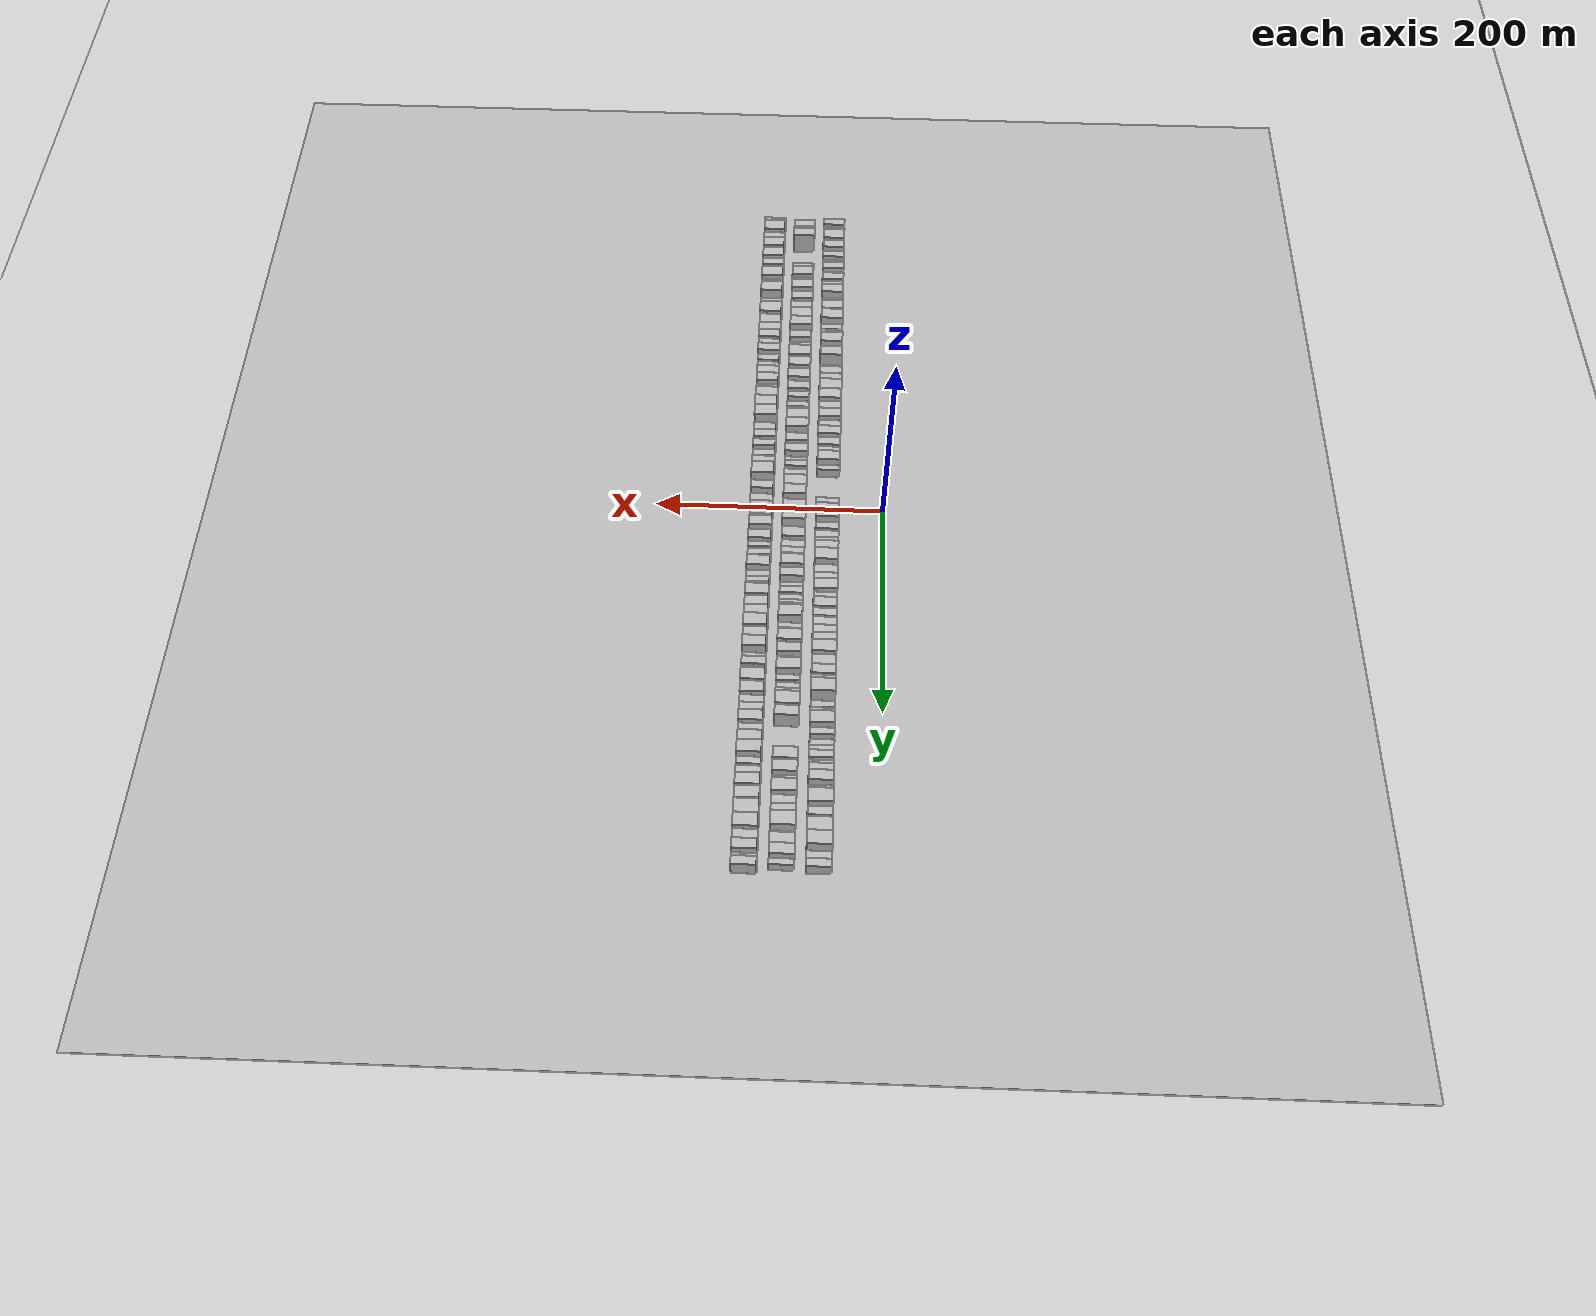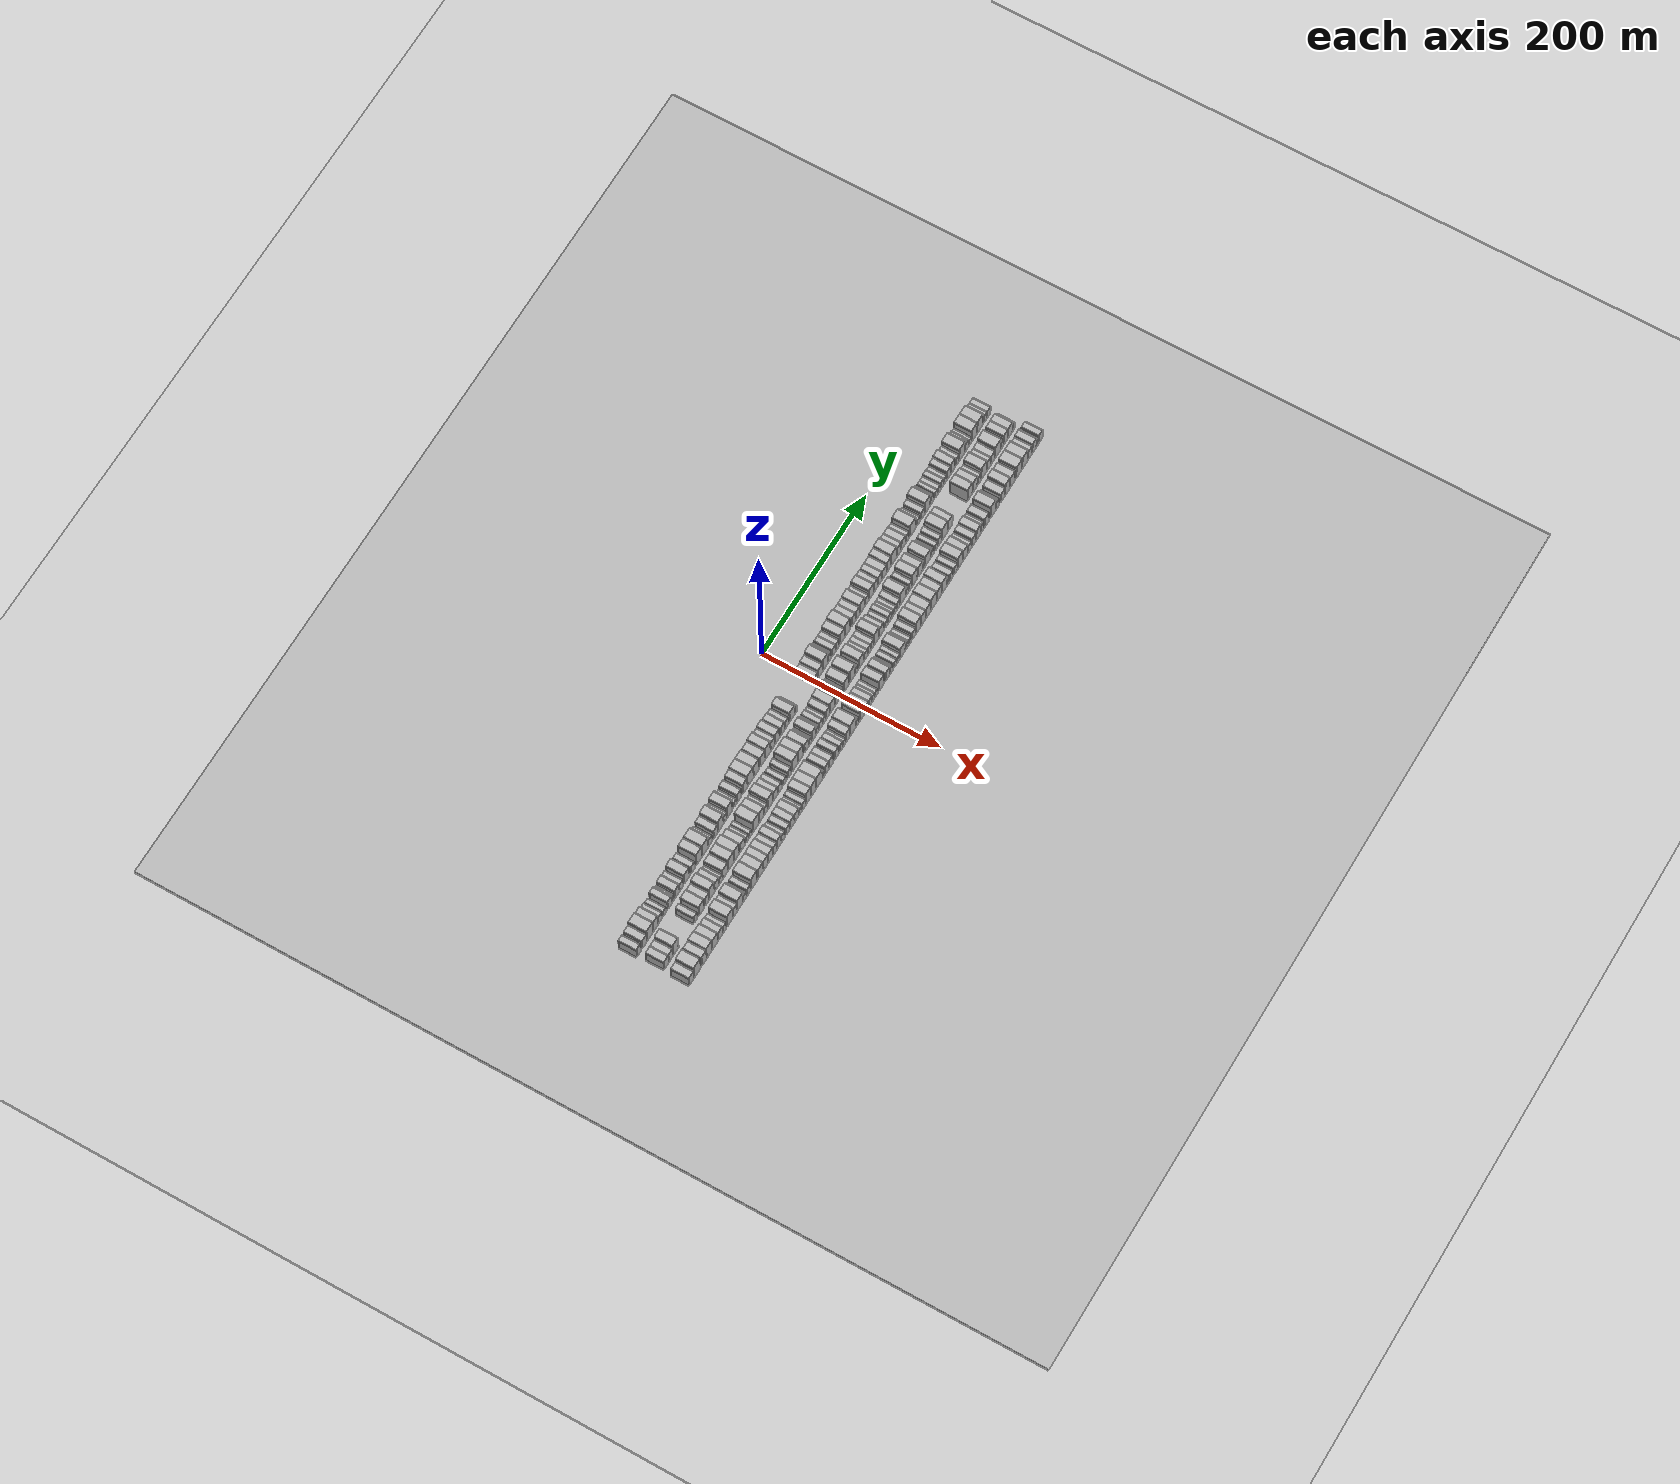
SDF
<?xml version="1.0" encoding="utf-8"?>

<sdf version="1.6">

   <world name="default">

      <gui fullscreen="0">

         <camera name="user_camera">

            <pose>-15 0 4.57585 0 0 0</pose>

            <view_controller>orbit</view_controller>

         </camera>

      </gui>

      <scene>

         <sky>

           <clouds>

             <speed>12</speed>

           </clouds>

         </sky>

         <ambient>0.4 0.4 0.4 1</ambient>

         <background>0.7 0.7 0.7 1</background>

         <shadows>1</shadows>

      </scene>

      <gravity>0 0 -9.8066</gravity>

      <magnetic_field>6e-06 2.3e-05 -4.2e-05</magnetic_field>

      <physics default="0" name="default_physics" type="ode">

         <ode>

            <solver>

               <type>quick</type>

               <iters>10</iters>

               <sor>1.0</sor>

               <use_dynamic_moi_rescaling>0</use_dynamic_moi_rescaling>

            </solver>

            <constraints>

               <cfm>0</cfm>

               <erp>0.2</erp>

               <contact_max_correcting_vel>100</contact_max_correcting_vel>

               <contact_surface_layer>0.001</contact_surface_layer>

            </constraints>

         </ode>

         <max_step_size>0.004</max_step_size>

         <real_time_factor>1</real_time_factor>

         <real_time_update_rate>250</real_time_update_rate>

      </physics>

      <light name="sun" type="directional">

         <cast_shadows>1</cast_shadows>

         <pose>0 0 10 0 0 0</pose>

         <diffuse>0.8 0.8 0.8 1</diffuse>

         <specular>0.2 0.2 0.2 1</specular>

         <attenuation>

            <range>1000</range>

            <constant>0.9</constant>

            <linear>0.01</linear>

            <quadratic>0.001</quadratic>

         </attenuation>

         <direction>-0.5 0.1 -0.9</direction>

      </light>

      <include>

         <name>ground_plane_1</name>

         <uri>model://HANNAS_ground_plane</uri>

         <pose>0 0 0  0 0 0</pose>

      </include>

      <include>

         <name>ground_plane_2</name>

         <uri>model://HANNAS_ground_plane</uri>

         <pose>100 0 0  0 0 0</pose>

      </include>

      <model name="building_1">

         <static>1</static>

         <pose frame="">50.0000 -332.3868 0 0.000000 0.000000 0.000000</pose>

         <link name="link">

            <pose frame="">0 0 9.00 0 0 0</pose>

            <collision name="collision">

               <geometry>

                  <box>

                     <size>20.0000 7.2263 18.0000</size>

                  </box>

               </geometry>

               <max_contacts>10</max_contacts>

               <surface>

                  <contact>

                     <ode/>

                  </contact>

                  <bounce/>

                  <friction>

                     <torsional>

                        <ode/>

                     </torsional>

                     <ode/>

                  </friction>

               </surface>

            </collision>

            <visual name="visual">

               <cast_shadows>0</cast_shadows>

               <geometry>

                  <box>

                     <size>20.0000 7.2263 18.0000</size>

                  </box>

               </geometry>

               <material>

                  <script>

                     <uri>model://HANNAS_wall/materials/scripts</uri>

                     <uri>model://HANNAS_wall/materials/textures</uri>

                     <name>vrc/HANNAS_wall</name>

                  </script>

               </material>

            </visual>

            <self_collide>0</self_collide>

            <enable_wind>0</enable_wind>

            <kinematic>0</kinematic>

         </link>

      </model>

      <model name="building_2">

         <static>1</static>

         <pose frame="">50.0000 -321.5118 0 0.000000 0.000000 0.000000</pose>

         <link name="link">

            <pose frame="">0 0 9.00 0 0 0</pose>

            <collision name="collision">

               <geometry>

                  <box>

                     <size>20.0000 8.5238 18.0000</size>

                  </box>

               </geometry>

               <max_contacts>10</max_contacts>

               <surface>

                  <contact>

                     <ode/>

                  </contact>

                  <bounce/>

                  <friction>

                     <torsional>

                        <ode/>

                     </torsional>

                     <ode/>

                  </friction>

               </surface>

            </collision>

            <visual name="visual">

               <cast_shadows>0</cast_shadows>

               <geometry>

                  <box>

                     <size>20.0000 8.5238 18.0000</size>

                  </box>

               </geometry>

               <material>

                  <script>

                     <uri>model://HANNAS_wall/materials/scripts</uri>

                     <uri>model://HANNAS_wall/materials/textures</uri>

                     <name>vrc/HANNAS_wall</name>

                  </script>

               </material>

            </visual>

            <self_collide>0</self_collide>

            <enable_wind>0</enable_wind>

            <kinematic>0</kinematic>

         </link>

      </model>

      <model name="building_3">

         <static>1</static>

         <pose frame="">50.0000 -311.4336 0 0.000000 0.000000 0.000000</pose>

         <link name="link">

            <pose frame="">0 0 12.00 0 0 0</pose>

            <collision name="collision">

               <geometry>

                  <box>

                     <size>20.0000 11.6325 24.0000</size>

                  </box>

               </geometry>

               <max_contacts>10</max_contacts>

               <surface>

                  <contact>

                     <ode/>

                  </contact>

                  <bounce/>

                  <friction>

                     <torsional>

                        <ode/>

                     </torsional>

                     <ode/>

                  </friction>

               </surface>

            </collision>

            <visual name="visual">

               <cast_shadows>0</cast_shadows>

               <geometry>

                  <box>

                     <size>20.0000 11.6325 24.0000</size>

                  </box>

               </geometry>

               <material>

                  <script>

                     <uri>model://HANNAS_wall/materials/scripts</uri>

                     <uri>model://HANNAS_wall/materials/textures</uri>

                     <name>vrc/HANNAS_wall</name>

                  </script>

               </material>

            </visual>

            <self_collide>0</self_collide>

            <enable_wind>0</enable_wind>

            <kinematic>0</kinematic>

         </link>

      </model>

      <model name="building_4">

         <static>1</static>

         <pose frame="">50.0000 -301.0388 0 0.000000 0.000000 0.000000</pose>

         <link name="link">

            <pose frame="">0 0 10.50 0 0 0</pose>

            <collision name="collision">

               <geometry>

                  <box>

                     <size>20.0000 9.1571 21.0000</size>

                  </box>

               </geometry>

               <max_contacts>10</max_contacts>

               <surface>

                  <contact>

                     <ode/>

                  </contact>

                  <bounce/>

                  <friction>

                     <torsional>

                        <ode/>

                     </torsional>

                     <ode/>

                  </friction>

               </surface>

            </collision>

            <visual name="visual">

               <cast_shadows>0</cast_shadows>

               <geometry>

                  <box>

                     <size>20.0000 9.1571 21.0000</size>

                  </box>

               </geometry>

               <material>

                  <script>

                     <uri>model://HANNAS_wall/materials/scripts</uri>

                     <uri>model://HANNAS_wall/materials/textures</uri>

                     <name>vrc/HANNAS_wall</name>

                  </script>

               </material>

            </visual>

            <self_collide>0</self_collide>

            <enable_wind>0</enable_wind>

            <kinematic>0</kinematic>

         </link>

      </model>

      <model name="building_5">

         <static>1</static>

         <pose frame="">50.0000 -292.8511 0 0.000000 0.000000 0.000000</pose>

         <link name="link">

            <pose frame="">0 0 7.50 0 0 0</pose>

            <collision name="collision">

               <geometry>

                  <box>

                     <size>20.0000 7.2183 15.0000</size>

                  </box>

               </geometry>

               <max_contacts>10</max_contacts>

               <surface>

                  <contact>

                     <ode/>

                  </contact>

                  <bounce/>

                  <friction>

                     <torsional>

                        <ode/>

                     </torsional>

                     <ode/>

                  </friction>

               </surface>

            </collision>

            <visual name="visual">

               <cast_shadows>0</cast_shadows>

               <geometry>

                  <box>

                     <size>20.0000 7.2183 15.0000</size>

                  </box>

               </geometry>

               <material>

                  <script>

                     <uri>model://HANNAS_wall/materials/scripts</uri>

                     <uri>model://HANNAS_wall/materials/textures</uri>

                     <name>vrc/HANNAS_wall</name>

                  </script>

               </material>

            </visual>

            <self_collide>0</self_collide>

            <enable_wind>0</enable_wind>

            <kinematic>0</kinematic>

         </link>

      </model>

      <model name="building_6">

         <static>1</static>

         <pose frame="">50.0000 -284.6033 0 0.000000 0.000000 0.000000</pose>

         <link name="link">

            <pose frame="">0 0 6.00 0 0 0</pose>

            <collision name="collision">

               <geometry>

                  <box>

                     <size>20.0000 5.2774 12.0000</size>

                  </box>

               </geometry>

               <max_contacts>10</max_contacts>

               <surface>

                  <contact>

                     <ode/>

                  </contact>

                  <bounce/>

                  <friction>

                     <torsional>

                        <ode/>

                     </torsional>

                     <ode/>

                  </friction>

               </surface>

            </collision>

            <visual name="visual">

               <cast_shadows>0</cast_shadows>

               <geometry>

                  <box>

                     <size>20.0000 5.2774 12.0000</size>

                  </box>

               </geometry>

               <material>

                  <script>

                     <uri>model://HANNAS_wall/materials/scripts</uri>

                     <uri>model://HANNAS_wall/materials/textures</uri>

                     <name>vrc/HANNAS_wall</name>

                  </script>

               </material>

            </visual>

            <self_collide>0</self_collide>

            <enable_wind>0</enable_wind>

            <kinematic>0</kinematic>

         </link>

      </model>

      <model name="building_7">

         <static>1</static>

         <pose frame="">50.0000 -275.2756 0 0.000000 0.000000 0.000000</pose>

         <link name="link">

            <pose frame="">0 0 9.00 0 0 0</pose>

            <collision name="collision">

               <geometry>

                  <box>

                     <size>20.0000 7.3779 18.0000</size>

                  </box>

               </geometry>

               <max_contacts>10</max_contacts>

               <surface>

                  <contact>

                     <ode/>

                  </contact>

                  <bounce/>

                  <friction>

                     <torsional>

                        <ode/>

                     </torsional>

                     <ode/>

                  </friction>

               </surface>

            </collision>

            <visual name="visual">

               <cast_shadows>0</cast_shadows>

               <geometry>

                  <box>

                     <size>20.0000 7.3779 18.0000</size>

                  </box>

               </geometry>

               <material>

                  <script>

                     <uri>model://HANNAS_wall/materials/scripts</uri>

                     <uri>model://HANNAS_wall/materials/textures</uri>

                     <name>vrc/HANNAS_wall</name>

                  </script>

               </material>

            </visual>

            <self_collide>0</self_collide>

            <enable_wind>0</enable_wind>

            <kinematic>0</kinematic>

         </link>

      </model>

      <model name="building_8">

         <static>1</static>

         <pose frame="">50.0000 -269.0671 0 0.000000 0.000000 0.000000</pose>

         <link name="link">

            <pose frame="">0 0 6.00 0 0 0</pose>

            <collision name="collision">

               <geometry>

                  <box>

                     <size>20.0000 5.0391 12.0000</size>

                  </box>

               </geometry>

               <max_contacts>10</max_contacts>

               <surface>

                  <contact>

                     <ode/>

                  </contact>

                  <bounce/>

                  <friction>

                     <torsional>

                        <ode/>

                     </torsional>

                     <ode/>

                  </friction>

               </surface>

            </collision>

            <visual name="visual">

               <cast_shadows>0</cast_shadows>

               <geometry>

                  <box>

                     <size>20.0000 5.0391 12.0000</size>

                  </box>

               </geometry>

               <material>

                  <script>

                     <uri>model://HANNAS_wall/materials/scripts</uri>

                     <uri>model://HANNAS_wall/materials/textures</uri>

                     <name>vrc/HANNAS_wall</name>

                  </script>

               </material>

            </visual>

            <self_collide>0</self_collide>

            <enable_wind>0</enable_wind>

            <kinematic>0</kinematic>

         </link>

      </model>

      <model name="building_9">

         <static>1</static>

         <pose frame="">50.0000 -261.3368 0 0.000000 0.000000 0.000000</pose>

         <link name="link">

            <pose frame="">0 0 9.00 0 0 0</pose>

            <collision name="collision">

               <geometry>

                  <box>

                     <size>20.0000 8.4215 18.0000</size>

                  </box>

               </geometry>

               <max_contacts>10</max_contacts>

               <surface>

                  <contact>

                     <ode/>

                  </contact>

                  <bounce/>

                  <friction>

                     <torsional>

                        <ode/>

                     </torsional>

                     <ode/>

                  </friction>

               </surface>

            </collision>

            <visual name="visual">

               <cast_shadows>0</cast_shadows>

               <geometry>

                  <box>

                     <size>20.0000 8.4215 18.0000</size>

                  </box>

               </geometry>

               <material>

                  <script>

                     <uri>model://HANNAS_wall/materials/scripts</uri>

                     <uri>model://HANNAS_wall/materials/textures</uri>

                     <name>vrc/HANNAS_wall</name>

                  </script>

               </material>

            </visual>

            <self_collide>0</self_collide>

            <enable_wind>0</enable_wind>

            <kinematic>0</kinematic>

         </link>

      </model>

      <model name="building_10">

         <static>1</static>

         <pose frame="">50.0000 -253.6555 0 0.000000 0.000000 0.000000</pose>

         <link name="link">

            <pose frame="">0 0 7.50 0 0 0</pose>

            <collision name="collision">

               <geometry>

                  <box>

                     <size>20.0000 6.9411 15.0000</size>

                  </box>

               </geometry>

               <max_contacts>10</max_contacts>

               <surface>

                  <contact>

                     <ode/>

                  </contact>

                  <bounce/>

                  <friction>

                     <torsional>

                        <ode/>

                     </torsional>

                     <ode/>

                  </friction>

               </surface>

            </collision>

            <visual name="visual">

               <cast_shadows>0</cast_shadows>

               <geometry>

                  <box>

                     <size>20.0000 6.9411 15.0000</size>

                  </box>

               </geometry>

               <material>

                  <script>

                     <uri>model://HANNAS_wall/materials/scripts</uri>

                     <uri>model://HANNAS_wall/materials/textures</uri>

                     <name>vrc/HANNAS_wall</name>

                  </script>

               </material>

            </visual>

            <self_collide>0</self_collide>

            <enable_wind>0</enable_wind>

            <kinematic>0</kinematic>

         </link>

      </model>

      <model name="building_11">

         <static>1</static>

         <pose frame="">50.0000 -243.3619 0 0.000000 0.000000 0.000000</pose>

         <link name="link">

            <pose frame="">0 0 10.50 0 0 0</pose>

            <collision name="collision">

               <geometry>

                  <box>

                     <size>20.0000 9.6462 21.0000</size>

                  </box>

               </geometry>

               <max_contacts>10</max_contacts>

               <surface>

                  <contact>

                     <ode/>

                  </contact>

                  <bounce/>

                  <friction>

                     <torsional>

                        <ode/>

                     </torsional>

                     <ode/>

                  </friction>

               </surface>

            </collision>

            <visual name="visual">

               <cast_shadows>0</cast_shadows>

               <geometry>

                  <box>

                     <size>20.0000 9.6462 21.0000</size>

                  </box>

               </geometry>

               <material>

                  <script>

                     <uri>model://HANNAS_wall/materials/scripts</uri>

                     <uri>model://HANNAS_wall/materials/textures</uri>

                     <name>vrc/HANNAS_wall</name>

                  </script>

               </material>

            </visual>

            <self_collide>0</self_collide>

            <enable_wind>0</enable_wind>

            <kinematic>0</kinematic>

         </link>

      </model>

      <model name="building_12">

         <static>1</static>

         <pose frame="">50.0000 -232.0014 0 0.000000 0.000000 0.000000</pose>

         <link name="link">

            <pose frame="">0 0 7.50 0 0 0</pose>

            <collision name="collision">

               <geometry>

                  <box>

                     <size>20.0000 7.0747 15.0000</size>

                  </box>

               </geometry>

               <max_contacts>10</max_contacts>

               <surface>

                  <contact>

                     <ode/>

                  </contact>

                  <bounce/>

                  <friction>

                     <torsional>

                        <ode/>

                     </torsional>

                     <ode/>

                  </friction>

               </surface>

            </collision>

            <visual name="visual">

               <cast_shadows>0</cast_shadows>

               <geometry>

                  <box>

                     <size>20.0000 7.0747 15.0000</size>

                  </box>

               </geometry>

               <material>

                  <script>

                     <uri>model://HANNAS_wall/materials/scripts</uri>

                     <uri>model://HANNAS_wall/materials/textures</uri>

                     <name>vrc/HANNAS_wall</name>

                  </script>

               </material>

            </visual>

            <self_collide>0</self_collide>

            <enable_wind>0</enable_wind>

            <kinematic>0</kinematic>

         </link>

      </model>

      <model name="building_13">

         <static>1</static>

         <pose frame="">50.0000 -220.4815 0 0.000000 0.000000 0.000000</pose>

         <link name="link">

            <pose frame="">0 0 12.00 0 0 0</pose>

            <collision name="collision">

               <geometry>

                  <box>

                     <size>20.0000 9.9652 24.0000</size>

                  </box>

               </geometry>

               <max_contacts>10</max_contacts>

               <surface>

                  <contact>

                     <ode/>

                  </contact>

                  <bounce/>

                  <friction>

                     <torsional>

                        <ode/>

                     </torsional>

                     <ode/>

                  </friction>

               </surface>

            </collision>

            <visual name="visual">

               <cast_shadows>0</cast_shadows>

               <geometry>

                  <box>

                     <size>20.0000 9.9652 24.0000</size>

                  </box>

               </geometry>

               <material>

                  <script>

                     <uri>model://HANNAS_wall/materials/scripts</uri>

                     <uri>model://HANNAS_wall/materials/textures</uri>

                     <name>vrc/HANNAS_wall</name>

                  </script>

               </material>

            </visual>

            <self_collide>0</self_collide>

            <enable_wind>0</enable_wind>

            <kinematic>0</kinematic>

         </link>

      </model>

      <model name="building_14">

         <static>1</static>

         <pose frame="">50.0000 -208.8800 0 0.000000 0.000000 0.000000</pose>

         <link name="link">

            <pose frame="">0 0 12.00 0 0 0</pose>

            <collision name="collision">

               <geometry>

                  <box>

                     <size>20.0000 11.2376 24.0000</size>

                  </box>

               </geometry>

               <max_contacts>10</max_contacts>

               <surface>

                  <contact>

                     <ode/>

                  </contact>

                  <bounce/>

                  <friction>

                     <torsional>

                        <ode/>

                     </torsional>

                     <ode/>

                  </friction>

               </surface>

            </collision>

            <visual name="visual">

               <cast_shadows>0</cast_shadows>

               <geometry>

                  <box>

                     <size>20.0000 11.2376 24.0000</size>

                  </box>

               </geometry>

               <material>

                  <script>

                     <uri>model://HANNAS_wall/materials/scripts</uri>

                     <uri>model://HANNAS_wall/materials/textures</uri>

                     <name>vrc/HANNAS_wall</name>

                  </script>

               </material>

            </visual>

            <self_collide>0</self_collide>

            <enable_wind>0</enable_wind>

            <kinematic>0</kinematic>

         </link>

      </model>

      <model name="building_15">

         <static>1</static>

         <pose frame="">50.0000 -199.9194 0 0.000000 0.000000 0.000000</pose>

         <link name="link">

            <pose frame="">0 0 7.50 0 0 0</pose>

            <collision name="collision">

               <geometry>

                  <box>

                     <size>20.0000 6.6837 15.0000</size>

                  </box>

               </geometry>

               <max_contacts>10</max_contacts>

               <surface>

                  <contact>

                     <ode/>

                  </contact>

                  <bounce/>

                  <friction>

                     <torsional>

                        <ode/>

                     </torsional>

                     <ode/>

                  </friction>

               </surface>

            </collision>

            <visual name="visual">

               <cast_shadows>0</cast_shadows>

               <geometry>

                  <box>

                     <size>20.0000 6.6837 15.0000</size>

                  </box>

               </geometry>

               <material>

                  <script>

                     <uri>model://HANNAS_wall/materials/scripts</uri>

                     <uri>model://HANNAS_wall/materials/textures</uri>

                     <name>vrc/HANNAS_wall</name>

                  </script>

               </material>

            </visual>

            <self_collide>0</self_collide>

            <enable_wind>0</enable_wind>

            <kinematic>0</kinematic>

         </link>

      </model>

      <model name="building_16">

         <static>1</static>

         <pose frame="">50.0000 -189.4994 0 0.000000 0.000000 0.000000</pose>

         <link name="link">

            <pose frame="">0 0 9.00 0 0 0</pose>

            <collision name="collision">

               <geometry>

                  <box>

                     <size>20.0000 8.1563 18.0000</size>

                  </box>

               </geometry>

               <max_contacts>10</max_contacts>

               <surface>

                  <contact>

                     <ode/>

                  </contact>

                  <bounce/>

                  <friction>

                     <torsional>

                        <ode/>

                     </torsional>

                     <ode/>

                  </friction>

               </surface>

            </collision>

            <visual name="visual">

               <cast_shadows>0</cast_shadows>

               <geometry>

                  <box>

                     <size>20.0000 8.1563 18.0000</size>

                  </box>

               </geometry>

               <material>

                  <script>

                     <uri>model://HANNAS_wall/materials/scripts</uri>

                     <uri>model://HANNAS_wall/materials/textures</uri>

                     <name>vrc/HANNAS_wall</name>

                  </script>

               </material>

            </visual>

            <self_collide>0</self_collide>

            <enable_wind>0</enable_wind>

            <kinematic>0</kinematic>

         </link>

      </model>

      <model name="building_17">

         <static>1</static>

         <pose frame="">50.0000 -180.2169 0 0.000000 0.000000 0.000000</pose>

         <link name="link">

            <pose frame="">0 0 12.00 0 0 0</pose>

            <collision name="collision">

               <geometry>

                  <box>

                     <size>20.0000 10.4087 24.0000</size>

                  </box>

               </geometry>

               <max_contacts>10</max_contacts>

               <surface>

                  <contact>

                     <ode/>

                  </contact>

                  <bounce/>

                  <friction>

                     <torsional>

                        <ode/>

                     </torsional>

                     <ode/>

                  </friction>

               </surface>

            </collision>

            <visual name="visual">

               <cast_shadows>0</cast_shadows>

               <geometry>

                  <box>

                     <size>20.0000 10.4087 24.0000</size>

                  </box>

               </geometry>

               <material>

                  <script>

                     <uri>model://HANNAS_wall/materials/scripts</uri>

                     <uri>model://HANNAS_wall/materials/textures</uri>

                     <name>vrc/HANNAS_wall</name>

                  </script>

               </material>

            </visual>

            <self_collide>0</self_collide>

            <enable_wind>0</enable_wind>

            <kinematic>0</kinematic>

         </link>

      </model>

      <model name="building_18">

         <static>1</static>

         <pose frame="">50.0000 -171.6984 0 0.000000 0.000000 0.000000</pose>

         <link name="link">

            <pose frame="">0 0 7.50 0 0 0</pose>

            <collision name="collision">

               <geometry>

                  <box>

                     <size>20.0000 6.6282 15.0000</size>

                  </box>

               </geometry>

               <max_contacts>10</max_contacts>

               <surface>

                  <contact>

                     <ode/>

                  </contact>

                  <bounce/>

                  <friction>

                     <torsional>

                        <ode/>

                     </torsional>

                     <ode/>

                  </friction>

               </surface>

            </collision>

            <visual name="visual">

               <cast_shadows>0</cast_shadows>

               <geometry>

                  <box>

                     <size>20.0000 6.6282 15.0000</size>

                  </box>

               </geometry>

               <material>

                  <script>

                     <uri>model://HANNAS_wall/materials/scripts</uri>

                     <uri>model://HANNAS_wall/materials/textures</uri>

                     <name>vrc/HANNAS_wall</name>

                  </script>

               </material>

            </visual>

            <self_collide>0</self_collide>

            <enable_wind>0</enable_wind>

            <kinematic>0</kinematic>

         </link>

      </model>

      <model name="building_19">

         <static>1</static>

         <pose frame="">50.0000 -163.4834 0 0.000000 0.000000 0.000000</pose>

         <link name="link">

            <pose frame="">0 0 12.00 0 0 0</pose>

            <collision name="collision">

               <geometry>

                  <box>

                     <size>20.0000 9.8018 24.0000</size>

                  </box>

               </geometry>

               <max_contacts>10</max_contacts>

               <surface>

                  <contact>

                     <ode/>

                  </contact>

                  <bounce/>

                  <friction>

                     <torsional>

                        <ode/>

                     </torsional>

                     <ode/>

                  </friction>

               </surface>

            </collision>

            <visual name="visual">

               <cast_shadows>0</cast_shadows>

               <geometry>

                  <box>

                     <size>20.0000 9.8018 24.0000</size>

                  </box>

               </geometry>

               <material>

                  <script>

                     <uri>model://HANNAS_wall/materials/scripts</uri>

                     <uri>model://HANNAS_wall/materials/textures</uri>

                     <name>vrc/HANNAS_wall</name>

                  </script>

               </material>

            </visual>

            <self_collide>0</self_collide>

            <enable_wind>0</enable_wind>

            <kinematic>0</kinematic>

         </link>

      </model>

      <model name="building_20">

         <static>1</static>

         <pose frame="">50.0000 -152.9555 0 0.000000 0.000000 0.000000</pose>

         <link name="link">

            <pose frame="">0 0 6.00 0 0 0</pose>

            <collision name="collision">

               <geometry>

                  <box>

                     <size>20.0000 5.2540 12.0000</size>

                  </box>

               </geometry>

               <max_contacts>10</max_contacts>

               <surface>

                  <contact>

                     <ode/>

                  </contact>

                  <bounce/>

                  <friction>

                     <torsional>

                        <ode/>

                     </torsional>

                     <ode/>

                  </friction>

               </surface>

            </collision>

            <visual name="visual">

               <cast_shadows>0</cast_shadows>

               <geometry>

                  <box>

                     <size>20.0000 5.2540 12.0000</size>

                  </box>

               </geometry>

               <material>

                  <script>

                     <uri>model://HANNAS_wall/materials/scripts</uri>

                     <uri>model://HANNAS_wall/materials/textures</uri>

                     <name>vrc/HANNAS_wall</name>

                  </script>

               </material>

            </visual>

            <self_collide>0</self_collide>

            <enable_wind>0</enable_wind>

            <kinematic>0</kinematic>

         </link>

      </model>

      <model name="building_21">

         <static>1</static>

         <pose frame="">50.0000 -145.4644 0 0.000000 0.000000 0.000000</pose>

         <link name="link">

            <pose frame="">0 0 9.00 0 0 0</pose>

            <collision name="collision">

               <geometry>

                  <box>

                     <size>20.0000 7.7281 18.0000</size>

                  </box>

               </geometry>

               <max_contacts>10</max_contacts>

               <surface>

                  <contact>

                     <ode/>

                  </contact>

                  <bounce/>

                  <friction>

                     <torsional>

                        <ode/>

                     </torsional>

                     <ode/>

                  </friction>

               </surface>

            </collision>

            <visual name="visual">

               <cast_shadows>0</cast_shadows>

               <geometry>

                  <box>

                     <size>20.0000 7.7281 18.0000</size>

                  </box>

               </geometry>

               <material>

                  <script>

                     <uri>model://HANNAS_wall/materials/scripts</uri>

                     <uri>model://HANNAS_wall/materials/textures</uri>

                     <name>vrc/HANNAS_wall</name>

                  </script>

               </material>

            </visual>

            <self_collide>0</self_collide>

            <enable_wind>0</enable_wind>

            <kinematic>0</kinematic>

         </link>

      </model>

      <model name="building_22">

         <static>1</static>

         <pose frame="">50.0000 -134.2863 0 0.000000 0.000000 0.000000</pose>

         <link name="link">

            <pose frame="">0 0 10.50 0 0 0</pose>

            <collision name="collision">

               <geometry>

                  <box>

                     <size>20.0000 8.6280 21.0000</size>

                  </box>

               </geometry>

               <max_contacts>10</max_contacts>

               <surface>

                  <contact>

                     <ode/>

                  </contact>

                  <bounce/>

                  <friction>

                     <torsional>

                        <ode/>

                     </torsional>

                     <ode/>

                  </friction>

               </surface>

            </collision>

            <visual name="visual">

               <cast_shadows>0</cast_shadows>

               <geometry>

                  <box>

                     <size>20.0000 8.6280 21.0000</size>

                  </box>

               </geometry>

               <material>

                  <script>

                     <uri>model://HANNAS_wall/materials/scripts</uri>

                     <uri>model://HANNAS_wall/materials/textures</uri>

                     <name>vrc/HANNAS_wall</name>

                  </script>

               </material>

            </visual>

            <self_collide>0</self_collide>

            <enable_wind>0</enable_wind>

            <kinematic>0</kinematic>

         </link>

      </model>

      <model name="building_23">

         <static>1</static>

         <pose frame="">50.0000 -124.2714 0 0.000000 0.000000 0.000000</pose>

         <link name="link">

            <pose frame="">0 0 12.00 0 0 0</pose>

            <collision name="collision">

               <geometry>

                  <box>

                     <size>20.0000 11.4019 24.0000</size>

                  </box>

               </geometry>

               <max_contacts>10</max_contacts>

               <surface>

                  <contact>

                     <ode/>

                  </contact>

                  <bounce/>

                  <friction>

                     <torsional>

                        <ode/>

                     </torsional>

                     <ode/>

                  </friction>

               </surface>

            </collision>

            <visual name="visual">

               <cast_shadows>0</cast_shadows>

               <geometry>

                  <box>

                     <size>20.0000 11.4019 24.0000</size>

                  </box>

               </geometry>

               <material>

                  <script>

                     <uri>model://HANNAS_wall/materials/scripts</uri>

                     <uri>model://HANNAS_wall/materials/textures</uri>

                     <name>vrc/HANNAS_wall</name>

                  </script>

               </material>

            </visual>

            <self_collide>0</self_collide>

            <enable_wind>0</enable_wind>

            <kinematic>0</kinematic>

         </link>

      </model>

      <model name="building_24">

         <static>1</static>

         <pose frame="">50.0000 -113.2940 0 0.000000 0.000000 0.000000</pose>

         <link name="link">

            <pose frame="">0 0 12.00 0 0 0</pose>

            <collision name="collision">

               <geometry>

                  <box>

                     <size>20.0000 10.5528 24.0000</size>

                  </box>

               </geometry>

               <max_contacts>10</max_contacts>

               <surface>

                  <contact>

                     <ode/>

                  </contact>

                  <bounce/>

                  <friction>

                     <torsional>

                        <ode/>

                     </torsional>

                     <ode/>

                  </friction>

               </surface>

            </collision>

            <visual name="visual">

               <cast_shadows>0</cast_shadows>

               <geometry>

                  <box>

                     <size>20.0000 10.5528 24.0000</size>

                  </box>

               </geometry>

               <material>

                  <script>

                     <uri>model://HANNAS_wall/materials/scripts</uri>

                     <uri>model://HANNAS_wall/materials/textures</uri>

                     <name>vrc/HANNAS_wall</name>

                  </script>

               </material>

            </visual>

            <self_collide>0</self_collide>

            <enable_wind>0</enable_wind>

            <kinematic>0</kinematic>

         </link>

      </model>

      <model name="building_25">

         <static>1</static>

         <pose frame="">50.0000 -101.0536 0 0.000000 0.000000 0.000000</pose>

         <link name="link">

            <pose frame="">0 0 10.50 0 0 0</pose>

            <collision name="collision">

               <geometry>

                  <box>

                     <size>20.0000 9.9282 21.0000</size>

                  </box>

               </geometry>

               <max_contacts>10</max_contacts>

               <surface>

                  <contact>

                     <ode/>

                  </contact>

                  <bounce/>

                  <friction>

                     <torsional>

                        <ode/>

                     </torsional>

                     <ode/>

                  </friction>

               </surface>

            </collision>

            <visual name="visual">

               <cast_shadows>0</cast_shadows>

               <geometry>

                  <box>

                     <size>20.0000 9.9282 21.0000</size>

                  </box>

               </geometry>

               <material>

                  <script>

                     <uri>model://HANNAS_wall/materials/scripts</uri>

                     <uri>model://HANNAS_wall/materials/textures</uri>

                     <name>vrc/HANNAS_wall</name>

                  </script>

               </material>

            </visual>

            <self_collide>0</self_collide>

            <enable_wind>0</enable_wind>

            <kinematic>0</kinematic>

         </link>

      </model>

      <model name="building_26">

         <static>1</static>

         <pose frame="">50.0000 -91.2819 0 0.000000 0.000000 0.000000</pose>

         <link name="link">

            <pose frame="">0 0 12.00 0 0 0</pose>

            <collision name="collision">

               <geometry>

                  <box>

                     <size>20.0000 9.6151 24.0000</size>

                  </box>

               </geometry>

               <max_contacts>10</max_contacts>

               <surface>

                  <contact>

                     <ode/>

                  </contact>

                  <bounce/>

                  <friction>

                     <torsional>

                        <ode/>

                     </torsional>

                     <ode/>

                  </friction>

               </surface>

            </collision>

            <visual name="visual">

               <cast_shadows>0</cast_shadows>

               <geometry>

                  <box>

                     <size>20.0000 9.6151 24.0000</size>

                  </box>

               </geometry>

               <material>

                  <script>

                     <uri>model://HANNAS_wall/materials/scripts</uri>

                     <uri>model://HANNAS_wall/materials/textures</uri>

                     <name>vrc/HANNAS_wall</name>

                  </script>

               </material>

            </visual>

            <self_collide>0</self_collide>

            <enable_wind>0</enable_wind>

            <kinematic>0</kinematic>

         </link>

      </model>

      <model name="building_27">

         <static>1</static>

         <pose frame="">50.0000 -82.3182 0 0.000000 0.000000 0.000000</pose>

         <link name="link">

            <pose frame="">0 0 9.00 0 0 0</pose>

            <collision name="collision">

               <geometry>

                  <box>

                     <size>20.0000 8.3124 18.0000</size>

                  </box>

               </geometry>

               <max_contacts>10</max_contacts>

               <surface>

                  <contact>

                     <ode/>

                  </contact>

                  <bounce/>

                  <friction>

                     <torsional>

                        <ode/>

                     </torsional>

                     <ode/>

                  </friction>

               </surface>

            </collision>

            <visual name="visual">

               <cast_shadows>0</cast_shadows>

               <geometry>

                  <box>

                     <size>20.0000 8.3124 18.0000</size>

                  </box>

               </geometry>

               <material>

                  <script>

                     <uri>model://HANNAS_wall/materials/scripts</uri>

                     <uri>model://HANNAS_wall/materials/textures</uri>

                     <name>vrc/HANNAS_wall</name>

                  </script>

               </material>

            </visual>

            <self_collide>0</self_collide>

            <enable_wind>0</enable_wind>

            <kinematic>0</kinematic>

         </link>

      </model>

      <model name="building_28">

         <static>1</static>

         <pose frame="">50.0000 -73.7900 0 0.000000 0.000000 0.000000</pose>

         <link name="link">

            <pose frame="">0 0 10.50 0 0 0</pose>

            <collision name="collision">

               <geometry>

                  <box>

                     <size>20.0000 8.7438 21.0000</size>

                  </box>

               </geometry>

               <max_contacts>10</max_contacts>

               <surface>

                  <contact>

                     <ode/>

                  </contact>

                  <bounce/>

                  <friction>

                     <torsional>

                        <ode/>

                     </torsional>

                     <ode/>

                  </friction>

               </surface>

            </collision>

            <visual name="visual">

               <cast_shadows>0</cast_shadows>

               <geometry>

                  <box>

                     <size>20.0000 8.7438 21.0000</size>

                  </box>

               </geometry>

               <material>

                  <script>

                     <uri>model://HANNAS_wall/materials/scripts</uri>

                     <uri>model://HANNAS_wall/materials/textures</uri>

                     <name>vrc/HANNAS_wall</name>

                  </script>

               </material>

            </visual>

            <self_collide>0</self_collide>

            <enable_wind>0</enable_wind>

            <kinematic>0</kinematic>

         </link>

      </model>

      <model name="building_29">

         <static>1</static>

         <pose frame="">50.0000 -63.3321 0 0.000000 0.000000 0.000000</pose>

         <link name="link">

            <pose frame="">0 0 9.00 0 0 0</pose>

            <collision name="collision">

               <geometry>

                  <box>

                     <size>20.0000 8.1721 18.0000</size>

                  </box>

               </geometry>

               <max_contacts>10</max_contacts>

               <surface>

                  <contact>

                     <ode/>

                  </contact>

                  <bounce/>

                  <friction>

                     <torsional>

                        <ode/>

                     </torsional>

                     <ode/>

                  </friction>

               </surface>

            </collision>

            <visual name="visual">

               <cast_shadows>0</cast_shadows>

               <geometry>

                  <box>

                     <size>20.0000 8.1721 18.0000</size>

                  </box>

               </geometry>

               <material>

                  <script>

                     <uri>model://HANNAS_wall/materials/scripts</uri>

                     <uri>model://HANNAS_wall/materials/textures</uri>

                     <name>vrc/HANNAS_wall</name>

                  </script>

               </material>

            </visual>

            <self_collide>0</self_collide>

            <enable_wind>0</enable_wind>

            <kinematic>0</kinematic>

         </link>

      </model>

      <model name="building_30">

         <static>1</static>

         <pose frame="">50.0000 -55.7909 0 0.000000 0.000000 0.000000</pose>

         <link name="link">

            <pose frame="">0 0 7.50 0 0 0</pose>

            <collision name="collision">

               <geometry>

                  <box>

                     <size>20.0000 6.9103 15.0000</size>

                  </box>

               </geometry>

               <max_contacts>10</max_contacts>

               <surface>

                  <contact>

                     <ode/>

                  </contact>

                  <bounce/>

                  <friction>

                     <torsional>

                        <ode/>

                     </torsional>

                     <ode/>

                  </friction>

               </surface>

            </collision>

            <visual name="visual">

               <cast_shadows>0</cast_shadows>

               <geometry>

                  <box>

                     <size>20.0000 6.9103 15.0000</size>

                  </box>

               </geometry>

               <material>

                  <script>

                     <uri>model://HANNAS_wall/materials/scripts</uri>

                     <uri>model://HANNAS_wall/materials/textures</uri>

                     <name>vrc/HANNAS_wall</name>

                  </script>

               </material>

            </visual>

            <self_collide>0</self_collide>

            <enable_wind>0</enable_wind>

            <kinematic>0</kinematic>

         </link>

      </model>

      <model name="building_31">

         <static>1</static>

         <pose frame="">50.0000 -45.4435 0 0.000000 0.000000 0.000000</pose>

         <link name="link">

            <pose frame="">0 0 10.50 0 0 0</pose>

            <collision name="collision">

               <geometry>

                  <box>

                     <size>20.0000 9.7845 21.0000</size>

                  </box>

               </geometry>

               <max_contacts>10</max_contacts>

               <surface>

                  <contact>

                     <ode/>

                  </contact>

                  <bounce/>

                  <friction>

                     <torsional>

                        <ode/>

                     </torsional>

                     <ode/>

                  </friction>

               </surface>

            </collision>

            <visual name="visual">

               <cast_shadows>0</cast_shadows>

               <geometry>

                  <box>

                     <size>20.0000 9.7845 21.0000</size>

                  </box>

               </geometry>

               <material>

                  <script>

                     <uri>model://HANNAS_wall/materials/scripts</uri>

                     <uri>model://HANNAS_wall/materials/textures</uri>

                     <name>vrc/HANNAS_wall</name>

                  </script>

               </material>

            </visual>

            <self_collide>0</self_collide>

            <enable_wind>0</enable_wind>

            <kinematic>0</kinematic>

         </link>

      </model>

      <model name="building_32">

         <static>1</static>

         <pose frame="">50.0000 -38.0709 0 0.000000 0.000000 0.000000</pose>

         <link name="link">

            <pose frame="">0 0 6.00 0 0 0</pose>

            <collision name="collision">

               <geometry>

                  <box>

                     <size>20.0000 4.9606 12.0000</size>

                  </box>

               </geometry>

               <max_contacts>10</max_contacts>

               <surface>

                  <contact>

                     <ode/>

                  </contact>

                  <bounce/>

                  <friction>

                     <torsional>

                        <ode/>

                     </torsional>

                     <ode/>

                  </friction>

               </surface>

            </collision>

            <visual name="visual">

               <cast_shadows>0</cast_shadows>

               <geometry>

                  <box>

                     <size>20.0000 4.9606 12.0000</size>

                  </box>

               </geometry>

               <material>

                  <script>

                     <uri>model://HANNAS_wall/materials/scripts</uri>

                     <uri>model://HANNAS_wall/materials/textures</uri>

                     <name>vrc/HANNAS_wall</name>

                  </script>

               </material>

            </visual>

            <self_collide>0</self_collide>

            <enable_wind>0</enable_wind>

            <kinematic>0</kinematic>

         </link>

      </model>

      <model name="building_33">

         <static>1</static>

         <pose frame="">50.0000 0.4339 0 0.000000 0.000000 0.000000</pose>

         <link name="link">

            <pose frame="">0 0 7.50 0 0 0</pose>

            <collision name="collision">

               <geometry>

                  <box>

                     <size>20.0000 7.3497 15.0000</size>

                  </box>

               </geometry>

               <max_contacts>10</max_contacts>

               <surface>

                  <contact>

                     <ode/>

                  </contact>

                  <bounce/>

                  <friction>

                     <torsional>

                        <ode/>

                     </torsional>

                     <ode/>

                  </friction>

               </surface>

            </collision>

            <visual name="visual">

               <cast_shadows>0</cast_shadows>

               <geometry>

                  <box>

                     <size>20.0000 7.3497 15.0000</size>

                  </box>

               </geometry>

               <material>

                  <script>

                     <uri>model://HANNAS_wall/materials/scripts</uri>

                     <uri>model://HANNAS_wall/materials/textures</uri>

                     <name>vrc/HANNAS_wall</name>

                  </script>

               </material>

            </visual>

            <self_collide>0</self_collide>

            <enable_wind>0</enable_wind>

            <kinematic>0</kinematic>

         </link>

      </model>

      <model name="building_34">

         <static>1</static>

         <pose frame="">50.0000 8.4122 0 0.000000 0.000000 0.000000</pose>

         <link name="link">

            <pose frame="">0 0 9.00 0 0 0</pose>

            <collision name="collision">

               <geometry>

                  <box>

                     <size>20.0000 8.6069 18.0000</size>

                  </box>

               </geometry>

               <max_contacts>10</max_contacts>

               <surface>

                  <contact>

                     <ode/>

                  </contact>

                  <bounce/>

                  <friction>

                     <torsional>

                        <ode/>

                     </torsional>

                     <ode/>

                  </friction>

               </surface>

            </collision>

            <visual name="visual">

               <cast_shadows>0</cast_shadows>

               <geometry>

                  <box>

                     <size>20.0000 8.6069 18.0000</size>

                  </box>

               </geometry>

               <material>

                  <script>

                     <uri>model://HANNAS_wall/materials/scripts</uri>

                     <uri>model://HANNAS_wall/materials/textures</uri>

                     <name>vrc/HANNAS_wall</name>

                  </script>

               </material>

            </visual>

            <self_collide>0</self_collide>

            <enable_wind>0</enable_wind>

            <kinematic>0</kinematic>

         </link>

      </model>

      <model name="building_35">

         <static>1</static>

         <pose frame="">50.0000 17.7551 0 0.000000 0.000000 0.000000</pose>

         <link name="link">

            <pose frame="">0 0 12.00 0 0 0</pose>

            <collision name="collision">

               <geometry>

                  <box>

                     <size>20.0000 10.0788 24.0000</size>

                  </box>

               </geometry>

               <max_contacts>10</max_contacts>

               <surface>

                  <contact>

                     <ode/>

                  </contact>

                  <bounce/>

                  <friction>

                     <torsional>

                        <ode/>

                     </torsional>

                     <ode/>

                  </friction>

               </surface>

            </collision>

            <visual name="visual">

               <cast_shadows>0</cast_shadows>

               <geometry>

                  <box>

                     <size>20.0000 10.0788 24.0000</size>

                  </box>

               </geometry>

               <material>

                  <script>

                     <uri>model://HANNAS_wall/materials/scripts</uri>

                     <uri>model://HANNAS_wall/materials/textures</uri>

                     <name>vrc/HANNAS_wall</name>

                  </script>

               </material>

            </visual>

            <self_collide>0</self_collide>

            <enable_wind>0</enable_wind>

            <kinematic>0</kinematic>

         </link>

      </model>

      <model name="building_36">

         <static>1</static>

         <pose frame="">50.0000 26.1140 0 0.000000 0.000000 0.000000</pose>

         <link name="link">

            <pose frame="">0 0 7.50 0 0 0</pose>

            <collision name="collision">

               <geometry>

                  <box>

                     <size>20.0000 6.6390 15.0000</size>

                  </box>

               </geometry>

               <max_contacts>10</max_contacts>

               <surface>

                  <contact>

                     <ode/>

                  </contact>

                  <bounce/>

                  <friction>

                     <torsional>

                        <ode/>

                     </torsional>

                     <ode/>

                  </friction>

               </surface>

            </collision>

            <visual name="visual">

               <cast_shadows>0</cast_shadows>

               <geometry>

                  <box>

                     <size>20.0000 6.6390 15.0000</size>

                  </box>

               </geometry>

               <material>

                  <script>

                     <uri>model://HANNAS_wall/materials/scripts</uri>

                     <uri>model://HANNAS_wall/materials/textures</uri>

                     <name>vrc/HANNAS_wall</name>

                  </script>

               </material>

            </visual>

            <self_collide>0</self_collide>

            <enable_wind>0</enable_wind>

            <kinematic>0</kinematic>

         </link>

      </model>

      <model name="building_37">

         <static>1</static>

         <pose frame="">50.0000 34.9077 0 0.000000 0.000000 0.000000</pose>

         <link name="link">

            <pose frame="">0 0 7.50 0 0 0</pose>

            <collision name="collision">

               <geometry>

                  <box>

                     <size>20.0000 6.9484 15.0000</size>

                  </box>

               </geometry>

               <max_contacts>10</max_contacts>

               <surface>

                  <contact>

                     <ode/>

                  </contact>

                  <bounce/>

                  <friction>

                     <torsional>

                        <ode/>

                     </torsional>

                     <ode/>

                  </friction>

               </surface>

            </collision>

            <visual name="visual">

               <cast_shadows>0</cast_shadows>

               <geometry>

                  <box>

                     <size>20.0000 6.9484 15.0000</size>

                  </box>

               </geometry>

               <material>

                  <script>

                     <uri>model://HANNAS_wall/materials/scripts</uri>

                     <uri>model://HANNAS_wall/materials/textures</uri>

                     <name>vrc/HANNAS_wall</name>

                  </script>

               </material>

            </visual>

            <self_collide>0</self_collide>

            <enable_wind>0</enable_wind>

            <kinematic>0</kinematic>

         </link>

      </model>

      <model name="building_38">

         <static>1</static>

         <pose frame="">50.0000 41.5655 0 0.000000 0.000000 0.000000</pose>

         <link name="link">

            <pose frame="">0 0 7.50 0 0 0</pose>

            <collision name="collision">

               <geometry>

                  <box>

                     <size>20.0000 6.3673 15.0000</size>

                  </box>

               </geometry>

               <max_contacts>10</max_contacts>

               <surface>

                  <contact>

                     <ode/>

                  </contact>

                  <bounce/>

                  <friction>

                     <torsional>

                        <ode/>

                     </torsional>

                     <ode/>

                  </friction>

               </surface>

            </collision>

            <visual name="visual">

               <cast_shadows>0</cast_shadows>

               <geometry>

                  <box>

                     <size>20.0000 6.3673 15.0000</size>

                  </box>

               </geometry>

               <material>

                  <script>

                     <uri>model://HANNAS_wall/materials/scripts</uri>

                     <uri>model://HANNAS_wall/materials/textures</uri>

                     <name>vrc/HANNAS_wall</name>

                  </script>

               </material>

            </visual>

            <self_collide>0</self_collide>

            <enable_wind>0</enable_wind>

            <kinematic>0</kinematic>

         </link>

      </model>

      <model name="building_39">

         <static>1</static>

         <pose frame="">50.0000 50.4224 0 0.000000 0.000000 0.000000</pose>

         <link name="link">

            <pose frame="">0 0 10.50 0 0 0</pose>

            <collision name="collision">

               <geometry>

                  <box>

                     <size>20.0000 9.3465 21.0000</size>

                  </box>

               </geometry>

               <max_contacts>10</max_contacts>

               <surface>

                  <contact>

                     <ode/>

                  </contact>

                  <bounce/>

                  <friction>

                     <torsional>

                        <ode/>

                     </torsional>

                     <ode/>

                  </friction>

               </surface>

            </collision>

            <visual name="visual">

               <cast_shadows>0</cast_shadows>

               <geometry>

                  <box>

                     <size>20.0000 9.3465 21.0000</size>

                  </box>

               </geometry>

               <material>

                  <script>

                     <uri>model://HANNAS_wall/materials/scripts</uri>

                     <uri>model://HANNAS_wall/materials/textures</uri>

                     <name>vrc/HANNAS_wall</name>

                  </script>

               </material>

            </visual>

            <self_collide>0</self_collide>

            <enable_wind>0</enable_wind>

            <kinematic>0</kinematic>

         </link>

      </model>

      <model name="building_40">

         <static>1</static>

         <pose frame="">50.0000 60.7193 0 0.000000 0.000000 0.000000</pose>

         <link name="link">

            <pose frame="">0 0 12.00 0 0 0</pose>

            <collision name="collision">

               <geometry>

                  <box>

                     <size>20.0000 11.2474 24.0000</size>

                  </box>

               </geometry>

               <max_contacts>10</max_contacts>

               <surface>

                  <contact>

                     <ode/>

                  </contact>

                  <bounce/>

                  <friction>

                     <torsional>

                        <ode/>

                     </torsional>

                     <ode/>

                  </friction>

               </surface>

            </collision>

            <visual name="visual">

               <cast_shadows>0</cast_shadows>

               <geometry>

                  <box>

                     <size>20.0000 11.2474 24.0000</size>

                  </box>

               </geometry>

               <material>

                  <script>

                     <uri>model://HANNAS_wall/materials/scripts</uri>

                     <uri>model://HANNAS_wall/materials/textures</uri>

                     <name>vrc/HANNAS_wall</name>

                  </script>

               </material>

            </visual>

            <self_collide>0</self_collide>

            <enable_wind>0</enable_wind>

            <kinematic>0</kinematic>

         </link>

      </model>

      <model name="building_41">

         <static>1</static>

         <pose frame="">50.0000 72.3830 0 0.000000 0.000000 0.000000</pose>

         <link name="link">

            <pose frame="">0 0 9.00 0 0 0</pose>

            <collision name="collision">

               <geometry>

                  <box>

                     <size>20.0000 8.0800 18.0000</size>

                  </box>

               </geometry>

               <max_contacts>10</max_contacts>

               <surface>

                  <contact>

                     <ode/>

                  </contact>

                  <bounce/>

                  <friction>

                     <torsional>

                        <ode/>

                     </torsional>

                     <ode/>

                  </friction>

               </surface>

            </collision>

            <visual name="visual">

               <cast_shadows>0</cast_shadows>

               <geometry>

                  <box>

                     <size>20.0000 8.0800 18.0000</size>

                  </box>

               </geometry>

               <material>

                  <script>

                     <uri>model://HANNAS_wall/materials/scripts</uri>

                     <uri>model://HANNAS_wall/materials/textures</uri>

                     <name>vrc/HANNAS_wall</name>

                  </script>

               </material>

            </visual>

            <self_collide>0</self_collide>

            <enable_wind>0</enable_wind>

            <kinematic>0</kinematic>

         </link>

      </model>

      <model name="building_42">

         <static>1</static>

         <pose frame="">50.0000 80.2050 0 0.000000 0.000000 0.000000</pose>

         <link name="link">

            <pose frame="">0 0 9.00 0 0 0</pose>

            <collision name="collision">

               <geometry>

                  <box>

                     <size>20.0000 7.5639 18.0000</size>

                  </box>

               </geometry>

               <max_contacts>10</max_contacts>

               <surface>

                  <contact>

                     <ode/>

                  </contact>

                  <bounce/>

                  <friction>

                     <torsional>

                        <ode/>

                     </torsional>

                     <ode/>

                  </friction>

               </surface>

            </collision>

            <visual name="visual">

               <cast_shadows>0</cast_shadows>

               <geometry>

                  <box>

                     <size>20.0000 7.5639 18.0000</size>

                  </box>

               </geometry>

               <material>

                  <script>

                     <uri>model://HANNAS_wall/materials/scripts</uri>

                     <uri>model://HANNAS_wall/materials/textures</uri>

                     <name>vrc/HANNAS_wall</name>

                  </script>

               </material>

            </visual>

            <self_collide>0</self_collide>

            <enable_wind>0</enable_wind>

            <kinematic>0</kinematic>

         </link>

      </model>

      <model name="building_43">

         <static>1</static>

         <pose frame="">50.0000 89.0378 0 0.000000 0.000000 0.000000</pose>

         <link name="link">

            <pose frame="">0 0 10.50 0 0 0</pose>

            <collision name="collision">

               <geometry>

                  <box>

                     <size>20.0000 10.1018 21.0000</size>

                  </box>

               </geometry>

               <max_contacts>10</max_contacts>

               <surface>

                  <contact>

                     <ode/>

                  </contact>

                  <bounce/>

                  <friction>

                     <torsional>

                        <ode/>

                     </torsional>

                     <ode/>

                  </friction>

               </surface>

            </collision>

            <visual name="visual">

               <cast_shadows>0</cast_shadows>

               <geometry>

                  <box>

                     <size>20.0000 10.1018 21.0000</size>

                  </box>

               </geometry>

               <material>

                  <script>

                     <uri>model://HANNAS_wall/materials/scripts</uri>

                     <uri>model://HANNAS_wall/materials/textures</uri>

                     <name>vrc/HANNAS_wall</name>

                  </script>

               </material>

            </visual>

            <self_collide>0</self_collide>

            <enable_wind>0</enable_wind>

            <kinematic>0</kinematic>

         </link>

      </model>

      <model name="building_44">

         <static>1</static>

         <pose frame="">50.0000 97.7844 0 0.000000 0.000000 0.000000</pose>

         <link name="link">

            <pose frame="">0 0 7.50 0 0 0</pose>

            <collision name="collision">

               <geometry>

                  <box>

                     <size>20.0000 7.3913 15.0000</size>

                  </box>

               </geometry>

               <max_contacts>10</max_contacts>

               <surface>

                  <contact>

                     <ode/>

                  </contact>

                  <bounce/>

                  <friction>

                     <torsional>

                        <ode/>

                     </torsional>

                     <ode/>

                  </friction>

               </surface>

            </collision>

            <visual name="visual">

               <cast_shadows>0</cast_shadows>

               <geometry>

                  <box>

                     <size>20.0000 7.3913 15.0000</size>

                  </box>

               </geometry>

               <material>

                  <script>

                     <uri>model://HANNAS_wall/materials/scripts</uri>

                     <uri>model://HANNAS_wall/materials/textures</uri>

                     <name>vrc/HANNAS_wall</name>

                  </script>

               </material>

            </visual>

            <self_collide>0</self_collide>

            <enable_wind>0</enable_wind>

            <kinematic>0</kinematic>

         </link>

      </model>

      <model name="building_45">

         <static>1</static>

         <pose frame="">50.0000 107.0497 0 0.000000 0.000000 0.000000</pose>

         <link name="link">

            <pose frame="">0 0 10.50 0 0 0</pose>

            <collision name="collision">

               <geometry>

                  <box>

                     <size>20.0000 9.1391 21.0000</size>

                  </box>

               </geometry>

               <max_contacts>10</max_contacts>

               <surface>

                  <contact>

                     <ode/>

                  </contact>

                  <bounce/>

                  <friction>

                     <torsional>

                        <ode/>

                     </torsional>

                     <ode/>

                  </friction>

               </surface>

            </collision>

            <visual name="visual">

               <cast_shadows>0</cast_shadows>

               <geometry>

                  <box>

                     <size>20.0000 9.1391 21.0000</size>

                  </box>

               </geometry>

               <material>

                  <script>

                     <uri>model://HANNAS_wall/materials/scripts</uri>

                     <uri>model://HANNAS_wall/materials/textures</uri>

                     <name>vrc/HANNAS_wall</name>

                  </script>

               </material>

            </visual>

            <self_collide>0</self_collide>

            <enable_wind>0</enable_wind>

            <kinematic>0</kinematic>

         </link>

      </model>

      <model name="building_46">

         <static>1</static>

         <pose frame="">50.0000 115.4404 0 0.000000 0.000000 0.000000</pose>

         <link name="link">

            <pose frame="">0 0 9.00 0 0 0</pose>

            <collision name="collision">

               <geometry>

                  <box>

                     <size>20.0000 7.6424 18.0000</size>

                  </box>

               </geometry>

               <max_contacts>10</max_contacts>

               <surface>

                  <contact>

                     <ode/>

                  </contact>

                  <bounce/>

                  <friction>

                     <torsional>

                        <ode/>

                     </torsional>

                     <ode/>

                  </friction>

               </surface>

            </collision>

            <visual name="visual">

               <cast_shadows>0</cast_shadows>

               <geometry>

                  <box>

                     <size>20.0000 7.6424 18.0000</size>

                  </box>

               </geometry>

               <material>

                  <script>

                     <uri>model://HANNAS_wall/materials/scripts</uri>

                     <uri>model://HANNAS_wall/materials/textures</uri>

                     <name>vrc/HANNAS_wall</name>

                  </script>

               </material>

            </visual>

            <self_collide>0</self_collide>

            <enable_wind>0</enable_wind>

            <kinematic>0</kinematic>

         </link>

      </model>

      <model name="building_47">

         <static>1</static>

         <pose frame="">50.0000 124.1388 0 0.000000 0.000000 0.000000</pose>

         <link name="link">

            <pose frame="">0 0 9.00 0 0 0</pose>

            <collision name="collision">

               <geometry>

                  <box>

                     <size>20.0000 7.7543 18.0000</size>

                  </box>

               </geometry>

               <max_contacts>10</max_contacts>

               <surface>

                  <contact>

                     <ode/>

                  </contact>

                  <bounce/>

                  <friction>

                     <torsional>

                        <ode/>

                     </torsional>

                     <ode/>

                  </friction>

               </surface>

            </collision>

            <visual name="visual">

               <cast_shadows>0</cast_shadows>

               <geometry>

                  <box>

                     <size>20.0000 7.7543 18.0000</size>

                  </box>

               </geometry>

               <material>

                  <script>

                     <uri>model://HANNAS_wall/materials/scripts</uri>

                     <uri>model://HANNAS_wall/materials/textures</uri>

                     <name>vrc/HANNAS_wall</name>

                  </script>

               </material>

            </visual>

            <self_collide>0</self_collide>

            <enable_wind>0</enable_wind>

            <kinematic>0</kinematic>

         </link>

      </model>

      <model name="building_48">

         <static>1</static>

         <pose frame="">50.0000 132.5141 0 0.000000 0.000000 0.000000</pose>

         <link name="link">

            <pose frame="">0 0 9.00 0 0 0</pose>

            <collision name="collision">

               <geometry>

                  <box>

                     <size>20.0000 8.9964 18.0000</size>

                  </box>

               </geometry>

               <max_contacts>10</max_contacts>

               <surface>

                  <contact>

                     <ode/>

                  </contact>

                  <bounce/>

                  <friction>

                     <torsional>

                        <ode/>

                     </torsional>

                     <ode/>

                  </friction>

               </surface>

            </collision>

            <visual name="visual">

               <cast_shadows>0</cast_shadows>

               <geometry>

                  <box>

                     <size>20.0000 8.9964 18.0000</size>

                  </box>

               </geometry>

               <material>

                  <script>

                     <uri>model://HANNAS_wall/materials/scripts</uri>

                     <uri>model://HANNAS_wall/materials/textures</uri>

                     <name>vrc/HANNAS_wall</name>

                  </script>

               </material>

            </visual>

            <self_collide>0</self_collide>

            <enable_wind>0</enable_wind>

            <kinematic>0</kinematic>

         </link>

      </model>

      <model name="building_49">

         <static>1</static>

         <pose frame="">50.0000 141.3249 0 0.000000 0.000000 0.000000</pose>

         <link name="link">

            <pose frame="">0 0 10.50 0 0 0</pose>

            <collision name="collision">

               <geometry>

                  <box>

                     <size>20.0000 8.6251 21.0000</size>

                  </box>

               </geometry>

               <max_contacts>10</max_contacts>

               <surface>

                  <contact>

                     <ode/>

                  </contact>

                  <bounce/>

                  <friction>

                     <torsional>

                        <ode/>

                     </torsional>

                     <ode/>

                  </friction>

               </surface>

            </collision>

            <visual name="visual">

               <cast_shadows>0</cast_shadows>

               <geometry>

                  <box>

                     <size>20.0000 8.6251 21.0000</size>

                  </box>

               </geometry>

               <material>

                  <script>

                     <uri>model://HANNAS_wall/materials/scripts</uri>

                     <uri>model://HANNAS_wall/materials/textures</uri>

                     <name>vrc/HANNAS_wall</name>

                  </script>

               </material>

            </visual>

            <self_collide>0</self_collide>

            <enable_wind>0</enable_wind>

            <kinematic>0</kinematic>

         </link>

      </model>

      <model name="building_50">

         <static>1</static>

         <pose frame="">50.0000 151.0222 0 0.000000 0.000000 0.000000</pose>

         <link name="link">

            <pose frame="">0 0 12.00 0 0 0</pose>

            <collision name="collision">

               <geometry>

                  <box>

                     <size>20.0000 10.7695 24.0000</size>

                  </box>

               </geometry>

               <max_contacts>10</max_contacts>

               <surface>

                  <contact>

                     <ode/>

                  </contact>

                  <bounce/>

                  <friction>

                     <torsional>

                        <ode/>

                     </torsional>

                     <ode/>

                  </friction>

               </surface>

            </collision>

            <visual name="visual">

               <cast_shadows>0</cast_shadows>

               <geometry>

                  <box>

                     <size>20.0000 10.7695 24.0000</size>

                  </box>

               </geometry>

               <material>

                  <script>

                     <uri>model://HANNAS_wall/materials/scripts</uri>

                     <uri>model://HANNAS_wall/materials/textures</uri>

                     <name>vrc/HANNAS_wall</name>

                  </script>

               </material>

            </visual>

            <self_collide>0</self_collide>

            <enable_wind>0</enable_wind>

            <kinematic>0</kinematic>

         </link>

      </model>

      <model name="building_51">

         <static>1</static>

         <pose frame="">50.0000 160.8869 0 0.000000 0.000000 0.000000</pose>

         <link name="link">

            <pose frame="">0 0 9.00 0 0 0</pose>

            <collision name="collision">

               <geometry>

                  <box>

                     <size>20.0000 8.9600 18.0000</size>

                  </box>

               </geometry>

               <max_contacts>10</max_contacts>

               <surface>

                  <contact>

                     <ode/>

                  </contact>

                  <bounce/>

                  <friction>

                     <torsional>

                        <ode/>

                     </torsional>

                     <ode/>

                  </friction>

               </surface>

            </collision>

            <visual name="visual">

               <cast_shadows>0</cast_shadows>

               <geometry>

                  <box>

                     <size>20.0000 8.9600 18.0000</size>

                  </box>

               </geometry>

               <material>

                  <script>

                     <uri>model://HANNAS_wall/materials/scripts</uri>

                     <uri>model://HANNAS_wall/materials/textures</uri>

                     <name>vrc/HANNAS_wall</name>

                  </script>

               </material>

            </visual>

            <self_collide>0</self_collide>

            <enable_wind>0</enable_wind>

            <kinematic>0</kinematic>

         </link>

      </model>

      <model name="building_52">

         <static>1</static>

         <pose frame="">50.0000 169.6268 0 0.000000 0.000000 0.000000</pose>

         <link name="link">

            <pose frame="">0 0 9.00 0 0 0</pose>

            <collision name="collision">

               <geometry>

                  <box>

                     <size>20.0000 8.5196 18.0000</size>

                  </box>

               </geometry>

               <max_contacts>10</max_contacts>

               <surface>

                  <contact>

                     <ode/>

                  </contact>

                  <bounce/>

                  <friction>

                     <torsional>

                        <ode/>

                     </torsional>

                     <ode/>

                  </friction>

               </surface>

            </collision>

            <visual name="visual">

               <cast_shadows>0</cast_shadows>

               <geometry>

                  <box>

                     <size>20.0000 8.5196 18.0000</size>

                  </box>

               </geometry>

               <material>

                  <script>

                     <uri>model://HANNAS_wall/materials/scripts</uri>

                     <uri>model://HANNAS_wall/materials/textures</uri>

                     <name>vrc/HANNAS_wall</name>

                  </script>

               </material>

            </visual>

            <self_collide>0</self_collide>

            <enable_wind>0</enable_wind>

            <kinematic>0</kinematic>

         </link>

      </model>

      <model name="building_53">

         <static>1</static>

         <pose frame="">50.0000 177.2516 0 0.000000 0.000000 0.000000</pose>

         <link name="link">

            <pose frame="">0 0 7.50 0 0 0</pose>

            <collision name="collision">

               <geometry>

                  <box>

                     <size>20.0000 6.7302 15.0000</size>

                  </box>

               </geometry>

               <max_contacts>10</max_contacts>

               <surface>

                  <contact>

                     <ode/>

                  </contact>

                  <bounce/>

                  <friction>

                     <torsional>

                        <ode/>

                     </torsional>

                     <ode/>

                  </friction>

               </surface>

            </collision>

            <visual name="visual">

               <cast_shadows>0</cast_shadows>

               <geometry>

                  <box>

                     <size>20.0000 6.7302 15.0000</size>

                  </box>

               </geometry>

               <material>

                  <script>

                     <uri>model://HANNAS_wall/materials/scripts</uri>

                     <uri>model://HANNAS_wall/materials/textures</uri>

                     <name>vrc/HANNAS_wall</name>

                  </script>

               </material>

            </visual>

            <self_collide>0</self_collide>

            <enable_wind>0</enable_wind>

            <kinematic>0</kinematic>

         </link>

      </model>

      <model name="building_54">

         <static>1</static>

         <pose frame="">50.0000 187.4928 0 0.000000 0.000000 0.000000</pose>

         <link name="link">

            <pose frame="">0 0 12.00 0 0 0</pose>

            <collision name="collision">

               <geometry>

                  <box>

                     <size>20.0000 11.7522 24.0000</size>

                  </box>

               </geometry>

               <max_contacts>10</max_contacts>

               <surface>

                  <contact>

                     <ode/>

                  </contact>

                  <bounce/>

                  <friction>

                     <torsional>

                        <ode/>

                     </torsional>

                     <ode/>

                  </friction>

               </surface>

            </collision>

            <visual name="visual">

               <cast_shadows>0</cast_shadows>

               <geometry>

                  <box>

                     <size>20.0000 11.7522 24.0000</size>

                  </box>

               </geometry>

               <material>

                  <script>

                     <uri>model://HANNAS_wall/materials/scripts</uri>

                     <uri>model://HANNAS_wall/materials/textures</uri>

                     <name>vrc/HANNAS_wall</name>

                  </script>

               </material>

            </visual>

            <self_collide>0</self_collide>

            <enable_wind>0</enable_wind>

            <kinematic>0</kinematic>

         </link>

      </model>

      <model name="building_55">

         <static>1</static>

         <pose frame="">50.0000 199.3592 0 0.000000 0.000000 0.000000</pose>

         <link name="link">

            <pose frame="">0 0 6.00 0 0 0</pose>

            <collision name="collision">

               <geometry>

                  <box>

                     <size>20.0000 5.9805 12.0000</size>

                  </box>

               </geometry>

               <max_contacts>10</max_contacts>

               <surface>

                  <contact>

                     <ode/>

                  </contact>

                  <bounce/>

                  <friction>

                     <torsional>

                        <ode/>

                     </torsional>

                     <ode/>

                  </friction>

               </surface>

            </collision>

            <visual name="visual">

               <cast_shadows>0</cast_shadows>

               <geometry>

                  <box>

                     <size>20.0000 5.9805 12.0000</size>

                  </box>

               </geometry>

               <material>

                  <script>

                     <uri>model://HANNAS_wall/materials/scripts</uri>

                     <uri>model://HANNAS_wall/materials/textures</uri>

                     <name>vrc/HANNAS_wall</name>

                  </script>

               </material>

            </visual>

            <self_collide>0</self_collide>

            <enable_wind>0</enable_wind>

            <kinematic>0</kinematic>

         </link>

      </model>

      <model name="building_56">

         <static>1</static>

         <pose frame="">50.0000 207.9593 0 0.000000 0.000000 0.000000</pose>

         <link name="link">

            <pose frame="">0 0 7.50 0 0 0</pose>

            <collision name="collision">

               <geometry>

                  <box>

                     <size>20.0000 7.2197 15.0000</size>

                  </box>

               </geometry>

               <max_contacts>10</max_contacts>

               <surface>

                  <contact>

                     <ode/>

                  </contact>

                  <bounce/>

                  <friction>

                     <torsional>

                        <ode/>

                     </torsional>

                     <ode/>

                  </friction>

               </surface>

            </collision>

            <visual name="visual">

               <cast_shadows>0</cast_shadows>

               <geometry>

                  <box>

                     <size>20.0000 7.2197 15.0000</size>

                  </box>

               </geometry>

               <material>

                  <script>

                     <uri>model://HANNAS_wall/materials/scripts</uri>

                     <uri>model://HANNAS_wall/materials/textures</uri>

                     <name>vrc/HANNAS_wall</name>

                  </script>

               </material>

            </visual>

            <self_collide>0</self_collide>

            <enable_wind>0</enable_wind>

            <kinematic>0</kinematic>

         </link>

      </model>

      <model name="building_57">

         <static>1</static>

         <pose frame="">50.0000 216.9235 0 0.000000 0.000000 0.000000</pose>

         <link name="link">

            <pose frame="">0 0 12.00 0 0 0</pose>

            <collision name="collision">

               <geometry>

                  <box>

                     <size>20.0000 10.7086 24.0000</size>

                  </box>

               </geometry>

               <max_contacts>10</max_contacts>

               <surface>

                  <contact>

                     <ode/>

                  </contact>

                  <bounce/>

                  <friction>

                     <torsional>

                        <ode/>

                     </torsional>

                     <ode/>

                  </friction>

               </surface>

            </collision>

            <visual name="visual">

               <cast_shadows>0</cast_shadows>

               <geometry>

                  <box>

                     <size>20.0000 10.7086 24.0000</size>

                  </box>

               </geometry>

               <material>

                  <script>

                     <uri>model://HANNAS_wall/materials/scripts</uri>

                     <uri>model://HANNAS_wall/materials/textures</uri>

                     <name>vrc/HANNAS_wall</name>

                  </script>

               </material>

            </visual>

            <self_collide>0</self_collide>

            <enable_wind>0</enable_wind>

            <kinematic>0</kinematic>

         </link>

      </model>

      <model name="building_58">

         <static>1</static>

         <pose frame="">50.0000 225.3193 0 0.000000 0.000000 0.000000</pose>

         <link name="link">

            <pose frame="">0 0 7.50 0 0 0</pose>

            <collision name="collision">

               <geometry>

                  <box>

                     <size>20.0000 6.0830 15.0000</size>

                  </box>

               </geometry>

               <max_contacts>10</max_contacts>

               <surface>

                  <contact>

                     <ode/>

                  </contact>

                  <bounce/>

                  <friction>

                     <torsional>

                        <ode/>

                     </torsional>

                     <ode/>

                  </friction>

               </surface>

            </collision>

            <visual name="visual">

               <cast_shadows>0</cast_shadows>

               <geometry>

                  <box>

                     <size>20.0000 6.0830 15.0000</size>

                  </box>

               </geometry>

               <material>

                  <script>

                     <uri>model://HANNAS_wall/materials/scripts</uri>

                     <uri>model://HANNAS_wall/materials/textures</uri>

                     <name>vrc/HANNAS_wall</name>

                  </script>

               </material>

            </visual>

            <self_collide>0</self_collide>

            <enable_wind>0</enable_wind>

            <kinematic>0</kinematic>

         </link>

      </model>

      <model name="building_59">

         <static>1</static>

         <pose frame="">50.0000 233.9347 0 0.000000 0.000000 0.000000</pose>

         <link name="link">

            <pose frame="">0 0 6.00 0 0 0</pose>

            <collision name="collision">

               <geometry>

                  <box>

                     <size>20.0000 5.1478 12.0000</size>

                  </box>

               </geometry>

               <max_contacts>10</max_contacts>

               <surface>

                  <contact>

                     <ode/>

                  </contact>

                  <bounce/>

                  <friction>

                     <torsional>

                        <ode/>

                     </torsional>

                     <ode/>

                  </friction>

               </surface>

            </collision>

            <visual name="visual">

               <cast_shadows>0</cast_shadows>

               <geometry>

                  <box>

                     <size>20.0000 5.1478 12.0000</size>

                  </box>

               </geometry>

               <material>

                  <script>

                     <uri>model://HANNAS_wall/materials/scripts</uri>

                     <uri>model://HANNAS_wall/materials/textures</uri>

                     <name>vrc/HANNAS_wall</name>

                  </script>

               </material>

            </visual>

            <self_collide>0</self_collide>

            <enable_wind>0</enable_wind>

            <kinematic>0</kinematic>

         </link>

      </model>

      <model name="building_60">

         <static>1</static>

         <pose frame="">50.0000 239.3554 0 0.000000 0.000000 0.000000</pose>

         <link name="link">

            <pose frame="">0 0 6.00 0 0 0</pose>

            <collision name="collision">

               <geometry>

                  <box>

                     <size>20.0000 5.6937 12.0000</size>

                  </box>

               </geometry>

               <max_contacts>10</max_contacts>

               <surface>

                  <contact>

                     <ode/>

                  </contact>

                  <bounce/>

                  <friction>

                     <torsional>

                        <ode/>

                     </torsional>

                     <ode/>

                  </friction>

               </surface>

            </collision>

            <visual name="visual">

               <cast_shadows>0</cast_shadows>

               <geometry>

                  <box>

                     <size>20.0000 5.6937 12.0000</size>

                  </box>

               </geometry>

               <material>

                  <script>

                     <uri>model://HANNAS_wall/materials/scripts</uri>

                     <uri>model://HANNAS_wall/materials/textures</uri>

                     <name>vrc/HANNAS_wall</name>

                  </script>

               </material>

            </visual>

            <self_collide>0</self_collide>

            <enable_wind>0</enable_wind>

            <kinematic>0</kinematic>

         </link>

      </model>

      <model name="building_61">

         <static>1</static>

         <pose frame="">50.0000 245.4495 0 0.000000 0.000000 0.000000</pose>

         <link name="link">

            <pose frame="">0 0 7.50 0 0 0</pose>

            <collision name="collision">

               <geometry>

                  <box>

                     <size>20.0000 6.4945 15.0000</size>

                  </box>

               </geometry>

               <max_contacts>10</max_contacts>

               <surface>

                  <contact>

                     <ode/>

                  </contact>

                  <bounce/>

                  <friction>

                     <torsional>

                        <ode/>

                     </torsional>

                     <ode/>

                  </friction>

               </surface>

            </collision>

            <visual name="visual">

               <cast_shadows>0</cast_shadows>

               <geometry>

                  <box>

                     <size>20.0000 6.4945 15.0000</size>

                  </box>

               </geometry>

               <material>

                  <script>

                     <uri>model://HANNAS_wall/materials/scripts</uri>

                     <uri>model://HANNAS_wall/materials/textures</uri>

                     <name>vrc/HANNAS_wall</name>

                  </script>

               </material>

            </visual>

            <self_collide>0</self_collide>

            <enable_wind>0</enable_wind>

            <kinematic>0</kinematic>

         </link>

      </model>

      <model name="building_62">

         <static>1</static>

         <pose frame="">50.0000 252.3858 0 0.000000 0.000000 0.000000</pose>

         <link name="link">

            <pose frame="">0 0 6.00 0 0 0</pose>

            <collision name="collision">

               <geometry>

                  <box>

                     <size>20.0000 5.3780 12.0000</size>

                  </box>

               </geometry>

               <max_contacts>10</max_contacts>

               <surface>

                  <contact>

                     <ode/>

                  </contact>

                  <bounce/>

                  <friction>

                     <torsional>

                        <ode/>

                     </torsional>

                     <ode/>

                  </friction>

               </surface>

            </collision>

            <visual name="visual">

               <cast_shadows>0</cast_shadows>

               <geometry>

                  <box>

                     <size>20.0000 5.3780 12.0000</size>

                  </box>

               </geometry>

               <material>

                  <script>

                     <uri>model://HANNAS_wall/materials/scripts</uri>

                     <uri>model://HANNAS_wall/materials/textures</uri>

                     <name>vrc/HANNAS_wall</name>

                  </script>

               </material>

            </visual>

            <self_collide>0</self_collide>

            <enable_wind>0</enable_wind>

            <kinematic>0</kinematic>

         </link>

      </model>

      <model name="building_63">

         <static>1</static>

         <pose frame="">50.0000 258.7382 0 0.000000 0.000000 0.000000</pose>

         <link name="link">

            <pose frame="">0 0 9.00 0 0 0</pose>

            <collision name="collision">

               <geometry>

                  <box>

                     <size>20.0000 7.3268 18.0000</size>

                  </box>

               </geometry>

               <max_contacts>10</max_contacts>

               <surface>

                  <contact>

                     <ode/>

                  </contact>

                  <bounce/>

                  <friction>

                     <torsional>

                        <ode/>

                     </torsional>

                     <ode/>

                  </friction>

               </surface>

            </collision>

            <visual name="visual">

               <cast_shadows>0</cast_shadows>

               <geometry>

                  <box>

                     <size>20.0000 7.3268 18.0000</size>

                  </box>

               </geometry>

               <material>

                  <script>

                     <uri>model://HANNAS_wall/materials/scripts</uri>

                     <uri>model://HANNAS_wall/materials/textures</uri>

                     <name>vrc/HANNAS_wall</name>

                  </script>

               </material>

            </visual>

            <self_collide>0</self_collide>

            <enable_wind>0</enable_wind>

            <kinematic>0</kinematic>

         </link>

      </model>

      <model name="building_64">

         <static>1</static>

         <pose frame="">50.0000 266.8054 0 0.000000 0.000000 0.000000</pose>

         <link name="link">

            <pose frame="">0 0 10.50 0 0 0</pose>

            <collision name="collision">

               <geometry>

                  <box>

                     <size>20.0000 8.8077 21.0000</size>

                  </box>

               </geometry>

               <max_contacts>10</max_contacts>

               <surface>

                  <contact>

                     <ode/>

                  </contact>

                  <bounce/>

                  <friction>

                     <torsional>

                        <ode/>

                     </torsional>

                     <ode/>

                  </friction>

               </surface>

            </collision>

            <visual name="visual">

               <cast_shadows>0</cast_shadows>

               <geometry>

                  <box>

                     <size>20.0000 8.8077 21.0000</size>

                  </box>

               </geometry>

               <material>

                  <script>

                     <uri>model://HANNAS_wall/materials/scripts</uri>

                     <uri>model://HANNAS_wall/materials/textures</uri>

                     <name>vrc/HANNAS_wall</name>

                  </script>

               </material>

            </visual>

            <self_collide>0</self_collide>

            <enable_wind>0</enable_wind>

            <kinematic>0</kinematic>

         </link>

      </model>

      <model name="building_65">

         <static>1</static>

         <pose frame="">50.0000 276.2865 0 0.000000 0.000000 0.000000</pose>

         <link name="link">

            <pose frame="">0 0 7.50 0 0 0</pose>

            <collision name="collision">

               <geometry>

                  <box>

                     <size>20.0000 6.1545 15.0000</size>

                  </box>

               </geometry>

               <max_contacts>10</max_contacts>

               <surface>

                  <contact>

                     <ode/>

                  </contact>

                  <bounce/>

                  <friction>

                     <torsional>

                        <ode/>

                     </torsional>

                     <ode/>

                  </friction>

               </surface>

            </collision>

            <visual name="visual">

               <cast_shadows>0</cast_shadows>

               <geometry>

                  <box>

                     <size>20.0000 6.1545 15.0000</size>

                  </box>

               </geometry>

               <material>

                  <script>

                     <uri>model://HANNAS_wall/materials/scripts</uri>

                     <uri>model://HANNAS_wall/materials/textures</uri>

                     <name>vrc/HANNAS_wall</name>

                  </script>

               </material>

            </visual>

            <self_collide>0</self_collide>

            <enable_wind>0</enable_wind>

            <kinematic>0</kinematic>

         </link>

      </model>

      <model name="building_66">

         <static>1</static>

         <pose frame="">50.0000 285.1901 0 0.000000 0.000000 0.000000</pose>

         <link name="link">

            <pose frame="">0 0 12.00 0 0 0</pose>

            <collision name="collision">

               <geometry>

                  <box>

                     <size>20.0000 11.6526 24.0000</size>

                  </box>

               </geometry>

               <max_contacts>10</max_contacts>

               <surface>

                  <contact>

                     <ode/>

                  </contact>

                  <bounce/>

                  <friction>

                     <torsional>

                        <ode/>

                     </torsional>

                     <ode/>

                  </friction>

               </surface>

            </collision>

            <visual name="visual">

               <cast_shadows>0</cast_shadows>

               <geometry>

                  <box>

                     <size>20.0000 11.6526 24.0000</size>

                  </box>

               </geometry>

               <material>

                  <script>

                     <uri>model://HANNAS_wall/materials/scripts</uri>

                     <uri>model://HANNAS_wall/materials/textures</uri>

                     <name>vrc/HANNAS_wall</name>

                  </script>

               </material>

            </visual>

            <self_collide>0</self_collide>

            <enable_wind>0</enable_wind>

            <kinematic>0</kinematic>

         </link>

      </model>

      <model name="building_67">

         <static>1</static>

         <pose frame="">50.0000 294.7042 0 0.000000 0.000000 0.000000</pose>

         <link name="link">

            <pose frame="">0 0 7.50 0 0 0</pose>

            <collision name="collision">

               <geometry>

                  <box>

                     <size>20.0000 7.3756 15.0000</size>

                  </box>

               </geometry>

               <max_contacts>10</max_contacts>

               <surface>

                  <contact>

                     <ode/>

                  </contact>

                  <bounce/>

                  <friction>

                     <torsional>

                        <ode/>

                     </torsional>

                     <ode/>

                  </friction>

               </surface>

            </collision>

            <visual name="visual">

               <cast_shadows>0</cast_shadows>

               <geometry>

                  <box>

                     <size>20.0000 7.3756 15.0000</size>

                  </box>

               </geometry>

               <material>

                  <script>

                     <uri>model://HANNAS_wall/materials/scripts</uri>

                     <uri>model://HANNAS_wall/materials/textures</uri>

                     <name>vrc/HANNAS_wall</name>

                  </script>

               </material>

            </visual>

            <self_collide>0</self_collide>

            <enable_wind>0</enable_wind>

            <kinematic>0</kinematic>

         </link>

      </model>

      <model name="building_68">

         <static>1</static>

         <pose frame="">50.0000 301.0635 0 0.000000 0.000000 0.000000</pose>

         <link name="link">

            <pose frame="">0 0 6.00 0 0 0</pose>

            <collision name="collision">

               <geometry>

                  <box>

                     <size>20.0000 5.3430 12.0000</size>

                  </box>

               </geometry>

               <max_contacts>10</max_contacts>

               <surface>

                  <contact>

                     <ode/>

                  </contact>

                  <bounce/>

                  <friction>

                     <torsional>

                        <ode/>

                     </torsional>

                     <ode/>

                  </friction>

               </surface>

            </collision>

            <visual name="visual">

               <cast_shadows>0</cast_shadows>

               <geometry>

                  <box>

                     <size>20.0000 5.3430 12.0000</size>

                  </box>

               </geometry>

               <material>

                  <script>

                     <uri>model://HANNAS_wall/materials/scripts</uri>

                     <uri>model://HANNAS_wall/materials/textures</uri>

                     <name>vrc/HANNAS_wall</name>

                  </script>

               </material>

            </visual>

            <self_collide>0</self_collide>

            <enable_wind>0</enable_wind>

            <kinematic>0</kinematic>

         </link>

      </model>

      <model name="building_69">

         <static>1</static>

         <pose frame="">50.0000 309.3722 0 0.000000 0.000000 0.000000</pose>

         <link name="link">

            <pose frame="">0 0 12.00 0 0 0</pose>

            <collision name="collision">

               <geometry>

                  <box>

                     <size>20.0000 11.2745 24.0000</size>

                  </box>

               </geometry>

               <max_contacts>10</max_contacts>

               <surface>

                  <contact>

                     <ode/>

                  </contact>

                  <bounce/>

                  <friction>

                     <torsional>

                        <ode/>

                     </torsional>

                     <ode/>

                  </friction>

               </surface>

            </collision>

            <visual name="visual">

               <cast_shadows>0</cast_shadows>

               <geometry>

                  <box>

                     <size>20.0000 11.2745 24.0000</size>

                  </box>

               </geometry>

               <material>

                  <script>

                     <uri>model://HANNAS_wall/materials/scripts</uri>

                     <uri>model://HANNAS_wall/materials/textures</uri>

                     <name>vrc/HANNAS_wall</name>

                  </script>

               </material>

            </visual>

            <self_collide>0</self_collide>

            <enable_wind>0</enable_wind>

            <kinematic>0</kinematic>

         </link>

      </model>

      <model name="building_70">

         <static>1</static>

         <pose frame="">50.0000 320.7530 0 0.000000 0.000000 0.000000</pose>

         <link name="link">

            <pose frame="">0 0 12.00 0 0 0</pose>

            <collision name="collision">

               <geometry>

                  <box>

                     <size>20.0000 11.4869 24.0000</size>

                  </box>

               </geometry>

               <max_contacts>10</max_contacts>

               <surface>

                  <contact>

                     <ode/>

                  </contact>

                  <bounce/>

                  <friction>

                     <torsional>

                        <ode/>

                     </torsional>

                     <ode/>

                  </friction>

               </surface>

            </collision>

            <visual name="visual">

               <cast_shadows>0</cast_shadows>

               <geometry>

                  <box>

                     <size>20.0000 11.4869 24.0000</size>

                  </box>

               </geometry>

               <material>

                  <script>

                     <uri>model://HANNAS_wall/materials/scripts</uri>

                     <uri>model://HANNAS_wall/materials/textures</uri>

                     <name>vrc/HANNAS_wall</name>

                  </script>

               </material>

            </visual>

            <self_collide>0</self_collide>

            <enable_wind>0</enable_wind>

            <kinematic>0</kinematic>

         </link>

      </model>

      <model name="building_71">

         <static>1</static>

         <pose frame="">50.0000 331.5462 0 0.000000 0.000000 0.000000</pose>

         <link name="link">

            <pose frame="">0 0 7.50 0 0 0</pose>

            <collision name="collision">

               <geometry>

                  <box>

                     <size>20.0000 6.0995 15.0000</size>

                  </box>

               </geometry>

               <max_contacts>10</max_contacts>

               <surface>

                  <contact>

                     <ode/>

                  </contact>

                  <bounce/>

                  <friction>

                     <torsional>

                        <ode/>

                     </torsional>

                     <ode/>

                  </friction>

               </surface>

            </collision>

            <visual name="visual">

               <cast_shadows>0</cast_shadows>

               <geometry>

                  <box>

                     <size>20.0000 6.0995 15.0000</size>

                  </box>

               </geometry>

               <material>

                  <script>

                     <uri>model://HANNAS_wall/materials/scripts</uri>

                     <uri>model://HANNAS_wall/materials/textures</uri>

                     <name>vrc/HANNAS_wall</name>

                  </script>

               </material>

            </visual>

            <self_collide>0</self_collide>

            <enable_wind>0</enable_wind>

            <kinematic>0</kinematic>

         </link>

      </model>

      <model name="building_72">

         <static>1</static>

         <pose frame="">50.0000 337.9942 0 0.000000 0.000000 0.000000</pose>

         <link name="link">

            <pose frame="">0 0 7.50 0 0 0</pose>

            <collision name="collision">

               <geometry>

                  <box>

                     <size>20.0000 6.7965 15.0000</size>

                  </box>

               </geometry>

               <max_contacts>10</max_contacts>

               <surface>

                  <contact>

                     <ode/>

                  </contact>

                  <bounce/>

                  <friction>

                     <torsional>

                        <ode/>

                     </torsional>

                     <ode/>

                  </friction>

               </surface>

            </collision>

            <visual name="visual">

               <cast_shadows>0</cast_shadows>

               <geometry>

                  <box>

                     <size>20.0000 6.7965 15.0000</size>

                  </box>

               </geometry>

               <material>

                  <script>

                     <uri>model://HANNAS_wall/materials/scripts</uri>

                     <uri>model://HANNAS_wall/materials/textures</uri>

                     <name>vrc/HANNAS_wall</name>

                  </script>

               </material>

            </visual>

            <self_collide>0</self_collide>

            <enable_wind>0</enable_wind>

            <kinematic>0</kinematic>

         </link>

      </model>

      <model name="building_73">

         <static>1</static>

         <pose frame="">79.0000 -329.8098 0 0.000000 0.000000 0.000000</pose>

         <link name="link">

            <pose frame="">0 0 9.00 0 0 0</pose>

            <collision name="collision">

               <geometry>

                  <box>

                     <size>20.0000 8.3805 18.0000</size>

                  </box>

               </geometry>

               <max_contacts>10</max_contacts>

               <surface>

                  <contact>

                     <ode/>

                  </contact>

                  <bounce/>

                  <friction>

                     <torsional>

                        <ode/>

                     </torsional>

                     <ode/>

                  </friction>

               </surface>

            </collision>

            <visual name="visual">

               <cast_shadows>0</cast_shadows>

               <geometry>

                  <box>

                     <size>20.0000 8.3805 18.0000</size>

                  </box>

               </geometry>

               <material>

                  <script>

                     <uri>model://HANNAS_wall/materials/scripts</uri>

                     <uri>model://HANNAS_wall/materials/textures</uri>

                     <name>vrc/HANNAS_wall</name>

                  </script>

               </material>

            </visual>

            <self_collide>0</self_collide>

            <enable_wind>0</enable_wind>

            <kinematic>0</kinematic>

         </link>

      </model>

      <model name="building_74">

         <static>1</static>

         <pose frame="">79.0000 -321.5927 0 0.000000 0.000000 0.000000</pose>

         <link name="link">

            <pose frame="">0 0 9.00 0 0 0</pose>

            <collision name="collision">

               <geometry>

                  <box>

                     <size>20.0000 8.0536 18.0000</size>

                  </box>

               </geometry>

               <max_contacts>10</max_contacts>

               <surface>

                  <contact>

                     <ode/>

                  </contact>

                  <bounce/>

                  <friction>

                     <torsional>

                        <ode/>

                     </torsional>

                     <ode/>

                  </friction>

               </surface>

            </collision>

            <visual name="visual">

               <cast_shadows>0</cast_shadows>

               <geometry>

                  <box>

                     <size>20.0000 8.0536 18.0000</size>

                  </box>

               </geometry>

               <material>

                  <script>

                     <uri>model://HANNAS_wall/materials/scripts</uri>

                     <uri>model://HANNAS_wall/materials/textures</uri>

                     <name>vrc/HANNAS_wall</name>

                  </script>

               </material>

            </visual>

            <self_collide>0</self_collide>

            <enable_wind>0</enable_wind>

            <kinematic>0</kinematic>

         </link>

      </model>

      <model name="building_75">

         <static>1</static>

         <pose frame="">79.0000 -312.5993 0 0.000000 0.000000 0.000000</pose>

         <link name="link">

            <pose frame="">0 0 12.00 0 0 0</pose>

            <collision name="collision">

               <geometry>

                  <box>

                     <size>20.0000 9.9333 24.0000</size>

                  </box>

               </geometry>

               <max_contacts>10</max_contacts>

               <surface>

                  <contact>

                     <ode/>

                  </contact>

                  <bounce/>

                  <friction>

                     <torsional>

                        <ode/>

                     </torsional>

                     <ode/>

                  </friction>

               </surface>

            </collision>

            <visual name="visual">

               <cast_shadows>0</cast_shadows>

               <geometry>

                  <box>

                     <size>20.0000 9.9333 24.0000</size>

                  </box>

               </geometry>

               <material>

                  <script>

                     <uri>model://HANNAS_wall/materials/scripts</uri>

                     <uri>model://HANNAS_wall/materials/textures</uri>

                     <name>vrc/HANNAS_wall</name>

                  </script>

               </material>

            </visual>

            <self_collide>0</self_collide>

            <enable_wind>0</enable_wind>

            <kinematic>0</kinematic>

         </link>

      </model>

      <model name="building_76">

         <static>1</static>

         <pose frame="">79.0000 -276.0171 0 0.000000 0.000000 0.000000</pose>

         <link name="link">

            <pose frame="">0 0 7.50 0 0 0</pose>

            <collision name="collision">

               <geometry>

                  <box>

                     <size>20.0000 6.4104 15.0000</size>

                  </box>

               </geometry>

               <max_contacts>10</max_contacts>

               <surface>

                  <contact>

                     <ode/>

                  </contact>

                  <bounce/>

                  <friction>

                     <torsional>

                        <ode/>

                     </torsional>

                     <ode/>

                  </friction>

               </surface>

            </collision>

            <visual name="visual">

               <cast_shadows>0</cast_shadows>

               <geometry>

                  <box>

                     <size>20.0000 6.4104 15.0000</size>

                  </box>

               </geometry>

               <material>

                  <script>

                     <uri>model://HANNAS_wall/materials/scripts</uri>

                     <uri>model://HANNAS_wall/materials/textures</uri>

                     <name>vrc/HANNAS_wall</name>

                  </script>

               </material>

            </visual>

            <self_collide>0</self_collide>

            <enable_wind>0</enable_wind>

            <kinematic>0</kinematic>

         </link>

      </model>

      <model name="building_77">

         <static>1</static>

         <pose frame="">79.0000 -264.7361 0 0.000000 0.000000 0.000000</pose>

         <link name="link">

            <pose frame="">0 0 10.50 0 0 0</pose>

            <collision name="collision">

               <geometry>

                  <box>

                     <size>20.0000 10.1515 21.0000</size>

                  </box>

               </geometry>

               <max_contacts>10</max_contacts>

               <surface>

                  <contact>

                     <ode/>

                  </contact>

                  <bounce/>

                  <friction>

                     <torsional>

                        <ode/>

                     </torsional>

                     <ode/>

                  </friction>

               </surface>

            </collision>

            <visual name="visual">

               <cast_shadows>0</cast_shadows>

               <geometry>

                  <box>

                     <size>20.0000 10.1515 21.0000</size>

                  </box>

               </geometry>

               <material>

                  <script>

                     <uri>model://HANNAS_wall/materials/scripts</uri>

                     <uri>model://HANNAS_wall/materials/textures</uri>

                     <name>vrc/HANNAS_wall</name>

                  </script>

               </material>

            </visual>

            <self_collide>0</self_collide>

            <enable_wind>0</enable_wind>

            <kinematic>0</kinematic>

         </link>

      </model>

      <model name="building_78">

         <static>1</static>

         <pose frame="">79.0000 -254.5907 0 0.000000 0.000000 0.000000</pose>

         <link name="link">

            <pose frame="">0 0 9.00 0 0 0</pose>

            <collision name="collision">

               <geometry>

                  <box>

                     <size>20.0000 8.1394 18.0000</size>

                  </box>

               </geometry>

               <max_contacts>10</max_contacts>

               <surface>

                  <contact>

                     <ode/>

                  </contact>

                  <bounce/>

                  <friction>

                     <torsional>

                        <ode/>

                     </torsional>

                     <ode/>

                  </friction>

               </surface>

            </collision>

            <visual name="visual">

               <cast_shadows>0</cast_shadows>

               <geometry>

                  <box>

                     <size>20.0000 8.1394 18.0000</size>

                  </box>

               </geometry>

               <material>

                  <script>

                     <uri>model://HANNAS_wall/materials/scripts</uri>

                     <uri>model://HANNAS_wall/materials/textures</uri>

                     <name>vrc/HANNAS_wall</name>

                  </script>

               </material>

            </visual>

            <self_collide>0</self_collide>

            <enable_wind>0</enable_wind>

            <kinematic>0</kinematic>

         </link>

      </model>

      <model name="building_79">

         <static>1</static>

         <pose frame="">79.0000 -245.6080 0 0.000000 0.000000 0.000000</pose>

         <link name="link">

            <pose frame="">0 0 12.00 0 0 0</pose>

            <collision name="collision">

               <geometry>

                  <box>

                     <size>20.0000 9.8260 24.0000</size>

                  </box>

               </geometry>

               <max_contacts>10</max_contacts>

               <surface>

                  <contact>

                     <ode/>

                  </contact>

                  <bounce/>

                  <friction>

                     <torsional>

                        <ode/>

                     </torsional>

                     <ode/>

                  </friction>

               </surface>

            </collision>

            <visual name="visual">

               <cast_shadows>0</cast_shadows>

               <geometry>

                  <box>

                     <size>20.0000 9.8260 24.0000</size>

                  </box>

               </geometry>

               <material>

                  <script>

                     <uri>model://HANNAS_wall/materials/scripts</uri>

                     <uri>model://HANNAS_wall/materials/textures</uri>

                     <name>vrc/HANNAS_wall</name>

                  </script>

               </material>

            </visual>

            <self_collide>0</self_collide>

            <enable_wind>0</enable_wind>

            <kinematic>0</kinematic>

         </link>

      </model>

      <model name="building_80">

         <static>1</static>

         <pose frame="">79.0000 -236.2220 0 0.000000 0.000000 0.000000</pose>

         <link name="link">

            <pose frame="">0 0 9.00 0 0 0</pose>

            <collision name="collision">

               <geometry>

                  <box>

                     <size>20.0000 8.9460 18.0000</size>

                  </box>

               </geometry>

               <max_contacts>10</max_contacts>

               <surface>

                  <contact>

                     <ode/>

                  </contact>

                  <bounce/>

                  <friction>

                     <torsional>

                        <ode/>

                     </torsional>

                     <ode/>

                  </friction>

               </surface>

            </collision>

            <visual name="visual">

               <cast_shadows>0</cast_shadows>

               <geometry>

                  <box>

                     <size>20.0000 8.9460 18.0000</size>

                  </box>

               </geometry>

               <material>

                  <script>

                     <uri>model://HANNAS_wall/materials/scripts</uri>

                     <uri>model://HANNAS_wall/materials/textures</uri>

                     <name>vrc/HANNAS_wall</name>

                  </script>

               </material>

            </visual>

            <self_collide>0</self_collide>

            <enable_wind>0</enable_wind>

            <kinematic>0</kinematic>

         </link>

      </model>

      <model name="building_81">

         <static>1</static>

         <pose frame="">79.0000 -228.7769 0 0.000000 0.000000 0.000000</pose>

         <link name="link">

            <pose frame="">0 0 6.00 0 0 0</pose>

            <collision name="collision">

               <geometry>

                  <box>

                     <size>20.0000 5.9442 12.0000</size>

                  </box>

               </geometry>

               <max_contacts>10</max_contacts>

               <surface>

                  <contact>

                     <ode/>

                  </contact>

                  <bounce/>

                  <friction>

                     <torsional>

                        <ode/>

                     </torsional>

                     <ode/>

                  </friction>

               </surface>

            </collision>

            <visual name="visual">

               <cast_shadows>0</cast_shadows>

               <geometry>

                  <box>

                     <size>20.0000 5.9442 12.0000</size>

                  </box>

               </geometry>

               <material>

                  <script>

                     <uri>model://HANNAS_wall/materials/scripts</uri>

                     <uri>model://HANNAS_wall/materials/textures</uri>

                     <name>vrc/HANNAS_wall</name>

                  </script>

               </material>

            </visual>

            <self_collide>0</self_collide>

            <enable_wind>0</enable_wind>

            <kinematic>0</kinematic>

         </link>

      </model>

      <model name="building_82">

         <static>1</static>

         <pose frame="">79.0000 -220.9159 0 0.000000 0.000000 0.000000</pose>

         <link name="link">

            <pose frame="">0 0 10.50 0 0 0</pose>

            <collision name="collision">

               <geometry>

                  <box>

                     <size>20.0000 9.7780 21.0000</size>

                  </box>

               </geometry>

               <max_contacts>10</max_contacts>

               <surface>

                  <contact>

                     <ode/>

                  </contact>

                  <bounce/>

                  <friction>

                     <torsional>

                        <ode/>

                     </torsional>

                     <ode/>

                  </friction>

               </surface>

            </collision>

            <visual name="visual">

               <cast_shadows>0</cast_shadows>

               <geometry>

                  <box>

                     <size>20.0000 9.7780 21.0000</size>

                  </box>

               </geometry>

               <material>

                  <script>

                     <uri>model://HANNAS_wall/materials/scripts</uri>

                     <uri>model://HANNAS_wall/materials/textures</uri>

                     <name>vrc/HANNAS_wall</name>

                  </script>

               </material>

            </visual>

            <self_collide>0</self_collide>

            <enable_wind>0</enable_wind>

            <kinematic>0</kinematic>

         </link>

      </model>

      <model name="building_83">

         <static>1</static>

         <pose frame="">79.0000 -209.8161 0 0.000000 0.000000 0.000000</pose>

         <link name="link">

            <pose frame="">0 0 12.00 0 0 0</pose>

            <collision name="collision">

               <geometry>

                  <box>

                     <size>20.0000 10.4216 24.0000</size>

                  </box>

               </geometry>

               <max_contacts>10</max_contacts>

               <surface>

                  <contact>

                     <ode/>

                  </contact>

                  <bounce/>

                  <friction>

                     <torsional>

                        <ode/>

                     </torsional>

                     <ode/>

                  </friction>

               </surface>

            </collision>

            <visual name="visual">

               <cast_shadows>0</cast_shadows>

               <geometry>

                  <box>

                     <size>20.0000 10.4216 24.0000</size>

                  </box>

               </geometry>

               <material>

                  <script>

                     <uri>model://HANNAS_wall/materials/scripts</uri>

                     <uri>model://HANNAS_wall/materials/textures</uri>

                     <name>vrc/HANNAS_wall</name>

                  </script>

               </material>

            </visual>

            <self_collide>0</self_collide>

            <enable_wind>0</enable_wind>

            <kinematic>0</kinematic>

         </link>

      </model>

      <model name="building_84">

         <static>1</static>

         <pose frame="">79.0000 -199.4347 0 0.000000 0.000000 0.000000</pose>

         <link name="link">

            <pose frame="">0 0 12.00 0 0 0</pose>

            <collision name="collision">

               <geometry>

                  <box>

                     <size>20.0000 10.3412 24.0000</size>

                  </box>

               </geometry>

               <max_contacts>10</max_contacts>

               <surface>

                  <contact>

                     <ode/>

                  </contact>

                  <bounce/>

                  <friction>

                     <torsional>

                        <ode/>

                     </torsional>

                     <ode/>

                  </friction>

               </surface>

            </collision>

            <visual name="visual">

               <cast_shadows>0</cast_shadows>

               <geometry>

                  <box>

                     <size>20.0000 10.3412 24.0000</size>

                  </box>

               </geometry>

               <material>

                  <script>

                     <uri>model://HANNAS_wall/materials/scripts</uri>

                     <uri>model://HANNAS_wall/materials/textures</uri>

                     <name>vrc/HANNAS_wall</name>

                  </script>

               </material>

            </visual>

            <self_collide>0</self_collide>

            <enable_wind>0</enable_wind>

            <kinematic>0</kinematic>

         </link>

      </model>

      <model name="building_85">

         <static>1</static>

         <pose frame="">79.0000 -187.8968 0 0.000000 0.000000 0.000000</pose>

         <link name="link">

            <pose frame="">0 0 9.00 0 0 0</pose>

            <collision name="collision">

               <geometry>

                  <box>

                     <size>20.0000 8.7347 18.0000</size>

                  </box>

               </geometry>

               <max_contacts>10</max_contacts>

               <surface>

                  <contact>

                     <ode/>

                  </contact>

                  <bounce/>

                  <friction>

                     <torsional>

                        <ode/>

                     </torsional>

                     <ode/>

                  </friction>

               </surface>

            </collision>

            <visual name="visual">

               <cast_shadows>0</cast_shadows>

               <geometry>

                  <box>

                     <size>20.0000 8.7347 18.0000</size>

                  </box>

               </geometry>

               <material>

                  <script>

                     <uri>model://HANNAS_wall/materials/scripts</uri>

                     <uri>model://HANNAS_wall/materials/textures</uri>

                     <name>vrc/HANNAS_wall</name>

                  </script>

               </material>

            </visual>

            <self_collide>0</self_collide>

            <enable_wind>0</enable_wind>

            <kinematic>0</kinematic>

         </link>

      </model>

      <model name="building_86">

         <static>1</static>

         <pose frame="">79.0000 -179.8710 0 0.000000 0.000000 0.000000</pose>

         <link name="link">

            <pose frame="">0 0 6.00 0 0 0</pose>

            <collision name="collision">

               <geometry>

                  <box>

                     <size>20.0000 5.3169 12.0000</size>

                  </box>

               </geometry>

               <max_contacts>10</max_contacts>

               <surface>

                  <contact>

                     <ode/>

                  </contact>

                  <bounce/>

                  <friction>

                     <torsional>

                        <ode/>

                     </torsional>

                     <ode/>

                  </friction>

               </surface>

            </collision>

            <visual name="visual">

               <cast_shadows>0</cast_shadows>

               <geometry>

                  <box>

                     <size>20.0000 5.3169 12.0000</size>

                  </box>

               </geometry>

               <material>

                  <script>

                     <uri>model://HANNAS_wall/materials/scripts</uri>

                     <uri>model://HANNAS_wall/materials/textures</uri>

                     <name>vrc/HANNAS_wall</name>

                  </script>

               </material>

            </visual>

            <self_collide>0</self_collide>

            <enable_wind>0</enable_wind>

            <kinematic>0</kinematic>

         </link>

      </model>

      <model name="building_87">

         <static>1</static>

         <pose frame="">79.0000 -173.7545 0 0.000000 0.000000 0.000000</pose>

         <link name="link">

            <pose frame="">0 0 6.00 0 0 0</pose>

            <collision name="collision">

               <geometry>

                  <box>

                     <size>20.0000 4.9160 12.0000</size>

                  </box>

               </geometry>

               <max_contacts>10</max_contacts>

               <surface>

                  <contact>

                     <ode/>

                  </contact>

                  <bounce/>

                  <friction>

                     <torsional>

                        <ode/>

                     </torsional>

                     <ode/>

                  </friction>

               </surface>

            </collision>

            <visual name="visual">

               <cast_shadows>0</cast_shadows>

               <geometry>

                  <box>

                     <size>20.0000 4.9160 12.0000</size>

                  </box>

               </geometry>

               <material>

                  <script>

                     <uri>model://HANNAS_wall/materials/scripts</uri>

                     <uri>model://HANNAS_wall/materials/textures</uri>

                     <name>vrc/HANNAS_wall</name>

                  </script>

               </material>

            </visual>

            <self_collide>0</self_collide>

            <enable_wind>0</enable_wind>

            <kinematic>0</kinematic>

         </link>

      </model>

      <model name="building_88">

         <static>1</static>

         <pose frame="">79.0000 -163.5194 0 0.000000 0.000000 0.000000</pose>

         <link name="link">

            <pose frame="">0 0 12.00 0 0 0</pose>

            <collision name="collision">

               <geometry>

                  <box>

                     <size>20.0000 11.5542 24.0000</size>

                  </box>

               </geometry>

               <max_contacts>10</max_contacts>

               <surface>

                  <contact>

                     <ode/>

                  </contact>

                  <bounce/>

                  <friction>

                     <torsional>

                        <ode/>

                     </torsional>

                     <ode/>

                  </friction>

               </surface>

            </collision>

            <visual name="visual">

               <cast_shadows>0</cast_shadows>

               <geometry>

                  <box>

                     <size>20.0000 11.5542 24.0000</size>

                  </box>

               </geometry>

               <material>

                  <script>

                     <uri>model://HANNAS_wall/materials/scripts</uri>

                     <uri>model://HANNAS_wall/materials/textures</uri>

                     <name>vrc/HANNAS_wall</name>

                  </script>

               </material>

            </visual>

            <self_collide>0</self_collide>

            <enable_wind>0</enable_wind>

            <kinematic>0</kinematic>

         </link>

      </model>

      <model name="building_89">

         <static>1</static>

         <pose frame="">79.0000 -152.6874 0 0.000000 0.000000 0.000000</pose>

         <link name="link">

            <pose frame="">0 0 10.50 0 0 0</pose>

            <collision name="collision">

               <geometry>

                  <box>

                     <size>20.0000 10.1097 21.0000</size>

                  </box>

               </geometry>

               <max_contacts>10</max_contacts>

               <surface>

                  <contact>

                     <ode/>

                  </contact>

                  <bounce/>

                  <friction>

                     <torsional>

                        <ode/>

                     </torsional>

                     <ode/>

                  </friction>

               </surface>

            </collision>

            <visual name="visual">

               <cast_shadows>0</cast_shadows>

               <geometry>

                  <box>

                     <size>20.0000 10.1097 21.0000</size>

                  </box>

               </geometry>

               <material>

                  <script>

                     <uri>model://HANNAS_wall/materials/scripts</uri>

                     <uri>model://HANNAS_wall/materials/textures</uri>

                     <name>vrc/HANNAS_wall</name>

                  </script>

               </material>

            </visual>

            <self_collide>0</self_collide>

            <enable_wind>0</enable_wind>

            <kinematic>0</kinematic>

         </link>

      </model>

      <model name="building_90">

         <static>1</static>

         <pose frame="">79.0000 -144.4076 0 0.000000 0.000000 0.000000</pose>

         <link name="link">

            <pose frame="">0 0 7.50 0 0 0</pose>

            <collision name="collision">

               <geometry>

                  <box>

                     <size>20.0000 6.4501 15.0000</size>

                  </box>

               </geometry>

               <max_contacts>10</max_contacts>

               <surface>

                  <contact>

                     <ode/>

                  </contact>

                  <bounce/>

                  <friction>

                     <torsional>

                        <ode/>

                     </torsional>

                     <ode/>

                  </friction>

               </surface>

            </collision>

            <visual name="visual">

               <cast_shadows>0</cast_shadows>

               <geometry>

                  <box>

                     <size>20.0000 6.4501 15.0000</size>

                  </box>

               </geometry>

               <material>

                  <script>

                     <uri>model://HANNAS_wall/materials/scripts</uri>

                     <uri>model://HANNAS_wall/materials/textures</uri>

                     <name>vrc/HANNAS_wall</name>

                  </script>

               </material>

            </visual>

            <self_collide>0</self_collide>

            <enable_wind>0</enable_wind>

            <kinematic>0</kinematic>

         </link>

      </model>

      <model name="building_91">

         <static>1</static>

         <pose frame="">79.0000 -136.1955 0 0.000000 0.000000 0.000000</pose>

         <link name="link">

            <pose frame="">0 0 12.00 0 0 0</pose>

            <collision name="collision">

               <geometry>

                  <box>

                     <size>20.0000 9.9741 24.0000</size>

                  </box>

               </geometry>

               <max_contacts>10</max_contacts>

               <surface>

                  <contact>

                     <ode/>

                  </contact>

                  <bounce/>

                  <friction>

                     <torsional>

                        <ode/>

                     </torsional>

                     <ode/>

                  </friction>

               </surface>

            </collision>

            <visual name="visual">

               <cast_shadows>0</cast_shadows>

               <geometry>

                  <box>

                     <size>20.0000 9.9741 24.0000</size>

                  </box>

               </geometry>

               <material>

                  <script>

                     <uri>model://HANNAS_wall/materials/scripts</uri>

                     <uri>model://HANNAS_wall/materials/textures</uri>

                     <name>vrc/HANNAS_wall</name>

                  </script>

               </material>

            </visual>

            <self_collide>0</self_collide>

            <enable_wind>0</enable_wind>

            <kinematic>0</kinematic>

         </link>

      </model>

      <model name="building_92">

         <static>1</static>

         <pose frame="">79.0000 -126.7322 0 0.000000 0.000000 0.000000</pose>

         <link name="link">

            <pose frame="">0 0 9.00 0 0 0</pose>

            <collision name="collision">

               <geometry>

                  <box>

                     <size>20.0000 8.9524 18.0000</size>

                  </box>

               </geometry>

               <max_contacts>10</max_contacts>

               <surface>

                  <contact>

                     <ode/>

                  </contact>

                  <bounce/>

                  <friction>

                     <torsional>

                        <ode/>

                     </torsional>

                     <ode/>

                  </friction>

               </surface>

            </collision>

            <visual name="visual">

               <cast_shadows>0</cast_shadows>

               <geometry>

                  <box>

                     <size>20.0000 8.9524 18.0000</size>

                  </box>

               </geometry>

               <material>

                  <script>

                     <uri>model://HANNAS_wall/materials/scripts</uri>

                     <uri>model://HANNAS_wall/materials/textures</uri>

                     <name>vrc/HANNAS_wall</name>

                  </script>

               </material>

            </visual>

            <self_collide>0</self_collide>

            <enable_wind>0</enable_wind>

            <kinematic>0</kinematic>

         </link>

      </model>

      <model name="building_93">

         <static>1</static>

         <pose frame="">79.0000 -118.0526 0 0.000000 0.000000 0.000000</pose>

         <link name="link">

            <pose frame="">0 0 7.50 0 0 0</pose>

            <collision name="collision">

               <geometry>

                  <box>

                     <size>20.0000 6.4068 15.0000</size>

                  </box>

               </geometry>

               <max_contacts>10</max_contacts>

               <surface>

                  <contact>

                     <ode/>

                  </contact>

                  <bounce/>

                  <friction>

                     <torsional>

                        <ode/>

                     </torsional>

                     <ode/>

                  </friction>

               </surface>

            </collision>

            <visual name="visual">

               <cast_shadows>0</cast_shadows>

               <geometry>

                  <box>

                     <size>20.0000 6.4068 15.0000</size>

                  </box>

               </geometry>

               <material>

                  <script>

                     <uri>model://HANNAS_wall/materials/scripts</uri>

                     <uri>model://HANNAS_wall/materials/textures</uri>

                     <name>vrc/HANNAS_wall</name>

                  </script>

               </material>

            </visual>

            <self_collide>0</self_collide>

            <enable_wind>0</enable_wind>

            <kinematic>0</kinematic>

         </link>

      </model>

      <model name="building_94">

         <static>1</static>

         <pose frame="">79.0000 -108.9074 0 0.000000 0.000000 0.000000</pose>

         <link name="link">

            <pose frame="">0 0 6.00 0 0 0</pose>

            <collision name="collision">

               <geometry>

                  <box>

                     <size>20.0000 5.8836 12.0000</size>

                  </box>

               </geometry>

               <max_contacts>10</max_contacts>

               <surface>

                  <contact>

                     <ode/>

                  </contact>

                  <bounce/>

                  <friction>

                     <torsional>

                        <ode/>

                     </torsional>

                     <ode/>

                  </friction>

               </surface>

            </collision>

            <visual name="visual">

               <cast_shadows>0</cast_shadows>

               <geometry>

                  <box>

                     <size>20.0000 5.8836 12.0000</size>

                  </box>

               </geometry>

               <material>

                  <script>

                     <uri>model://HANNAS_wall/materials/scripts</uri>

                     <uri>model://HANNAS_wall/materials/textures</uri>

                     <name>vrc/HANNAS_wall</name>

                  </script>

               </material>

            </visual>

            <self_collide>0</self_collide>

            <enable_wind>0</enable_wind>

            <kinematic>0</kinematic>

         </link>

      </model>

      <model name="building_95">

         <static>1</static>

         <pose frame="">79.0000 -99.7361 0 0.000000 0.000000 0.000000</pose>

         <link name="link">

            <pose frame="">0 0 7.50 0 0 0</pose>

            <collision name="collision">

               <geometry>

                  <box>

                     <size>20.0000 6.4590 15.0000</size>

                  </box>

               </geometry>

               <max_contacts>10</max_contacts>

               <surface>

                  <contact>

                     <ode/>

                  </contact>

                  <bounce/>

                  <friction>

                     <torsional>

                        <ode/>

                     </torsional>

                     <ode/>

                  </friction>

               </surface>

            </collision>

            <visual name="visual">

               <cast_shadows>0</cast_shadows>

               <geometry>

                  <box>

                     <size>20.0000 6.4590 15.0000</size>

                  </box>

               </geometry>

               <material>

                  <script>

                     <uri>model://HANNAS_wall/materials/scripts</uri>

                     <uri>model://HANNAS_wall/materials/textures</uri>

                     <name>vrc/HANNAS_wall</name>

                  </script>

               </material>

            </visual>

            <self_collide>0</self_collide>

            <enable_wind>0</enable_wind>

            <kinematic>0</kinematic>

         </link>

      </model>

      <model name="building_96">

         <static>1</static>

         <pose frame="">79.0000 -89.3133 0 0.000000 0.000000 0.000000</pose>

         <link name="link">

            <pose frame="">0 0 12.00 0 0 0</pose>

            <collision name="collision">

               <geometry>

                  <box>

                     <size>20.0000 10.3865 24.0000</size>

                  </box>

               </geometry>

               <max_contacts>10</max_contacts>

               <surface>

                  <contact>

                     <ode/>

                  </contact>

                  <bounce/>

                  <friction>

                     <torsional>

                        <ode/>

                     </torsional>

                     <ode/>

                  </friction>

               </surface>

            </collision>

            <visual name="visual">

               <cast_shadows>0</cast_shadows>

               <geometry>

                  <box>

                     <size>20.0000 10.3865 24.0000</size>

                  </box>

               </geometry>

               <material>

                  <script>

                     <uri>model://HANNAS_wall/materials/scripts</uri>

                     <uri>model://HANNAS_wall/materials/textures</uri>

                     <name>vrc/HANNAS_wall</name>

                  </script>

               </material>

            </visual>

            <self_collide>0</self_collide>

            <enable_wind>0</enable_wind>

            <kinematic>0</kinematic>

         </link>

      </model>

      <model name="building_97">

         <static>1</static>

         <pose frame="">79.0000 -79.2714 0 0.000000 0.000000 0.000000</pose>

         <link name="link">

            <pose frame="">0 0 12.00 0 0 0</pose>

            <collision name="collision">

               <geometry>

                  <box>

                     <size>20.0000 9.6973 24.0000</size>

                  </box>

               </geometry>

               <max_contacts>10</max_contacts>

               <surface>

                  <contact>

                     <ode/>

                  </contact>

                  <bounce/>

                  <friction>

                     <torsional>

                        <ode/>

                     </torsional>

                     <ode/>

                  </friction>

               </surface>

            </collision>

            <visual name="visual">

               <cast_shadows>0</cast_shadows>

               <geometry>

                  <box>

                     <size>20.0000 9.6973 24.0000</size>

                  </box>

               </geometry>

               <material>

                  <script>

                     <uri>model://HANNAS_wall/materials/scripts</uri>

                     <uri>model://HANNAS_wall/materials/textures</uri>

                     <name>vrc/HANNAS_wall</name>

                  </script>

               </material>

            </visual>

            <self_collide>0</self_collide>

            <enable_wind>0</enable_wind>

            <kinematic>0</kinematic>

         </link>

      </model>

      <model name="building_98">

         <static>1</static>

         <pose frame="">79.0000 -67.1455 0 0.000000 0.000000 0.000000</pose>

         <link name="link">

            <pose frame="">0 0 9.00 0 0 0</pose>

            <collision name="collision">

               <geometry>

                  <box>

                     <size>20.0000 8.5546 18.0000</size>

                  </box>

               </geometry>

               <max_contacts>10</max_contacts>

               <surface>

                  <contact>

                     <ode/>

                  </contact>

                  <bounce/>

                  <friction>

                     <torsional>

                        <ode/>

                     </torsional>

                     <ode/>

                  </friction>

               </surface>

            </collision>

            <visual name="visual">

               <cast_shadows>0</cast_shadows>

               <geometry>

                  <box>

                     <size>20.0000 8.5546 18.0000</size>

                  </box>

               </geometry>

               <material>

                  <script>

                     <uri>model://HANNAS_wall/materials/scripts</uri>

                     <uri>model://HANNAS_wall/materials/textures</uri>

                     <name>vrc/HANNAS_wall</name>

                  </script>

               </material>

            </visual>

            <self_collide>0</self_collide>

            <enable_wind>0</enable_wind>

            <kinematic>0</kinematic>

         </link>

      </model>

      <model name="building_99">

         <static>1</static>

         <pose frame="">79.0000 -60.2383 0 0.000000 0.000000 0.000000</pose>

         <link name="link">

            <pose frame="">0 0 6.00 0 0 0</pose>

            <collision name="collision">

               <geometry>

                  <box>

                     <size>20.0000 5.2599 12.0000</size>

                  </box>

               </geometry>

               <max_contacts>10</max_contacts>

               <surface>

                  <contact>

                     <ode/>

                  </contact>

                  <bounce/>

                  <friction>

                     <torsional>

                        <ode/>

                     </torsional>

                     <ode/>

                  </friction>

               </surface>

            </collision>

            <visual name="visual">

               <cast_shadows>0</cast_shadows>

               <geometry>

                  <box>

                     <size>20.0000 5.2599 12.0000</size>

                  </box>

               </geometry>

               <material>

                  <script>

                     <uri>model://HANNAS_wall/materials/scripts</uri>

                     <uri>model://HANNAS_wall/materials/textures</uri>

                     <name>vrc/HANNAS_wall</name>

                  </script>

               </material>

            </visual>

            <self_collide>0</self_collide>

            <enable_wind>0</enable_wind>

            <kinematic>0</kinematic>

         </link>

      </model>

      <model name="building_100">

         <static>1</static>

         <pose frame="">79.0000 -53.2501 0 0.000000 0.000000 0.000000</pose>

         <link name="link">

            <pose frame="">0 0 10.50 0 0 0</pose>

            <collision name="collision">

               <geometry>

                  <box>

                     <size>20.0000 8.7164 21.0000</size>

                  </box>

               </geometry>

               <max_contacts>10</max_contacts>

               <surface>

                  <contact>

                     <ode/>

                  </contact>

                  <bounce/>

                  <friction>

                     <torsional>

                        <ode/>

                     </torsional>

                     <ode/>

                  </friction>

               </surface>

            </collision>

            <visual name="visual">

               <cast_shadows>0</cast_shadows>

               <geometry>

                  <box>

                     <size>20.0000 8.7164 21.0000</size>

                  </box>

               </geometry>

               <material>

                  <script>

                     <uri>model://HANNAS_wall/materials/scripts</uri>

                     <uri>model://HANNAS_wall/materials/textures</uri>

                     <name>vrc/HANNAS_wall</name>

                  </script>

               </material>

            </visual>

            <self_collide>0</self_collide>

            <enable_wind>0</enable_wind>

            <kinematic>0</kinematic>

         </link>

      </model>

      <model name="building_101">

         <static>1</static>

         <pose frame="">79.0000 -45.9746 0 0.000000 0.000000 0.000000</pose>

         <link name="link">

            <pose frame="">0 0 6.00 0 0 0</pose>

            <collision name="collision">

               <geometry>

                  <box>

                     <size>20.0000 5.8347 12.0000</size>

                  </box>

               </geometry>

               <max_contacts>10</max_contacts>

               <surface>

                  <contact>

                     <ode/>

                  </contact>

                  <bounce/>

                  <friction>

                     <torsional>

                        <ode/>

                     </torsional>

                     <ode/>

                  </friction>

               </surface>

            </collision>

            <visual name="visual">

               <cast_shadows>0</cast_shadows>

               <geometry>

                  <box>

                     <size>20.0000 5.8347 12.0000</size>

                  </box>

               </geometry>

               <material>

                  <script>

                     <uri>model://HANNAS_wall/materials/scripts</uri>

                     <uri>model://HANNAS_wall/materials/textures</uri>

                     <name>vrc/HANNAS_wall</name>

                  </script>

               </material>

            </visual>

            <self_collide>0</self_collide>

            <enable_wind>0</enable_wind>

            <kinematic>0</kinematic>

         </link>

      </model>

      <model name="building_102">

         <static>1</static>

         <pose frame="">79.0000 -39.9557 0 0.000000 0.000000 0.000000</pose>

         <link name="link">

            <pose frame="">0 0 7.50 0 0 0</pose>

            <collision name="collision">

               <geometry>

                  <box>

                     <size>20.0000 6.2031 15.0000</size>

                  </box>

               </geometry>

               <max_contacts>10</max_contacts>

               <surface>

                  <contact>

                     <ode/>

                  </contact>

                  <bounce/>

                  <friction>

                     <torsional>

                        <ode/>

                     </torsional>

                     <ode/>

                  </friction>

               </surface>

            </collision>

            <visual name="visual">

               <cast_shadows>0</cast_shadows>

               <geometry>

                  <box>

                     <size>20.0000 6.2031 15.0000</size>

                  </box>

               </geometry>

               <material>

                  <script>

                     <uri>model://HANNAS_wall/materials/scripts</uri>

                     <uri>model://HANNAS_wall/materials/textures</uri>

                     <name>vrc/HANNAS_wall</name>

                  </script>

               </material>

            </visual>

            <self_collide>0</self_collide>

            <enable_wind>0</enable_wind>

            <kinematic>0</kinematic>

         </link>

      </model>

      <model name="building_103">

         <static>1</static>

         <pose frame="">79.0000 -34.0490 0 0.000000 0.000000 0.000000</pose>

         <link name="link">

            <pose frame="">0 0 6.00 0 0 0</pose>

            <collision name="collision">

               <geometry>

                  <box>

                     <size>20.0000 5.6104 12.0000</size>

                  </box>

               </geometry>

               <max_contacts>10</max_contacts>

               <surface>

                  <contact>

                     <ode/>

                  </contact>

                  <bounce/>

                  <friction>

                     <torsional>

                        <ode/>

                     </torsional>

                     <ode/>

                  </friction>

               </surface>

            </collision>

            <visual name="visual">

               <cast_shadows>0</cast_shadows>

               <geometry>

                  <box>

                     <size>20.0000 5.6104 12.0000</size>

                  </box>

               </geometry>

               <material>

                  <script>

                     <uri>model://HANNAS_wall/materials/scripts</uri>

                     <uri>model://HANNAS_wall/materials/textures</uri>

                     <name>vrc/HANNAS_wall</name>

                  </script>

               </material>

            </visual>

            <self_collide>0</self_collide>

            <enable_wind>0</enable_wind>

            <kinematic>0</kinematic>

         </link>

      </model>

      <model name="building_104">

         <static>1</static>

         <pose frame="">79.0000 -27.1470 0 0.000000 0.000000 0.000000</pose>

         <link name="link">

            <pose frame="">0 0 9.00 0 0 0</pose>

            <collision name="collision">

               <geometry>

                  <box>

                     <size>20.0000 8.1936 18.0000</size>

                  </box>

               </geometry>

               <max_contacts>10</max_contacts>

               <surface>

                  <contact>

                     <ode/>

                  </contact>

                  <bounce/>

                  <friction>

                     <torsional>

                        <ode/>

                     </torsional>

                     <ode/>

                  </friction>

               </surface>

            </collision>

            <visual name="visual">

               <cast_shadows>0</cast_shadows>

               <geometry>

                  <box>

                     <size>20.0000 8.1936 18.0000</size>

                  </box>

               </geometry>

               <material>

                  <script>

                     <uri>model://HANNAS_wall/materials/scripts</uri>

                     <uri>model://HANNAS_wall/materials/textures</uri>

                     <name>vrc/HANNAS_wall</name>

                  </script>

               </material>

            </visual>

            <self_collide>0</self_collide>

            <enable_wind>0</enable_wind>

            <kinematic>0</kinematic>

         </link>

      </model>

      <model name="building_105">

         <static>1</static>

         <pose frame="">79.0000 -17.9772 0 0.000000 0.000000 0.000000</pose>

         <link name="link">

            <pose frame="">0 0 10.50 0 0 0</pose>

            <collision name="collision">

               <geometry>

                  <box>

                     <size>20.0000 10.1460 21.0000</size>

                  </box>

               </geometry>

               <max_contacts>10</max_contacts>

               <surface>

                  <contact>

                     <ode/>

                  </contact>

                  <bounce/>

                  <friction>

                     <torsional>

                        <ode/>

                     </torsional>

                     <ode/>

                  </friction>

               </surface>

            </collision>

            <visual name="visual">

               <cast_shadows>0</cast_shadows>

               <geometry>

                  <box>

                     <size>20.0000 10.1460 21.0000</size>

                  </box>

               </geometry>

               <material>

                  <script>

                     <uri>model://HANNAS_wall/materials/scripts</uri>

                     <uri>model://HANNAS_wall/materials/textures</uri>

                     <name>vrc/HANNAS_wall</name>

                  </script>

               </material>

            </visual>

            <self_collide>0</self_collide>

            <enable_wind>0</enable_wind>

            <kinematic>0</kinematic>

         </link>

      </model>

      <model name="building_106">

         <static>1</static>

         <pose frame="">79.0000 -7.7802 0 0.000000 0.000000 0.000000</pose>

         <link name="link">

            <pose frame="">0 0 10.50 0 0 0</pose>

            <collision name="collision">

               <geometry>

                  <box>

                     <size>20.0000 10.2481 21.0000</size>

                  </box>

               </geometry>

               <max_contacts>10</max_contacts>

               <surface>

                  <contact>

                     <ode/>

                  </contact>

                  <bounce/>

                  <friction>

                     <torsional>

                        <ode/>

                     </torsional>

                     <ode/>

                  </friction>

               </surface>

            </collision>

            <visual name="visual">

               <cast_shadows>0</cast_shadows>

               <geometry>

                  <box>

                     <size>20.0000 10.2481 21.0000</size>

                  </box>

               </geometry>

               <material>

                  <script>

                     <uri>model://HANNAS_wall/materials/scripts</uri>

                     <uri>model://HANNAS_wall/materials/textures</uri>

                     <name>vrc/HANNAS_wall</name>

                  </script>

               </material>

            </visual>

            <self_collide>0</self_collide>

            <enable_wind>0</enable_wind>

            <kinematic>0</kinematic>

         </link>

      </model>

      <model name="building_107">

         <static>1</static>

         <pose frame="">79.0000 0.8167 0 0.000000 0.000000 0.000000</pose>

         <link name="link">

            <pose frame="">0 0 6.00 0 0 0</pose>

            <collision name="collision">

               <geometry>

                  <box>

                     <size>20.0000 4.9455 12.0000</size>

                  </box>

               </geometry>

               <max_contacts>10</max_contacts>

               <surface>

                  <contact>

                     <ode/>

                  </contact>

                  <bounce/>

                  <friction>

                     <torsional>

                        <ode/>

                     </torsional>

                     <ode/>

                  </friction>

               </surface>

            </collision>

            <visual name="visual">

               <cast_shadows>0</cast_shadows>

               <geometry>

                  <box>

                     <size>20.0000 4.9455 12.0000</size>

                  </box>

               </geometry>

               <material>

                  <script>

                     <uri>model://HANNAS_wall/materials/scripts</uri>

                     <uri>model://HANNAS_wall/materials/textures</uri>

                     <name>vrc/HANNAS_wall</name>

                  </script>

               </material>

            </visual>

            <self_collide>0</self_collide>

            <enable_wind>0</enable_wind>

            <kinematic>0</kinematic>

         </link>

      </model>

      <model name="building_108">

         <static>1</static>

         <pose frame="">79.0000 8.4855 0 0.000000 0.000000 0.000000</pose>

         <link name="link">

            <pose frame="">0 0 10.50 0 0 0</pose>

            <collision name="collision">

               <geometry>

                  <box>

                     <size>20.0000 10.3922 21.0000</size>

                  </box>

               </geometry>

               <max_contacts>10</max_contacts>

               <surface>

                  <contact>

                     <ode/>

                  </contact>

                  <bounce/>

                  <friction>

                     <torsional>

                        <ode/>

                     </torsional>

                     <ode/>

                  </friction>

               </surface>

            </collision>

            <visual name="visual">

               <cast_shadows>0</cast_shadows>

               <geometry>

                  <box>

                     <size>20.0000 10.3922 21.0000</size>

                  </box>

               </geometry>

               <material>

                  <script>

                     <uri>model://HANNAS_wall/materials/scripts</uri>

                     <uri>model://HANNAS_wall/materials/textures</uri>

                     <name>vrc/HANNAS_wall</name>

                  </script>

               </material>

            </visual>

            <self_collide>0</self_collide>

            <enable_wind>0</enable_wind>

            <kinematic>0</kinematic>

         </link>

      </model>

      <model name="building_109">

         <static>1</static>

         <pose frame="">79.0000 20.3405 0 0.000000 0.000000 0.000000</pose>

         <link name="link">

            <pose frame="">0 0 12.00 0 0 0</pose>

            <collision name="collision">

               <geometry>

                  <box>

                     <size>20.0000 11.3179 24.0000</size>

                  </box>

               </geometry>

               <max_contacts>10</max_contacts>

               <surface>

                  <contact>

                     <ode/>

                  </contact>

                  <bounce/>

                  <friction>

                     <torsional>

                        <ode/>

                     </torsional>

                     <ode/>

                  </friction>

               </surface>

            </collision>

            <visual name="visual">

               <cast_shadows>0</cast_shadows>

               <geometry>

                  <box>

                     <size>20.0000 11.3179 24.0000</size>

                  </box>

               </geometry>

               <material>

                  <script>

                     <uri>model://HANNAS_wall/materials/scripts</uri>

                     <uri>model://HANNAS_wall/materials/textures</uri>

                     <name>vrc/HANNAS_wall</name>

                  </script>

               </material>

            </visual>

            <self_collide>0</self_collide>

            <enable_wind>0</enable_wind>

            <kinematic>0</kinematic>

         </link>

      </model>

      <model name="building_110">

         <static>1</static>

         <pose frame="">79.0000 28.7028 0 0.000000 0.000000 0.000000</pose>

         <link name="link">

            <pose frame="">0 0 6.00 0 0 0</pose>

            <collision name="collision">

               <geometry>

                  <box>

                     <size>20.0000 5.4067 12.0000</size>

                  </box>

               </geometry>

               <max_contacts>10</max_contacts>

               <surface>

                  <contact>

                     <ode/>

                  </contact>

                  <bounce/>

                  <friction>

                     <torsional>

                        <ode/>

                     </torsional>

                     <ode/>

                  </friction>

               </surface>

            </collision>

            <visual name="visual">

               <cast_shadows>0</cast_shadows>

               <geometry>

                  <box>

                     <size>20.0000 5.4067 12.0000</size>

                  </box>

               </geometry>

               <material>

                  <script>

                     <uri>model://HANNAS_wall/materials/scripts</uri>

                     <uri>model://HANNAS_wall/materials/textures</uri>

                     <name>vrc/HANNAS_wall</name>

                  </script>

               </material>

            </visual>

            <self_collide>0</self_collide>

            <enable_wind>0</enable_wind>

            <kinematic>0</kinematic>

         </link>

      </model>

      <model name="building_111">

         <static>1</static>

         <pose frame="">79.0000 37.2859 0 0.000000 0.000000 0.000000</pose>

         <link name="link">

            <pose frame="">0 0 10.50 0 0 0</pose>

            <collision name="collision">

               <geometry>

                  <box>

                     <size>20.0000 9.7596 21.0000</size>

                  </box>

               </geometry>

               <max_contacts>10</max_contacts>

               <surface>

                  <contact>

                     <ode/>

                  </contact>

                  <bounce/>

                  <friction>

                     <torsional>

                        <ode/>

                     </torsional>

                     <ode/>

                  </friction>

               </surface>

            </collision>

            <visual name="visual">

               <cast_shadows>0</cast_shadows>

               <geometry>

                  <box>

                     <size>20.0000 9.7596 21.0000</size>

                  </box>

               </geometry>

               <material>

                  <script>

                     <uri>model://HANNAS_wall/materials/scripts</uri>

                     <uri>model://HANNAS_wall/materials/textures</uri>

                     <name>vrc/HANNAS_wall</name>

                  </script>

               </material>

            </visual>

            <self_collide>0</self_collide>

            <enable_wind>0</enable_wind>

            <kinematic>0</kinematic>

         </link>

      </model>

      <model name="building_112">

         <static>1</static>

         <pose frame="">79.0000 45.7613 0 0.000000 0.000000 0.000000</pose>

         <link name="link">

            <pose frame="">0 0 7.50 0 0 0</pose>

            <collision name="collision">

               <geometry>

                  <box>

                     <size>20.0000 7.1910 15.0000</size>

                  </box>

               </geometry>

               <max_contacts>10</max_contacts>

               <surface>

                  <contact>

                     <ode/>

                  </contact>

                  <bounce/>

                  <friction>

                     <torsional>

                        <ode/>

                     </torsional>

                     <ode/>

                  </friction>

               </surface>

            </collision>

            <visual name="visual">

               <cast_shadows>0</cast_shadows>

               <geometry>

                  <box>

                     <size>20.0000 7.1910 15.0000</size>

                  </box>

               </geometry>

               <material>

                  <script>

                     <uri>model://HANNAS_wall/materials/scripts</uri>

                     <uri>model://HANNAS_wall/materials/textures</uri>

                     <name>vrc/HANNAS_wall</name>

                  </script>

               </material>

            </visual>

            <self_collide>0</self_collide>

            <enable_wind>0</enable_wind>

            <kinematic>0</kinematic>

         </link>

      </model>

      <model name="building_113">

         <static>1</static>

         <pose frame="">79.0000 52.4323 0 0.000000 0.000000 0.000000</pose>

         <link name="link">

            <pose frame="">0 0 7.50 0 0 0</pose>

            <collision name="collision">

               <geometry>

                  <box>

                     <size>20.0000 6.1511 15.0000</size>

                  </box>

               </geometry>

               <max_contacts>10</max_contacts>

               <surface>

                  <contact>

                     <ode/>

                  </contact>

                  <bounce/>

                  <friction>

                     <torsional>

                        <ode/>

                     </torsional>

                     <ode/>

                  </friction>

               </surface>

            </collision>

            <visual name="visual">

               <cast_shadows>0</cast_shadows>

               <geometry>

                  <box>

                     <size>20.0000 6.1511 15.0000</size>

                  </box>

               </geometry>

               <material>

                  <script>

                     <uri>model://HANNAS_wall/materials/scripts</uri>

                     <uri>model://HANNAS_wall/materials/textures</uri>

                     <name>vrc/HANNAS_wall</name>

                  </script>

               </material>

            </visual>

            <self_collide>0</self_collide>

            <enable_wind>0</enable_wind>

            <kinematic>0</kinematic>

         </link>

      </model>

      <model name="building_114">

         <static>1</static>

         <pose frame="">79.0000 58.8462 0 0.000000 0.000000 0.000000</pose>

         <link name="link">

            <pose frame="">0 0 7.50 0 0 0</pose>

            <collision name="collision">

               <geometry>

                  <box>

                     <size>20.0000 6.6766 15.0000</size>

                  </box>

               </geometry>

               <max_contacts>10</max_contacts>

               <surface>

                  <contact>

                     <ode/>

                  </contact>

                  <bounce/>

                  <friction>

                     <torsional>

                        <ode/>

                     </torsional>

                     <ode/>

                  </friction>

               </surface>

            </collision>

            <visual name="visual">

               <cast_shadows>0</cast_shadows>

               <geometry>

                  <box>

                     <size>20.0000 6.6766 15.0000</size>

                  </box>

               </geometry>

               <material>

                  <script>

                     <uri>model://HANNAS_wall/materials/scripts</uri>

                     <uri>model://HANNAS_wall/materials/textures</uri>

                     <name>vrc/HANNAS_wall</name>

                  </script>

               </material>

            </visual>

            <self_collide>0</self_collide>

            <enable_wind>0</enable_wind>

            <kinematic>0</kinematic>

         </link>

      </model>

      <model name="building_115">

         <static>1</static>

         <pose frame="">79.0000 67.2313 0 0.000000 0.000000 0.000000</pose>

         <link name="link">

            <pose frame="">0 0 12.00 0 0 0</pose>

            <collision name="collision">

               <geometry>

                  <box>

                     <size>20.0000 10.0936 24.0000</size>

                  </box>

               </geometry>

               <max_contacts>10</max_contacts>

               <surface>

                  <contact>

                     <ode/>

                  </contact>

                  <bounce/>

                  <friction>

                     <torsional>

                        <ode/>

                     </torsional>

                     <ode/>

                  </friction>

               </surface>

            </collision>

            <visual name="visual">

               <cast_shadows>0</cast_shadows>

               <geometry>

                  <box>

                     <size>20.0000 10.0936 24.0000</size>

                  </box>

               </geometry>

               <material>

                  <script>

                     <uri>model://HANNAS_wall/materials/scripts</uri>

                     <uri>model://HANNAS_wall/materials/textures</uri>

                     <name>vrc/HANNAS_wall</name>

                  </script>

               </material>

            </visual>

            <self_collide>0</self_collide>

            <enable_wind>0</enable_wind>

            <kinematic>0</kinematic>

         </link>

      </model>

      <model name="building_116">

         <static>1</static>

         <pose frame="">79.0000 76.4415 0 0.000000 0.000000 0.000000</pose>

         <link name="link">

            <pose frame="">0 0 9.00 0 0 0</pose>

            <collision name="collision">

               <geometry>

                  <box>

                     <size>20.0000 8.3267 18.0000</size>

                  </box>

               </geometry>

               <max_contacts>10</max_contacts>

               <surface>

                  <contact>

                     <ode/>

                  </contact>

                  <bounce/>

                  <friction>

                     <torsional>

                        <ode/>

                     </torsional>

                     <ode/>

                  </friction>

               </surface>

            </collision>

            <visual name="visual">

               <cast_shadows>0</cast_shadows>

               <geometry>

                  <box>

                     <size>20.0000 8.3267 18.0000</size>

                  </box>

               </geometry>

               <material>

                  <script>

                     <uri>model://HANNAS_wall/materials/scripts</uri>

                     <uri>model://HANNAS_wall/materials/textures</uri>

                     <name>vrc/HANNAS_wall</name>

                  </script>

               </material>

            </visual>

            <self_collide>0</self_collide>

            <enable_wind>0</enable_wind>

            <kinematic>0</kinematic>

         </link>

      </model>

      <model name="building_117">

         <static>1</static>

         <pose frame="">79.0000 86.4814 0 0.000000 0.000000 0.000000</pose>

         <link name="link">

            <pose frame="">0 0 6.00 0 0 0</pose>

            <collision name="collision">

               <geometry>

                  <box>

                     <size>20.0000 5.7530 12.0000</size>

                  </box>

               </geometry>

               <max_contacts>10</max_contacts>

               <surface>

                  <contact>

                     <ode/>

                  </contact>

                  <bounce/>

                  <friction>

                     <torsional>

                        <ode/>

                     </torsional>

                     <ode/>

                  </friction>

               </surface>

            </collision>

            <visual name="visual">

               <cast_shadows>0</cast_shadows>

               <geometry>

                  <box>

                     <size>20.0000 5.7530 12.0000</size>

                  </box>

               </geometry>

               <material>

                  <script>

                     <uri>model://HANNAS_wall/materials/scripts</uri>

                     <uri>model://HANNAS_wall/materials/textures</uri>

                     <name>vrc/HANNAS_wall</name>

                  </script>

               </material>

            </visual>

            <self_collide>0</self_collide>

            <enable_wind>0</enable_wind>

            <kinematic>0</kinematic>

         </link>

      </model>

      <model name="building_118">

         <static>1</static>

         <pose frame="">79.0000 92.5421 0 0.000000 0.000000 0.000000</pose>

         <link name="link">

            <pose frame="">0 0 7.50 0 0 0</pose>

            <collision name="collision">

               <geometry>

                  <box>

                     <size>20.0000 6.3684 15.0000</size>

                  </box>

               </geometry>

               <max_contacts>10</max_contacts>

               <surface>

                  <contact>

                     <ode/>

                  </contact>

                  <bounce/>

                  <friction>

                     <torsional>

                        <ode/>

                     </torsional>

                     <ode/>

                  </friction>

               </surface>

            </collision>

            <visual name="visual">

               <cast_shadows>0</cast_shadows>

               <geometry>

                  <box>

                     <size>20.0000 6.3684 15.0000</size>

                  </box>

               </geometry>

               <material>

                  <script>

                     <uri>model://HANNAS_wall/materials/scripts</uri>

                     <uri>model://HANNAS_wall/materials/textures</uri>

                     <name>vrc/HANNAS_wall</name>

                  </script>

               </material>

            </visual>

            <self_collide>0</self_collide>

            <enable_wind>0</enable_wind>

            <kinematic>0</kinematic>

         </link>

      </model>

      <model name="building_119">

         <static>1</static>

         <pose frame="">79.0000 98.2413 0 0.000000 0.000000 0.000000</pose>

         <link name="link">

            <pose frame="">0 0 6.00 0 0 0</pose>

            <collision name="collision">

               <geometry>

                  <box>

                     <size>20.0000 5.0301 12.0000</size>

                  </box>

               </geometry>

               <max_contacts>10</max_contacts>

               <surface>

                  <contact>

                     <ode/>

                  </contact>

                  <bounce/>

                  <friction>

                     <torsional>

                        <ode/>

                     </torsional>

                     <ode/>

                  </friction>

               </surface>

            </collision>

            <visual name="visual">

               <cast_shadows>0</cast_shadows>

               <geometry>

                  <box>

                     <size>20.0000 5.0301 12.0000</size>

                  </box>

               </geometry>

               <material>

                  <script>

                     <uri>model://HANNAS_wall/materials/scripts</uri>

                     <uri>model://HANNAS_wall/materials/textures</uri>

                     <name>vrc/HANNAS_wall</name>

                  </script>

               </material>

            </visual>

            <self_collide>0</self_collide>

            <enable_wind>0</enable_wind>

            <kinematic>0</kinematic>

         </link>

      </model>

      <model name="building_120">

         <static>1</static>

         <pose frame="">79.0000 103.2448 0 0.000000 0.000000 0.000000</pose>

         <link name="link">

            <pose frame="">0 0 6.00 0 0 0</pose>

            <collision name="collision">

               <geometry>

                  <box>

                     <size>20.0000 4.9769 12.0000</size>

                  </box>

               </geometry>

               <max_contacts>10</max_contacts>

               <surface>

                  <contact>

                     <ode/>

                  </contact>

                  <bounce/>

                  <friction>

                     <torsional>

                        <ode/>

                     </torsional>

                     <ode/>

                  </friction>

               </surface>

            </collision>

            <visual name="visual">

               <cast_shadows>0</cast_shadows>

               <geometry>

                  <box>

                     <size>20.0000 4.9769 12.0000</size>

                  </box>

               </geometry>

               <material>

                  <script>

                     <uri>model://HANNAS_wall/materials/scripts</uri>

                     <uri>model://HANNAS_wall/materials/textures</uri>

                     <name>vrc/HANNAS_wall</name>

                  </script>

               </material>

            </visual>

            <self_collide>0</self_collide>

            <enable_wind>0</enable_wind>

            <kinematic>0</kinematic>

         </link>

      </model>

      <model name="building_121">

         <static>1</static>

         <pose frame="">79.0000 109.3483 0 0.000000 0.000000 0.000000</pose>

         <link name="link">

            <pose frame="">0 0 7.50 0 0 0</pose>

            <collision name="collision">

               <geometry>

                  <box>

                     <size>20.0000 7.2300 15.0000</size>

                  </box>

               </geometry>

               <max_contacts>10</max_contacts>

               <surface>

                  <contact>

                     <ode/>

                  </contact>

                  <bounce/>

                  <friction>

                     <torsional>

                        <ode/>

                     </torsional>

                     <ode/>

                  </friction>

               </surface>

            </collision>

            <visual name="visual">

               <cast_shadows>0</cast_shadows>

               <geometry>

                  <box>

                     <size>20.0000 7.2300 15.0000</size>

                  </box>

               </geometry>

               <material>

                  <script>

                     <uri>model://HANNAS_wall/materials/scripts</uri>

                     <uri>model://HANNAS_wall/materials/textures</uri>

                     <name>vrc/HANNAS_wall</name>

                  </script>

               </material>

            </visual>

            <self_collide>0</self_collide>

            <enable_wind>0</enable_wind>

            <kinematic>0</kinematic>

         </link>

      </model>

      <model name="building_122">

         <static>1</static>

         <pose frame="">79.0000 118.2771 0 0.000000 0.000000 0.000000</pose>

         <link name="link">

            <pose frame="">0 0 12.00 0 0 0</pose>

            <collision name="collision">

               <geometry>

                  <box>

                     <size>20.0000 10.6277 24.0000</size>

                  </box>

               </geometry>

               <max_contacts>10</max_contacts>

               <surface>

                  <contact>

                     <ode/>

                  </contact>

                  <bounce/>

                  <friction>

                     <torsional>

                        <ode/>

                     </torsional>

                     <ode/>

                  </friction>

               </surface>

            </collision>

            <visual name="visual">

               <cast_shadows>0</cast_shadows>

               <geometry>

                  <box>

                     <size>20.0000 10.6277 24.0000</size>

                  </box>

               </geometry>

               <material>

                  <script>

                     <uri>model://HANNAS_wall/materials/scripts</uri>

                     <uri>model://HANNAS_wall/materials/textures</uri>

                     <name>vrc/HANNAS_wall</name>

                  </script>

               </material>

            </visual>

            <self_collide>0</self_collide>

            <enable_wind>0</enable_wind>

            <kinematic>0</kinematic>

         </link>

      </model>

      <model name="building_123">

         <static>1</static>

         <pose frame="">79.0000 126.4163 0 0.000000 0.000000 0.000000</pose>

         <link name="link">

            <pose frame="">0 0 6.00 0 0 0</pose>

            <collision name="collision">

               <geometry>

                  <box>

                     <size>20.0000 5.6508 12.0000</size>

                  </box>

               </geometry>

               <max_contacts>10</max_contacts>

               <surface>

                  <contact>

                     <ode/>

                  </contact>

                  <bounce/>

                  <friction>

                     <torsional>

                        <ode/>

                     </torsional>

                     <ode/>

                  </friction>

               </surface>

            </collision>

            <visual name="visual">

               <cast_shadows>0</cast_shadows>

               <geometry>

                  <box>

                     <size>20.0000 5.6508 12.0000</size>

                  </box>

               </geometry>

               <material>

                  <script>

                     <uri>model://HANNAS_wall/materials/scripts</uri>

                     <uri>model://HANNAS_wall/materials/textures</uri>

                     <name>vrc/HANNAS_wall</name>

                  </script>

               </material>

            </visual>

            <self_collide>0</self_collide>

            <enable_wind>0</enable_wind>

            <kinematic>0</kinematic>

         </link>

      </model>

      <model name="building_124">

         <static>1</static>

         <pose frame="">79.0000 133.2450 0 0.000000 0.000000 0.000000</pose>

         <link name="link">

            <pose frame="">0 0 7.50 0 0 0</pose>

            <collision name="collision">

               <geometry>

                  <box>

                     <size>20.0000 6.0065 15.0000</size>

                  </box>

               </geometry>

               <max_contacts>10</max_contacts>

               <surface>

                  <contact>

                     <ode/>

                  </contact>

                  <bounce/>

                  <friction>

                     <torsional>

                        <ode/>

                     </torsional>

                     <ode/>

                  </friction>

               </surface>

            </collision>

            <visual name="visual">

               <cast_shadows>0</cast_shadows>

               <geometry>

                  <box>

                     <size>20.0000 6.0065 15.0000</size>

                  </box>

               </geometry>

               <material>

                  <script>

                     <uri>model://HANNAS_wall/materials/scripts</uri>

                     <uri>model://HANNAS_wall/materials/textures</uri>

                     <name>vrc/HANNAS_wall</name>

                  </script>

               </material>

            </visual>

            <self_collide>0</self_collide>

            <enable_wind>0</enable_wind>

            <kinematic>0</kinematic>

         </link>

      </model>

      <model name="building_125">

         <static>1</static>

         <pose frame="">79.0000 141.2946 0 0.000000 0.000000 0.000000</pose>

         <link name="link">

            <pose frame="">0 0 12.00 0 0 0</pose>

            <collision name="collision">

               <geometry>

                  <box>

                     <size>20.0000 10.0927 24.0000</size>

                  </box>

               </geometry>

               <max_contacts>10</max_contacts>

               <surface>

                  <contact>

                     <ode/>

                  </contact>

                  <bounce/>

                  <friction>

                     <torsional>

                        <ode/>

                     </torsional>

                     <ode/>

                  </friction>

               </surface>

            </collision>

            <visual name="visual">

               <cast_shadows>0</cast_shadows>

               <geometry>

                  <box>

                     <size>20.0000 10.0927 24.0000</size>

                  </box>

               </geometry>

               <material>

                  <script>

                     <uri>model://HANNAS_wall/materials/scripts</uri>

                     <uri>model://HANNAS_wall/materials/textures</uri>

                     <name>vrc/HANNAS_wall</name>

                  </script>

               </material>

            </visual>

            <self_collide>0</self_collide>

            <enable_wind>0</enable_wind>

            <kinematic>0</kinematic>

         </link>

      </model>

      <model name="building_126">

         <static>1</static>

         <pose frame="">79.0000 151.7759 0 0.000000 0.000000 0.000000</pose>

         <link name="link">

            <pose frame="">0 0 10.50 0 0 0</pose>

            <collision name="collision">

               <geometry>

                  <box>

                     <size>20.0000 8.8700 21.0000</size>

                  </box>

               </geometry>

               <max_contacts>10</max_contacts>

               <surface>

                  <contact>

                     <ode/>

                  </contact>

                  <bounce/>

                  <friction>

                     <torsional>

                        <ode/>

                     </torsional>

                     <ode/>

                  </friction>

               </surface>

            </collision>

            <visual name="visual">

               <cast_shadows>0</cast_shadows>

               <geometry>

                  <box>

                     <size>20.0000 8.8700 21.0000</size>

                  </box>

               </geometry>

               <material>

                  <script>

                     <uri>model://HANNAS_wall/materials/scripts</uri>

                     <uri>model://HANNAS_wall/materials/textures</uri>

                     <name>vrc/HANNAS_wall</name>

                  </script>

               </material>

            </visual>

            <self_collide>0</self_collide>

            <enable_wind>0</enable_wind>

            <kinematic>0</kinematic>

         </link>

      </model>

      <model name="building_127">

         <static>1</static>

         <pose frame="">79.0000 158.9594 0 0.000000 0.000000 0.000000</pose>

         <link name="link">

            <pose frame="">0 0 6.00 0 0 0</pose>

            <collision name="collision">

               <geometry>

                  <box>

                     <size>20.0000 5.4968 12.0000</size>

                  </box>

               </geometry>

               <max_contacts>10</max_contacts>

               <surface>

                  <contact>

                     <ode/>

                  </contact>

                  <bounce/>

                  <friction>

                     <torsional>

                        <ode/>

                     </torsional>

                     <ode/>

                  </friction>

               </surface>

            </collision>

            <visual name="visual">

               <cast_shadows>0</cast_shadows>

               <geometry>

                  <box>

                     <size>20.0000 5.4968 12.0000</size>

                  </box>

               </geometry>

               <material>

                  <script>

                     <uri>model://HANNAS_wall/materials/scripts</uri>

                     <uri>model://HANNAS_wall/materials/textures</uri>

                     <name>vrc/HANNAS_wall</name>

                  </script>

               </material>

            </visual>

            <self_collide>0</self_collide>

            <enable_wind>0</enable_wind>

            <kinematic>0</kinematic>

         </link>

      </model>

      <model name="building_128">

         <static>1</static>

         <pose frame="">79.0000 166.9218 0 0.000000 0.000000 0.000000</pose>

         <link name="link">

            <pose frame="">0 0 10.50 0 0 0</pose>

            <collision name="collision">

               <geometry>

                  <box>

                     <size>20.0000 10.4281 21.0000</size>

                  </box>

               </geometry>

               <max_contacts>10</max_contacts>

               <surface>

                  <contact>

                     <ode/>

                  </contact>

                  <bounce/>

                  <friction>

                     <torsional>

                        <ode/>

                     </torsional>

                     <ode/>

                  </friction>

               </surface>

            </collision>

            <visual name="visual">

               <cast_shadows>0</cast_shadows>

               <geometry>

                  <box>

                     <size>20.0000 10.4281 21.0000</size>

                  </box>

               </geometry>

               <material>

                  <script>

                     <uri>model://HANNAS_wall/materials/scripts</uri>

                     <uri>model://HANNAS_wall/materials/textures</uri>

                     <name>vrc/HANNAS_wall</name>

                  </script>

               </material>

            </visual>

            <self_collide>0</self_collide>

            <enable_wind>0</enable_wind>

            <kinematic>0</kinematic>

         </link>

      </model>

      <model name="building_129">

         <static>1</static>

         <pose frame="">79.0000 175.8440 0 0.000000 0.000000 0.000000</pose>

         <link name="link">

            <pose frame="">0 0 6.00 0 0 0</pose>

            <collision name="collision">

               <geometry>

                  <box>

                     <size>20.0000 5.4162 12.0000</size>

                  </box>

               </geometry>

               <max_contacts>10</max_contacts>

               <surface>

                  <contact>

                     <ode/>

                  </contact>

                  <bounce/>

                  <friction>

                     <torsional>

                        <ode/>

                     </torsional>

                     <ode/>

                  </friction>

               </surface>

            </collision>

            <visual name="visual">

               <cast_shadows>0</cast_shadows>

               <geometry>

                  <box>

                     <size>20.0000 5.4162 12.0000</size>

                  </box>

               </geometry>

               <material>

                  <script>

                     <uri>model://HANNAS_wall/materials/scripts</uri>

                     <uri>model://HANNAS_wall/materials/textures</uri>

                     <name>vrc/HANNAS_wall</name>

                  </script>

               </material>

            </visual>

            <self_collide>0</self_collide>

            <enable_wind>0</enable_wind>

            <kinematic>0</kinematic>

         </link>

      </model>

      <model name="building_130">

         <static>1</static>

         <pose frame="">79.0000 183.3637 0 0.000000 0.000000 0.000000</pose>

         <link name="link">

            <pose frame="">0 0 6.00 0 0 0</pose>

            <collision name="collision">

               <geometry>

                  <box>

                     <size>20.0000 5.6232 12.0000</size>

                  </box>

               </geometry>

               <max_contacts>10</max_contacts>

               <surface>

                  <contact>

                     <ode/>

                  </contact>

                  <bounce/>

                  <friction>

                     <torsional>

                        <ode/>

                     </torsional>

                     <ode/>

                  </friction>

               </surface>

            </collision>

            <visual name="visual">

               <cast_shadows>0</cast_shadows>

               <geometry>

                  <box>

                     <size>20.0000 5.6232 12.0000</size>

                  </box>

               </geometry>

               <material>

                  <script>

                     <uri>model://HANNAS_wall/materials/scripts</uri>

                     <uri>model://HANNAS_wall/materials/textures</uri>

                     <name>vrc/HANNAS_wall</name>

                  </script>

               </material>

            </visual>

            <self_collide>0</self_collide>

            <enable_wind>0</enable_wind>

            <kinematic>0</kinematic>

         </link>

      </model>

      <model name="building_131">

         <static>1</static>

         <pose frame="">79.0000 190.4078 0 0.000000 0.000000 0.000000</pose>

         <link name="link">

            <pose frame="">0 0 7.50 0 0 0</pose>

            <collision name="collision">

               <geometry>

                  <box>

                     <size>20.0000 6.4651 15.0000</size>

                  </box>

               </geometry>

               <max_contacts>10</max_contacts>

               <surface>

                  <contact>

                     <ode/>

                  </contact>

                  <bounce/>

                  <friction>

                     <torsional>

                        <ode/>

                     </torsional>

                     <ode/>

                  </friction>

               </surface>

            </collision>

            <visual name="visual">

               <cast_shadows>0</cast_shadows>

               <geometry>

                  <box>

                     <size>20.0000 6.4651 15.0000</size>

                  </box>

               </geometry>

               <material>

                  <script>

                     <uri>model://HANNAS_wall/materials/scripts</uri>

                     <uri>model://HANNAS_wall/materials/textures</uri>

                     <name>vrc/HANNAS_wall</name>

                  </script>

               </material>

            </visual>

            <self_collide>0</self_collide>

            <enable_wind>0</enable_wind>

            <kinematic>0</kinematic>

         </link>

      </model>

      <model name="building_132">

         <static>1</static>

         <pose frame="">79.0000 200.3008 0 0.000000 0.000000 0.000000</pose>

         <link name="link">

            <pose frame="">0 0 12.00 0 0 0</pose>

            <collision name="collision">

               <geometry>

                  <box>

                     <size>20.0000 11.3209 24.0000</size>

                  </box>

               </geometry>

               <max_contacts>10</max_contacts>

               <surface>

                  <contact>

                     <ode/>

                  </contact>

                  <bounce/>

                  <friction>

                     <torsional>

                        <ode/>

                     </torsional>

                     <ode/>

                  </friction>

               </surface>

            </collision>

            <visual name="visual">

               <cast_shadows>0</cast_shadows>

               <geometry>

                  <box>

                     <size>20.0000 11.3209 24.0000</size>

                  </box>

               </geometry>

               <material>

                  <script>

                     <uri>model://HANNAS_wall/materials/scripts</uri>

                     <uri>model://HANNAS_wall/materials/textures</uri>

                     <name>vrc/HANNAS_wall</name>

                  </script>

               </material>

            </visual>

            <self_collide>0</self_collide>

            <enable_wind>0</enable_wind>

            <kinematic>0</kinematic>

         </link>

      </model>

      <model name="building_133">

         <static>1</static>

         <pose frame="">79.0000 210.4790 0 0.000000 0.000000 0.000000</pose>

         <link name="link">

            <pose frame="">0 0 10.50 0 0 0</pose>

            <collision name="collision">

               <geometry>

                  <box>

                     <size>20.0000 9.0355 21.0000</size>

                  </box>

               </geometry>

               <max_contacts>10</max_contacts>

               <surface>

                  <contact>

                     <ode/>

                  </contact>

                  <bounce/>

                  <friction>

                     <torsional>

                        <ode/>

                     </torsional>

                     <ode/>

                  </friction>

               </surface>

            </collision>

            <visual name="visual">

               <cast_shadows>0</cast_shadows>

               <geometry>

                  <box>

                     <size>20.0000 9.0355 21.0000</size>

                  </box>

               </geometry>

               <material>

                  <script>

                     <uri>model://HANNAS_wall/materials/scripts</uri>

                     <uri>model://HANNAS_wall/materials/textures</uri>

                     <name>vrc/HANNAS_wall</name>

                  </script>

               </material>

            </visual>

            <self_collide>0</self_collide>

            <enable_wind>0</enable_wind>

            <kinematic>0</kinematic>

         </link>

      </model>

      <model name="building_134">

         <static>1</static>

         <pose frame="">79.0000 249.7088 0 0.000000 0.000000 0.000000</pose>

         <link name="link">

            <pose frame="">0 0 12.00 0 0 0</pose>

            <collision name="collision">

               <geometry>

                  <box>

                     <size>20.0000 9.8080 24.0000</size>

                  </box>

               </geometry>

               <max_contacts>10</max_contacts>

               <surface>

                  <contact>

                     <ode/>

                  </contact>

                  <bounce/>

                  <friction>

                     <torsional>

                        <ode/>

                     </torsional>

                     <ode/>

                  </friction>

               </surface>

            </collision>

            <visual name="visual">

               <cast_shadows>0</cast_shadows>

               <geometry>

                  <box>

                     <size>20.0000 9.8080 24.0000</size>

                  </box>

               </geometry>

               <material>

                  <script>

                     <uri>model://HANNAS_wall/materials/scripts</uri>

                     <uri>model://HANNAS_wall/materials/textures</uri>

                     <name>vrc/HANNAS_wall</name>

                  </script>

               </material>

            </visual>

            <self_collide>0</self_collide>

            <enable_wind>0</enable_wind>

            <kinematic>0</kinematic>

         </link>

      </model>

      <model name="building_135">

         <static>1</static>

         <pose frame="">79.0000 259.5466 0 0.000000 0.000000 0.000000</pose>

         <link name="link">

            <pose frame="">0 0 10.50 0 0 0</pose>

            <collision name="collision">

               <geometry>

                  <box>

                     <size>20.0000 9.8675 21.0000</size>

                  </box>

               </geometry>

               <max_contacts>10</max_contacts>

               <surface>

                  <contact>

                     <ode/>

                  </contact>

                  <bounce/>

                  <friction>

                     <torsional>

                        <ode/>

                     </torsional>

                     <ode/>

                  </friction>

               </surface>

            </collision>

            <visual name="visual">

               <cast_shadows>0</cast_shadows>

               <geometry>

                  <box>

                     <size>20.0000 9.8675 21.0000</size>

                  </box>

               </geometry>

               <material>

                  <script>

                     <uri>model://HANNAS_wall/materials/scripts</uri>

                     <uri>model://HANNAS_wall/materials/textures</uri>

                     <name>vrc/HANNAS_wall</name>

                  </script>

               </material>

            </visual>

            <self_collide>0</self_collide>

            <enable_wind>0</enable_wind>

            <kinematic>0</kinematic>

         </link>

      </model>

      <model name="building_136">

         <static>1</static>

         <pose frame="">79.0000 268.7499 0 0.000000 0.000000 0.000000</pose>

         <link name="link">

            <pose frame="">0 0 7.50 0 0 0</pose>

            <collision name="collision">

               <geometry>

                  <box>

                     <size>20.0000 6.5391 15.0000</size>

                  </box>

               </geometry>

               <max_contacts>10</max_contacts>

               <surface>

                  <contact>

                     <ode/>

                  </contact>

                  <bounce/>

                  <friction>

                     <torsional>

                        <ode/>

                     </torsional>

                     <ode/>

                  </friction>

               </surface>

            </collision>

            <visual name="visual">

               <cast_shadows>0</cast_shadows>

               <geometry>

                  <box>

                     <size>20.0000 6.5391 15.0000</size>

                  </box>

               </geometry>

               <material>

                  <script>

                     <uri>model://HANNAS_wall/materials/scripts</uri>

                     <uri>model://HANNAS_wall/materials/textures</uri>

                     <name>vrc/HANNAS_wall</name>

                  </script>

               </material>

            </visual>

            <self_collide>0</self_collide>

            <enable_wind>0</enable_wind>

            <kinematic>0</kinematic>

         </link>

      </model>

      <model name="building_137">

         <static>1</static>

         <pose frame="">79.0000 277.3792 0 0.000000 0.000000 0.000000</pose>

         <link name="link">

            <pose frame="">0 0 12.00 0 0 0</pose>

            <collision name="collision">

               <geometry>

                  <box>

                     <size>20.0000 10.7196 24.0000</size>

                  </box>

               </geometry>

               <max_contacts>10</max_contacts>

               <surface>

                  <contact>

                     <ode/>

                  </contact>

                  <bounce/>

                  <friction>

                     <torsional>

                        <ode/>

                     </torsional>

                     <ode/>

                  </friction>

               </surface>

            </collision>

            <visual name="visual">

               <cast_shadows>0</cast_shadows>

               <geometry>

                  <box>

                     <size>20.0000 10.7196 24.0000</size>

                  </box>

               </geometry>

               <material>

                  <script>

                     <uri>model://HANNAS_wall/materials/scripts</uri>

                     <uri>model://HANNAS_wall/materials/textures</uri>

                     <name>vrc/HANNAS_wall</name>

                  </script>

               </material>

            </visual>

            <self_collide>0</self_collide>

            <enable_wind>0</enable_wind>

            <kinematic>0</kinematic>

         </link>

      </model>

      <model name="building_138">

         <static>1</static>

         <pose frame="">79.0000 287.3636 0 0.000000 0.000000 0.000000</pose>

         <link name="link">

            <pose frame="">0 0 9.00 0 0 0</pose>

            <collision name="collision">

               <geometry>

                  <box>

                     <size>20.0000 7.2493 18.0000</size>

                  </box>

               </geometry>

               <max_contacts>10</max_contacts>

               <surface>

                  <contact>

                     <ode/>

                  </contact>

                  <bounce/>

                  <friction>

                     <torsional>

                        <ode/>

                     </torsional>

                     <ode/>

                  </friction>

               </surface>

            </collision>

            <visual name="visual">

               <cast_shadows>0</cast_shadows>

               <geometry>

                  <box>

                     <size>20.0000 7.2493 18.0000</size>

                  </box>

               </geometry>

               <material>

                  <script>

                     <uri>model://HANNAS_wall/materials/scripts</uri>

                     <uri>model://HANNAS_wall/materials/textures</uri>

                     <name>vrc/HANNAS_wall</name>

                  </script>

               </material>

            </visual>

            <self_collide>0</self_collide>

            <enable_wind>0</enable_wind>

            <kinematic>0</kinematic>

         </link>

      </model>

      <model name="building_139">

         <static>1</static>

         <pose frame="">79.0000 295.2882 0 0.000000 0.000000 0.000000</pose>

         <link name="link">

            <pose frame="">0 0 9.00 0 0 0</pose>

            <collision name="collision">

               <geometry>

                  <box>

                     <size>20.0000 8.5998 18.0000</size>

                  </box>

               </geometry>

               <max_contacts>10</max_contacts>

               <surface>

                  <contact>

                     <ode/>

                  </contact>

                  <bounce/>

                  <friction>

                     <torsional>

                        <ode/>

                     </torsional>

                     <ode/>

                  </friction>

               </surface>

            </collision>

            <visual name="visual">

               <cast_shadows>0</cast_shadows>

               <geometry>

                  <box>

                     <size>20.0000 8.5998 18.0000</size>

                  </box>

               </geometry>

               <material>

                  <script>

                     <uri>model://HANNAS_wall/materials/scripts</uri>

                     <uri>model://HANNAS_wall/materials/textures</uri>

                     <name>vrc/HANNAS_wall</name>

                  </script>

               </material>

            </visual>

            <self_collide>0</self_collide>

            <enable_wind>0</enable_wind>

            <kinematic>0</kinematic>

         </link>

      </model>

      <model name="building_140">

         <static>1</static>

         <pose frame="">79.0000 305.5865 0 0.000000 0.000000 0.000000</pose>

         <link name="link">

            <pose frame="">0 0 12.00 0 0 0</pose>

            <collision name="collision">

               <geometry>

                  <box>

                     <size>20.0000 11.9968 24.0000</size>

                  </box>

               </geometry>

               <max_contacts>10</max_contacts>

               <surface>

                  <contact>

                     <ode/>

                  </contact>

                  <bounce/>

                  <friction>

                     <torsional>

                        <ode/>

                     </torsional>

                     <ode/>

                  </friction>

               </surface>

            </collision>

            <visual name="visual">

               <cast_shadows>0</cast_shadows>

               <geometry>

                  <box>

                     <size>20.0000 11.9968 24.0000</size>

                  </box>

               </geometry>

               <material>

                  <script>

                     <uri>model://HANNAS_wall/materials/scripts</uri>

                     <uri>model://HANNAS_wall/materials/textures</uri>

                     <name>vrc/HANNAS_wall</name>

                  </script>

               </material>

            </visual>

            <self_collide>0</self_collide>

            <enable_wind>0</enable_wind>

            <kinematic>0</kinematic>

         </link>

      </model>

      <model name="building_141">

         <static>1</static>

         <pose frame="">79.0000 313.9857 0 0.000000 0.000000 0.000000</pose>

         <link name="link">

            <pose frame="">0 0 6.00 0 0 0</pose>

            <collision name="collision">

               <geometry>

                  <box>

                     <size>20.0000 4.8015 12.0000</size>

                  </box>

               </geometry>

               <max_contacts>10</max_contacts>

               <surface>

                  <contact>

                     <ode/>

                  </contact>

                  <bounce/>

                  <friction>

                     <torsional>

                        <ode/>

                     </torsional>

                     <ode/>

                  </friction>

               </surface>

            </collision>

            <visual name="visual">

               <cast_shadows>0</cast_shadows>

               <geometry>

                  <box>

                     <size>20.0000 4.8015 12.0000</size>

                  </box>

               </geometry>

               <material>

                  <script>

                     <uri>model://HANNAS_wall/materials/scripts</uri>

                     <uri>model://HANNAS_wall/materials/textures</uri>

                     <name>vrc/HANNAS_wall</name>

                  </script>

               </material>

            </visual>

            <self_collide>0</self_collide>

            <enable_wind>0</enable_wind>

            <kinematic>0</kinematic>

         </link>

      </model>

      <model name="building_142">

         <static>1</static>

         <pose frame="">79.0000 320.8526 0 0.000000 0.000000 0.000000</pose>

         <link name="link">

            <pose frame="">0 0 10.50 0 0 0</pose>

            <collision name="collision">

               <geometry>

                  <box>

                     <size>20.0000 8.9324 21.0000</size>

                  </box>

               </geometry>

               <max_contacts>10</max_contacts>

               <surface>

                  <contact>

                     <ode/>

                  </contact>

                  <bounce/>

                  <friction>

                     <torsional>

                        <ode/>

                     </torsional>

                     <ode/>

                  </friction>

               </surface>

            </collision>

            <visual name="visual">

               <cast_shadows>0</cast_shadows>

               <geometry>

                  <box>

                     <size>20.0000 8.9324 21.0000</size>

                  </box>

               </geometry>

               <material>

                  <script>

                     <uri>model://HANNAS_wall/materials/scripts</uri>

                     <uri>model://HANNAS_wall/materials/textures</uri>

                     <name>vrc/HANNAS_wall</name>

                  </script>

               </material>

            </visual>

            <self_collide>0</self_collide>

            <enable_wind>0</enable_wind>

            <kinematic>0</kinematic>

         </link>

      </model>

      <model name="building_143">

         <static>1</static>

         <pose frame="">79.0000 329.8533 0 0.000000 0.000000 0.000000</pose>

         <link name="link">

            <pose frame="">0 0 10.50 0 0 0</pose>

            <collision name="collision">

               <geometry>

                  <box>

                     <size>20.0000 9.0689 21.0000</size>

                  </box>

               </geometry>

               <max_contacts>10</max_contacts>

               <surface>

                  <contact>

                     <ode/>

                  </contact>

                  <bounce/>

                  <friction>

                     <torsional>

                        <ode/>

                     </torsional>

                     <ode/>

                  </friction>

               </surface>

            </collision>

            <visual name="visual">

               <cast_shadows>0</cast_shadows>

               <geometry>

                  <box>

                     <size>20.0000 9.0689 21.0000</size>

                  </box>

               </geometry>

               <material>

                  <script>

                     <uri>model://HANNAS_wall/materials/scripts</uri>

                     <uri>model://HANNAS_wall/materials/textures</uri>

                     <name>vrc/HANNAS_wall</name>

                  </script>

               </material>

            </visual>

            <self_collide>0</self_collide>

            <enable_wind>0</enable_wind>

            <kinematic>0</kinematic>

         </link>

      </model>

      <model name="building_144">

         <static>1</static>

         <pose frame="">79.0000 336.9831 0 0.000000 0.000000 0.000000</pose>

         <link name="link">

            <pose frame="">0 0 6.00 0 0 0</pose>

            <collision name="collision">

               <geometry>

                  <box>

                     <size>20.0000 5.1907 12.0000</size>

                  </box>

               </geometry>

               <max_contacts>10</max_contacts>

               <surface>

                  <contact>

                     <ode/>

                  </contact>

                  <bounce/>

                  <friction>

                     <torsional>

                        <ode/>

                     </torsional>

                     <ode/>

                  </friction>

               </surface>

            </collision>

            <visual name="visual">

               <cast_shadows>0</cast_shadows>

               <geometry>

                  <box>

                     <size>20.0000 5.1907 12.0000</size>

                  </box>

               </geometry>

               <material>

                  <script>

                     <uri>model://HANNAS_wall/materials/scripts</uri>

                     <uri>model://HANNAS_wall/materials/textures</uri>

                     <name>vrc/HANNAS_wall</name>

                  </script>

               </material>

            </visual>

            <self_collide>0</self_collide>

            <enable_wind>0</enable_wind>

            <kinematic>0</kinematic>

         </link>

      </model>

      <model name="building_145">

         <static>1</static>

         <pose frame="">108.0000 -331.6269 0 0.000000 0.000000 0.000000</pose>

         <link name="link">

            <pose frame="">0 0 9.00 0 0 0</pose>

            <collision name="collision">

               <geometry>

                  <box>

                     <size>20.0000 8.7462 18.0000</size>

                  </box>

               </geometry>

               <max_contacts>10</max_contacts>

               <surface>

                  <contact>

                     <ode/>

                  </contact>

                  <bounce/>

                  <friction>

                     <torsional>

                        <ode/>

                     </torsional>

                     <ode/>

                  </friction>

               </surface>

            </collision>

            <visual name="visual">

               <cast_shadows>0</cast_shadows>

               <geometry>

                  <box>

                     <size>20.0000 8.7462 18.0000</size>

                  </box>

               </geometry>

               <material>

                  <script>

                     <uri>model://HANNAS_wall/materials/scripts</uri>

                     <uri>model://HANNAS_wall/materials/textures</uri>

                     <name>vrc/HANNAS_wall</name>

                  </script>

               </material>

            </visual>

            <self_collide>0</self_collide>

            <enable_wind>0</enable_wind>

            <kinematic>0</kinematic>

         </link>

      </model>

      <model name="building_146">

         <static>1</static>

         <pose frame="">108.0000 -321.2691 0 0.000000 0.000000 0.000000</pose>

         <link name="link">

            <pose frame="">0 0 12.00 0 0 0</pose>

            <collision name="collision">

               <geometry>

                  <box>

                     <size>20.0000 11.9694 24.0000</size>

                  </box>

               </geometry>

               <max_contacts>10</max_contacts>

               <surface>

                  <contact>

                     <ode/>

                  </contact>

                  <bounce/>

                  <friction>

                     <torsional>

                        <ode/>

                     </torsional>

                     <ode/>

                  </friction>

               </surface>

            </collision>

            <visual name="visual">

               <cast_shadows>0</cast_shadows>

               <geometry>

                  <box>

                     <size>20.0000 11.9694 24.0000</size>

                  </box>

               </geometry>

               <material>

                  <script>

                     <uri>model://HANNAS_wall/materials/scripts</uri>

                     <uri>model://HANNAS_wall/materials/textures</uri>

                     <name>vrc/HANNAS_wall</name>

                  </script>

               </material>

            </visual>

            <self_collide>0</self_collide>

            <enable_wind>0</enable_wind>

            <kinematic>0</kinematic>

         </link>

      </model>

      <model name="building_147">

         <static>1</static>

         <pose frame="">108.0000 -308.7554 0 0.000000 0.000000 0.000000</pose>

         <link name="link">

            <pose frame="">0 0 10.50 0 0 0</pose>

            <collision name="collision">

               <geometry>

                  <box>

                     <size>20.0000 9.0581 21.0000</size>

                  </box>

               </geometry>

               <max_contacts>10</max_contacts>

               <surface>

                  <contact>

                     <ode/>

                  </contact>

                  <bounce/>

                  <friction>

                     <torsional>

                        <ode/>

                     </torsional>

                     <ode/>

                  </friction>

               </surface>

            </collision>

            <visual name="visual">

               <cast_shadows>0</cast_shadows>

               <geometry>

                  <box>

                     <size>20.0000 9.0581 21.0000</size>

                  </box>

               </geometry>

               <material>

                  <script>

                     <uri>model://HANNAS_wall/materials/scripts</uri>

                     <uri>model://HANNAS_wall/materials/textures</uri>

                     <name>vrc/HANNAS_wall</name>

                  </script>

               </material>

            </visual>

            <self_collide>0</self_collide>

            <enable_wind>0</enable_wind>

            <kinematic>0</kinematic>

         </link>

      </model>

      <model name="building_148">

         <static>1</static>

         <pose frame="">108.0000 -298.9719 0 0.000000 0.000000 0.000000</pose>

         <link name="link">

            <pose frame="">0 0 12.00 0 0 0</pose>

            <collision name="collision">

               <geometry>

                  <box>

                     <size>20.0000 10.5088 24.0000</size>

                  </box>

               </geometry>

               <max_contacts>10</max_contacts>

               <surface>

                  <contact>

                     <ode/>

                  </contact>

                  <bounce/>

                  <friction>

                     <torsional>

                        <ode/>

                     </torsional>

                     <ode/>

                  </friction>

               </surface>

            </collision>

            <visual name="visual">

               <cast_shadows>0</cast_shadows>

               <geometry>

                  <box>

                     <size>20.0000 10.5088 24.0000</size>

                  </box>

               </geometry>

               <material>

                  <script>

                     <uri>model://HANNAS_wall/materials/scripts</uri>

                     <uri>model://HANNAS_wall/materials/textures</uri>

                     <name>vrc/HANNAS_wall</name>

                  </script>

               </material>

            </visual>

            <self_collide>0</self_collide>

            <enable_wind>0</enable_wind>

            <kinematic>0</kinematic>

         </link>

      </model>

      <model name="building_149">

         <static>1</static>

         <pose frame="">108.0000 -288.4870 0 0.000000 0.000000 0.000000</pose>

         <link name="link">

            <pose frame="">0 0 10.50 0 0 0</pose>

            <collision name="collision">

               <geometry>

                  <box>

                     <size>20.0000 10.4610 21.0000</size>

                  </box>

               </geometry>

               <max_contacts>10</max_contacts>

               <surface>

                  <contact>

                     <ode/>

                  </contact>

                  <bounce/>

                  <friction>

                     <torsional>

                        <ode/>

                     </torsional>

                     <ode/>

                  </friction>

               </surface>

            </collision>

            <visual name="visual">

               <cast_shadows>0</cast_shadows>

               <geometry>

                  <box>

                     <size>20.0000 10.4610 21.0000</size>

                  </box>

               </geometry>

               <material>

                  <script>

                     <uri>model://HANNAS_wall/materials/scripts</uri>

                     <uri>model://HANNAS_wall/materials/textures</uri>

                     <name>vrc/HANNAS_wall</name>

                  </script>

               </material>

            </visual>

            <self_collide>0</self_collide>

            <enable_wind>0</enable_wind>

            <kinematic>0</kinematic>

         </link>

      </model>

      <model name="building_150">

         <static>1</static>

         <pose frame="">108.0000 -278.3797 0 0.000000 0.000000 0.000000</pose>

         <link name="link">

            <pose frame="">0 0 9.00 0 0 0</pose>

            <collision name="collision">

               <geometry>

                  <box>

                     <size>20.0000 7.7537 18.0000</size>

                  </box>

               </geometry>

               <max_contacts>10</max_contacts>

               <surface>

                  <contact>

                     <ode/>

                  </contact>

                  <bounce/>

                  <friction>

                     <torsional>

                        <ode/>

                     </torsional>

                     <ode/>

                  </friction>

               </surface>

            </collision>

            <visual name="visual">

               <cast_shadows>0</cast_shadows>

               <geometry>

                  <box>

                     <size>20.0000 7.7537 18.0000</size>

                  </box>

               </geometry>

               <material>

                  <script>

                     <uri>model://HANNAS_wall/materials/scripts</uri>

                     <uri>model://HANNAS_wall/materials/textures</uri>

                     <name>vrc/HANNAS_wall</name>

                  </script>

               </material>

            </visual>

            <self_collide>0</self_collide>

            <enable_wind>0</enable_wind>

            <kinematic>0</kinematic>

         </link>

      </model>

      <model name="building_151">

         <static>1</static>

         <pose frame="">108.0000 -271.2611 0 0.000000 0.000000 0.000000</pose>

         <link name="link">

            <pose frame="">0 0 7.50 0 0 0</pose>

            <collision name="collision">

               <geometry>

                  <box>

                     <size>20.0000 6.4836 15.0000</size>

                  </box>

               </geometry>

               <max_contacts>10</max_contacts>

               <surface>

                  <contact>

                     <ode/>

                  </contact>

                  <bounce/>

                  <friction>

                     <torsional>

                        <ode/>

                     </torsional>

                     <ode/>

                  </friction>

               </surface>

            </collision>

            <visual name="visual">

               <cast_shadows>0</cast_shadows>

               <geometry>

                  <box>

                     <size>20.0000 6.4836 15.0000</size>

                  </box>

               </geometry>

               <material>

                  <script>

                     <uri>model://HANNAS_wall/materials/scripts</uri>

                     <uri>model://HANNAS_wall/materials/textures</uri>

                     <name>vrc/HANNAS_wall</name>

                  </script>

               </material>

            </visual>

            <self_collide>0</self_collide>

            <enable_wind>0</enable_wind>

            <kinematic>0</kinematic>

         </link>

      </model>

      <model name="building_152">

         <static>1</static>

         <pose frame="">108.0000 -260.4339 0 0.000000 0.000000 0.000000</pose>

         <link name="link">

            <pose frame="">0 0 12.00 0 0 0</pose>

            <collision name="collision">

               <geometry>

                  <box>

                     <size>20.0000 11.1707 24.0000</size>

                  </box>

               </geometry>

               <max_contacts>10</max_contacts>

               <surface>

                  <contact>

                     <ode/>

                  </contact>

                  <bounce/>

                  <friction>

                     <torsional>

                        <ode/>

                     </torsional>

                     <ode/>

                  </friction>

               </surface>

            </collision>

            <visual name="visual">

               <cast_shadows>0</cast_shadows>

               <geometry>

                  <box>

                     <size>20.0000 11.1707 24.0000</size>

                  </box>

               </geometry>

               <material>

                  <script>

                     <uri>model://HANNAS_wall/materials/scripts</uri>

                     <uri>model://HANNAS_wall/materials/textures</uri>

                     <name>vrc/HANNAS_wall</name>

                  </script>

               </material>

            </visual>

            <self_collide>0</self_collide>

            <enable_wind>0</enable_wind>

            <kinematic>0</kinematic>

         </link>

      </model>

      <model name="building_153">

         <static>1</static>

         <pose frame="">108.0000 -250.9158 0 0.000000 0.000000 0.000000</pose>

         <link name="link">

            <pose frame="">0 0 9.00 0 0 0</pose>

            <collision name="collision">

               <geometry>

                  <box>

                     <size>20.0000 7.8657 18.0000</size>

                  </box>

               </geometry>

               <max_contacts>10</max_contacts>

               <surface>

                  <contact>

                     <ode/>

                  </contact>

                  <bounce/>

                  <friction>

                     <torsional>

                        <ode/>

                     </torsional>

                     <ode/>

                  </friction>

               </surface>

            </collision>

            <visual name="visual">

               <cast_shadows>0</cast_shadows>

               <geometry>

                  <box>

                     <size>20.0000 7.8657 18.0000</size>

                  </box>

               </geometry>

               <material>

                  <script>

                     <uri>model://HANNAS_wall/materials/scripts</uri>

                     <uri>model://HANNAS_wall/materials/textures</uri>

                     <name>vrc/HANNAS_wall</name>

                  </script>

               </material>

            </visual>

            <self_collide>0</self_collide>

            <enable_wind>0</enable_wind>

            <kinematic>0</kinematic>

         </link>

      </model>

      <model name="building_154">

         <static>1</static>

         <pose frame="">108.0000 -241.4458 0 0.000000 0.000000 0.000000</pose>

         <link name="link">

            <pose frame="">0 0 12.00 0 0 0</pose>

            <collision name="collision">

               <geometry>

                  <box>

                     <size>20.0000 11.0742 24.0000</size>

                  </box>

               </geometry>

               <max_contacts>10</max_contacts>

               <surface>

                  <contact>

                     <ode/>

                  </contact>

                  <bounce/>

                  <friction>

                     <torsional>

                        <ode/>

                     </torsional>

                     <ode/>

                  </friction>

               </surface>

            </collision>

            <visual name="visual">

               <cast_shadows>0</cast_shadows>

               <geometry>

                  <box>

                     <size>20.0000 11.0742 24.0000</size>

                  </box>

               </geometry>

               <material>

                  <script>

                     <uri>model://HANNAS_wall/materials/scripts</uri>

                     <uri>model://HANNAS_wall/materials/textures</uri>

                     <name>vrc/HANNAS_wall</name>

                  </script>

               </material>

            </visual>

            <self_collide>0</self_collide>

            <enable_wind>0</enable_wind>

            <kinematic>0</kinematic>

         </link>

      </model>

      <model name="building_155">

         <static>1</static>

         <pose frame="">108.0000 -232.9372 0 0.000000 0.000000 0.000000</pose>

         <link name="link">

            <pose frame="">0 0 6.00 0 0 0</pose>

            <collision name="collision">

               <geometry>

                  <box>

                     <size>20.0000 5.9429 12.0000</size>

                  </box>

               </geometry>

               <max_contacts>10</max_contacts>

               <surface>

                  <contact>

                     <ode/>

                  </contact>

                  <bounce/>

                  <friction>

                     <torsional>

                        <ode/>

                     </torsional>

                     <ode/>

                  </friction>

               </surface>

            </collision>

            <visual name="visual">

               <cast_shadows>0</cast_shadows>

               <geometry>

                  <box>

                     <size>20.0000 5.9429 12.0000</size>

                  </box>

               </geometry>

               <material>

                  <script>

                     <uri>model://HANNAS_wall/materials/scripts</uri>

                     <uri>model://HANNAS_wall/materials/textures</uri>

                     <name>vrc/HANNAS_wall</name>

                  </script>

               </material>

            </visual>

            <self_collide>0</self_collide>

            <enable_wind>0</enable_wind>

            <kinematic>0</kinematic>

         </link>

      </model>

      <model name="building_156">

         <static>1</static>

         <pose frame="">108.0000 -225.7718 0 0.000000 0.000000 0.000000</pose>

         <link name="link">

            <pose frame="">0 0 7.50 0 0 0</pose>

            <collision name="collision">

               <geometry>

                  <box>

                     <size>20.0000 6.3879 15.0000</size>

                  </box>

               </geometry>

               <max_contacts>10</max_contacts>

               <surface>

                  <contact>

                     <ode/>

                  </contact>

                  <bounce/>

                  <friction>

                     <torsional>

                        <ode/>

                     </torsional>

                     <ode/>

                  </friction>

               </surface>

            </collision>

            <visual name="visual">

               <cast_shadows>0</cast_shadows>

               <geometry>

                  <box>

                     <size>20.0000 6.3879 15.0000</size>

                  </box>

               </geometry>

               <material>

                  <script>

                     <uri>model://HANNAS_wall/materials/scripts</uri>

                     <uri>model://HANNAS_wall/materials/textures</uri>

                     <name>vrc/HANNAS_wall</name>

                  </script>

               </material>

            </visual>

            <self_collide>0</self_collide>

            <enable_wind>0</enable_wind>

            <kinematic>0</kinematic>

         </link>

      </model>

      <model name="building_157">

         <static>1</static>

         <pose frame="">108.0000 -215.6008 0 0.000000 0.000000 0.000000</pose>

         <link name="link">

            <pose frame="">0 0 12.00 0 0 0</pose>

            <collision name="collision">

               <geometry>

                  <box>

                     <size>20.0000 11.9540 24.0000</size>

                  </box>

               </geometry>

               <max_contacts>10</max_contacts>

               <surface>

                  <contact>

                     <ode/>

                  </contact>

                  <bounce/>

                  <friction>

                     <torsional>

                        <ode/>

                     </torsional>

                     <ode/>

                  </friction>

               </surface>

            </collision>

            <visual name="visual">

               <cast_shadows>0</cast_shadows>

               <geometry>

                  <box>

                     <size>20.0000 11.9540 24.0000</size>

                  </box>

               </geometry>

               <material>

                  <script>

                     <uri>model://HANNAS_wall/materials/scripts</uri>

                     <uri>model://HANNAS_wall/materials/textures</uri>

                     <name>vrc/HANNAS_wall</name>

                  </script>

               </material>

            </visual>

            <self_collide>0</self_collide>

            <enable_wind>0</enable_wind>

            <kinematic>0</kinematic>

         </link>

      </model>

      <model name="building_158">

         <static>1</static>

         <pose frame="">108.0000 -203.4546 0 0.000000 0.000000 0.000000</pose>

         <link name="link">

            <pose frame="">0 0 10.50 0 0 0</pose>

            <collision name="collision">

               <geometry>

                  <box>

                     <size>20.0000 10.3384 21.0000</size>

                  </box>

               </geometry>

               <max_contacts>10</max_contacts>

               <surface>

                  <contact>

                     <ode/>

                  </contact>

                  <bounce/>

                  <friction>

                     <torsional>

                        <ode/>

                     </torsional>

                     <ode/>

                  </friction>

               </surface>

            </collision>

            <visual name="visual">

               <cast_shadows>0</cast_shadows>

               <geometry>

                  <box>

                     <size>20.0000 10.3384 21.0000</size>

                  </box>

               </geometry>

               <material>

                  <script>

                     <uri>model://HANNAS_wall/materials/scripts</uri>

                     <uri>model://HANNAS_wall/materials/textures</uri>

                     <name>vrc/HANNAS_wall</name>

                  </script>

               </material>

            </visual>

            <self_collide>0</self_collide>

            <enable_wind>0</enable_wind>

            <kinematic>0</kinematic>

         </link>

      </model>

      <model name="building_159">

         <static>1</static>

         <pose frame="">108.0000 -193.9408 0 0.000000 0.000000 0.000000</pose>

         <link name="link">

            <pose frame="">0 0 10.50 0 0 0</pose>

            <collision name="collision">

               <geometry>

                  <box>

                     <size>20.0000 8.6894 21.0000</size>

                  </box>

               </geometry>

               <max_contacts>10</max_contacts>

               <surface>

                  <contact>

                     <ode/>

                  </contact>

                  <bounce/>

                  <friction>

                     <torsional>

                        <ode/>

                     </torsional>

                     <ode/>

                  </friction>

               </surface>

            </collision>

            <visual name="visual">

               <cast_shadows>0</cast_shadows>

               <geometry>

                  <box>

                     <size>20.0000 8.6894 21.0000</size>

                  </box>

               </geometry>

               <material>

                  <script>

                     <uri>model://HANNAS_wall/materials/scripts</uri>

                     <uri>model://HANNAS_wall/materials/textures</uri>

                     <name>vrc/HANNAS_wall</name>

                  </script>

               </material>

            </visual>

            <self_collide>0</self_collide>

            <enable_wind>0</enable_wind>

            <kinematic>0</kinematic>

         </link>

      </model>

      <model name="building_160">

         <static>1</static>

         <pose frame="">108.0000 -185.1432 0 0.000000 0.000000 0.000000</pose>

         <link name="link">

            <pose frame="">0 0 10.50 0 0 0</pose>

            <collision name="collision">

               <geometry>

                  <box>

                     <size>20.0000 8.9058 21.0000</size>

                  </box>

               </geometry>

               <max_contacts>10</max_contacts>

               <surface>

                  <contact>

                     <ode/>

                  </contact>

                  <bounce/>

                  <friction>

                     <torsional>

                        <ode/>

                     </torsional>

                     <ode/>

                  </friction>

               </surface>

            </collision>

            <visual name="visual">

               <cast_shadows>0</cast_shadows>

               <geometry>

                  <box>

                     <size>20.0000 8.9058 21.0000</size>

                  </box>

               </geometry>

               <material>

                  <script>

                     <uri>model://HANNAS_wall/materials/scripts</uri>

                     <uri>model://HANNAS_wall/materials/textures</uri>

                     <name>vrc/HANNAS_wall</name>

                  </script>

               </material>

            </visual>

            <self_collide>0</self_collide>

            <enable_wind>0</enable_wind>

            <kinematic>0</kinematic>

         </link>

      </model>

      <model name="building_161">

         <static>1</static>

         <pose frame="">108.0000 -176.8055 0 0.000000 0.000000 0.000000</pose>

         <link name="link">

            <pose frame="">0 0 9.00 0 0 0</pose>

            <collision name="collision">

               <geometry>

                  <box>

                     <size>20.0000 7.7697 18.0000</size>

                  </box>

               </geometry>

               <max_contacts>10</max_contacts>

               <surface>

                  <contact>

                     <ode/>

                  </contact>

                  <bounce/>

                  <friction>

                     <torsional>

                        <ode/>

                     </torsional>

                     <ode/>

                  </friction>

               </surface>

            </collision>

            <visual name="visual">

               <cast_shadows>0</cast_shadows>

               <geometry>

                  <box>

                     <size>20.0000 7.7697 18.0000</size>

                  </box>

               </geometry>

               <material>

                  <script>

                     <uri>model://HANNAS_wall/materials/scripts</uri>

                     <uri>model://HANNAS_wall/materials/textures</uri>

                     <name>vrc/HANNAS_wall</name>

                  </script>

               </material>

            </visual>

            <self_collide>0</self_collide>

            <enable_wind>0</enable_wind>

            <kinematic>0</kinematic>

         </link>

      </model>

      <model name="building_162">

         <static>1</static>

         <pose frame="">108.0000 -168.6973 0 0.000000 0.000000 0.000000</pose>

         <link name="link">

            <pose frame="">0 0 10.50 0 0 0</pose>

            <collision name="collision">

               <geometry>

                  <box>

                     <size>20.0000 8.4467 21.0000</size>

                  </box>

               </geometry>

               <max_contacts>10</max_contacts>

               <surface>

                  <contact>

                     <ode/>

                  </contact>

                  <bounce/>

                  <friction>

                     <torsional>

                        <ode/>

                     </torsional>

                     <ode/>

                  </friction>

               </surface>

            </collision>

            <visual name="visual">

               <cast_shadows>0</cast_shadows>

               <geometry>

                  <box>

                     <size>20.0000 8.4467 21.0000</size>

                  </box>

               </geometry>

               <material>

                  <script>

                     <uri>model://HANNAS_wall/materials/scripts</uri>

                     <uri>model://HANNAS_wall/materials/textures</uri>

                     <name>vrc/HANNAS_wall</name>

                  </script>

               </material>

            </visual>

            <self_collide>0</self_collide>

            <enable_wind>0</enable_wind>

            <kinematic>0</kinematic>

         </link>

      </model>

      <model name="building_163">

         <static>1</static>

         <pose frame="">108.0000 -160.9495 0 0.000000 0.000000 0.000000</pose>

         <link name="link">

            <pose frame="">0 0 7.50 0 0 0</pose>

            <collision name="collision">

               <geometry>

                  <box>

                     <size>20.0000 7.0488 15.0000</size>

                  </box>

               </geometry>

               <max_contacts>10</max_contacts>

               <surface>

                  <contact>

                     <ode/>

                  </contact>

                  <bounce/>

                  <friction>

                     <torsional>

                        <ode/>

                     </torsional>

                     <ode/>

                  </friction>

               </surface>

            </collision>

            <visual name="visual">

               <cast_shadows>0</cast_shadows>

               <geometry>

                  <box>

                     <size>20.0000 7.0488 15.0000</size>

                  </box>

               </geometry>

               <material>

                  <script>

                     <uri>model://HANNAS_wall/materials/scripts</uri>

                     <uri>model://HANNAS_wall/materials/textures</uri>

                     <name>vrc/HANNAS_wall</name>

                  </script>

               </material>

            </visual>

            <self_collide>0</self_collide>

            <enable_wind>0</enable_wind>

            <kinematic>0</kinematic>

         </link>

      </model>

      <model name="building_164">

         <static>1</static>

         <pose frame="">108.0000 -151.8435 0 0.000000 0.000000 0.000000</pose>

         <link name="link">

            <pose frame="">0 0 7.50 0 0 0</pose>

            <collision name="collision">

               <geometry>

                  <box>

                     <size>20.0000 7.1633 15.0000</size>

                  </box>

               </geometry>

               <max_contacts>10</max_contacts>

               <surface>

                  <contact>

                     <ode/>

                  </contact>

                  <bounce/>

                  <friction>

                     <torsional>

                        <ode/>

                     </torsional>

                     <ode/>

                  </friction>

               </surface>

            </collision>

            <visual name="visual">

               <cast_shadows>0</cast_shadows>

               <geometry>

                  <box>

                     <size>20.0000 7.1633 15.0000</size>

                  </box>

               </geometry>

               <material>

                  <script>

                     <uri>model://HANNAS_wall/materials/scripts</uri>

                     <uri>model://HANNAS_wall/materials/textures</uri>

                     <name>vrc/HANNAS_wall</name>

                  </script>

               </material>

            </visual>

            <self_collide>0</self_collide>

            <enable_wind>0</enable_wind>

            <kinematic>0</kinematic>

         </link>

      </model>

      <model name="building_165">

         <static>1</static>

         <pose frame="">108.0000 -144.0791 0 0.000000 0.000000 0.000000</pose>

         <link name="link">

            <pose frame="">0 0 9.00 0 0 0</pose>

            <collision name="collision">

               <geometry>

                  <box>

                     <size>20.0000 8.3655 18.0000</size>

                  </box>

               </geometry>

               <max_contacts>10</max_contacts>

               <surface>

                  <contact>

                     <ode/>

                  </contact>

                  <bounce/>

                  <friction>

                     <torsional>

                        <ode/>

                     </torsional>

                     <ode/>

                  </friction>

               </surface>

            </collision>

            <visual name="visual">

               <cast_shadows>0</cast_shadows>

               <geometry>

                  <box>

                     <size>20.0000 8.3655 18.0000</size>

                  </box>

               </geometry>

               <material>

                  <script>

                     <uri>model://HANNAS_wall/materials/scripts</uri>

                     <uri>model://HANNAS_wall/materials/textures</uri>

                     <name>vrc/HANNAS_wall</name>

                  </script>

               </material>

            </visual>

            <self_collide>0</self_collide>

            <enable_wind>0</enable_wind>

            <kinematic>0</kinematic>

         </link>

      </model>

      <model name="building_166">

         <static>1</static>

         <pose frame="">108.0000 -135.4470 0 0.000000 0.000000 0.000000</pose>

         <link name="link">

            <pose frame="">0 0 9.00 0 0 0</pose>

            <collision name="collision">

               <geometry>

                  <box>

                     <size>20.0000 8.8987 18.0000</size>

                  </box>

               </geometry>

               <max_contacts>10</max_contacts>

               <surface>

                  <contact>

                     <ode/>

                  </contact>

                  <bounce/>

                  <friction>

                     <torsional>

                        <ode/>

                     </torsional>

                     <ode/>

                  </friction>

               </surface>

            </collision>

            <visual name="visual">

               <cast_shadows>0</cast_shadows>

               <geometry>

                  <box>

                     <size>20.0000 8.8987 18.0000</size>

                  </box>

               </geometry>

               <material>

                  <script>

                     <uri>model://HANNAS_wall/materials/scripts</uri>

                     <uri>model://HANNAS_wall/materials/textures</uri>

                     <name>vrc/HANNAS_wall</name>

                  </script>

               </material>

            </visual>

            <self_collide>0</self_collide>

            <enable_wind>0</enable_wind>

            <kinematic>0</kinematic>

         </link>

      </model>

      <model name="building_167">

         <static>1</static>

         <pose frame="">108.0000 -127.9990 0 0.000000 0.000000 0.000000</pose>

         <link name="link">

            <pose frame="">0 0 6.00 0 0 0</pose>

            <collision name="collision">

               <geometry>

                  <box>

                     <size>20.0000 5.9972 12.0000</size>

                  </box>

               </geometry>

               <max_contacts>10</max_contacts>

               <surface>

                  <contact>

                     <ode/>

                  </contact>

                  <bounce/>

                  <friction>

                     <torsional>

                        <ode/>

                     </torsional>

                     <ode/>

                  </friction>

               </surface>

            </collision>

            <visual name="visual">

               <cast_shadows>0</cast_shadows>

               <geometry>

                  <box>

                     <size>20.0000 5.9972 12.0000</size>

                  </box>

               </geometry>

               <material>

                  <script>

                     <uri>model://HANNAS_wall/materials/scripts</uri>

                     <uri>model://HANNAS_wall/materials/textures</uri>

                     <name>vrc/HANNAS_wall</name>

                  </script>

               </material>

            </visual>

            <self_collide>0</self_collide>

            <enable_wind>0</enable_wind>

            <kinematic>0</kinematic>

         </link>

      </model>

      <model name="building_168">

         <static>1</static>

         <pose frame="">108.0000 -121.8018 0 0.000000 0.000000 0.000000</pose>

         <link name="link">

            <pose frame="">0 0 7.50 0 0 0</pose>

            <collision name="collision">

               <geometry>

                  <box>

                     <size>20.0000 6.3971 15.0000</size>

                  </box>

               </geometry>

               <max_contacts>10</max_contacts>

               <surface>

                  <contact>

                     <ode/>

                  </contact>

                  <bounce/>

                  <friction>

                     <torsional>

                        <ode/>

                     </torsional>

                     <ode/>

                  </friction>

               </surface>

            </collision>

            <visual name="visual">

               <cast_shadows>0</cast_shadows>

               <geometry>

                  <box>

                     <size>20.0000 6.3971 15.0000</size>

                  </box>

               </geometry>

               <material>

                  <script>

                     <uri>model://HANNAS_wall/materials/scripts</uri>

                     <uri>model://HANNAS_wall/materials/textures</uri>

                     <name>vrc/HANNAS_wall</name>

                  </script>

               </material>

            </visual>

            <self_collide>0</self_collide>

            <enable_wind>0</enable_wind>

            <kinematic>0</kinematic>

         </link>

      </model>

      <model name="building_169">

         <static>1</static>

         <pose frame="">108.0000 -113.7457 0 0.000000 0.000000 0.000000</pose>

         <link name="link">

            <pose frame="">0 0 12.00 0 0 0</pose>

            <collision name="collision">

               <geometry>

                  <box>

                     <size>20.0000 9.7153 24.0000</size>

                  </box>

               </geometry>

               <max_contacts>10</max_contacts>

               <surface>

                  <contact>

                     <ode/>

                  </contact>

                  <bounce/>

                  <friction>

                     <torsional>

                        <ode/>

                     </torsional>

                     <ode/>

                  </friction>

               </surface>

            </collision>

            <visual name="visual">

               <cast_shadows>0</cast_shadows>

               <geometry>

                  <box>

                     <size>20.0000 9.7153 24.0000</size>

                  </box>

               </geometry>

               <material>

                  <script>

                     <uri>model://HANNAS_wall/materials/scripts</uri>

                     <uri>model://HANNAS_wall/materials/textures</uri>

                     <name>vrc/HANNAS_wall</name>

                  </script>

               </material>

            </visual>

            <self_collide>0</self_collide>

            <enable_wind>0</enable_wind>

            <kinematic>0</kinematic>

         </link>

      </model>

      <model name="building_170">

         <static>1</static>

         <pose frame="">108.0000 -103.6150 0 0.000000 0.000000 0.000000</pose>

         <link name="link">

            <pose frame="">0 0 12.00 0 0 0</pose>

            <collision name="collision">

               <geometry>

                  <box>

                     <size>20.0000 10.5462 24.0000</size>

                  </box>

               </geometry>

               <max_contacts>10</max_contacts>

               <surface>

                  <contact>

                     <ode/>

                  </contact>

                  <bounce/>

                  <friction>

                     <torsional>

                        <ode/>

                     </torsional>

                     <ode/>

                  </friction>

               </surface>

            </collision>

            <visual name="visual">

               <cast_shadows>0</cast_shadows>

               <geometry>

                  <box>

                     <size>20.0000 10.5462 24.0000</size>

                  </box>

               </geometry>

               <material>

                  <script>

                     <uri>model://HANNAS_wall/materials/scripts</uri>

                     <uri>model://HANNAS_wall/materials/textures</uri>

                     <name>vrc/HANNAS_wall</name>

                  </script>

               </material>

            </visual>

            <self_collide>0</self_collide>

            <enable_wind>0</enable_wind>

            <kinematic>0</kinematic>

         </link>

      </model>

      <model name="building_171">

         <static>1</static>

         <pose frame="">108.0000 -92.5693 0 0.000000 0.000000 0.000000</pose>

         <link name="link">

            <pose frame="">0 0 12.00 0 0 0</pose>

            <collision name="collision">

               <geometry>

                  <box>

                     <size>20.0000 11.5452 24.0000</size>

                  </box>

               </geometry>

               <max_contacts>10</max_contacts>

               <surface>

                  <contact>

                     <ode/>

                  </contact>

                  <bounce/>

                  <friction>

                     <torsional>

                        <ode/>

                     </torsional>

                     <ode/>

                  </friction>

               </surface>

            </collision>

            <visual name="visual">

               <cast_shadows>0</cast_shadows>

               <geometry>

                  <box>

                     <size>20.0000 11.5452 24.0000</size>

                  </box>

               </geometry>

               <material>

                  <script>

                     <uri>model://HANNAS_wall/materials/scripts</uri>

                     <uri>model://HANNAS_wall/materials/textures</uri>

                     <name>vrc/HANNAS_wall</name>

                  </script>

               </material>

            </visual>

            <self_collide>0</self_collide>

            <enable_wind>0</enable_wind>

            <kinematic>0</kinematic>

         </link>

      </model>

      <model name="building_172">

         <static>1</static>

         <pose frame="">108.0000 -84.3582 0 0.000000 0.000000 0.000000</pose>

         <link name="link">

            <pose frame="">0 0 6.00 0 0 0</pose>

            <collision name="collision">

               <geometry>

                  <box>

                     <size>20.0000 4.8769 12.0000</size>

                  </box>

               </geometry>

               <max_contacts>10</max_contacts>

               <surface>

                  <contact>

                     <ode/>

                  </contact>

                  <bounce/>

                  <friction>

                     <torsional>

                        <ode/>

                     </torsional>

                     <ode/>

                  </friction>

               </surface>

            </collision>

            <visual name="visual">

               <cast_shadows>0</cast_shadows>

               <geometry>

                  <box>

                     <size>20.0000 4.8769 12.0000</size>

                  </box>

               </geometry>

               <material>

                  <script>

                     <uri>model://HANNAS_wall/materials/scripts</uri>

                     <uri>model://HANNAS_wall/materials/textures</uri>

                     <name>vrc/HANNAS_wall</name>

                  </script>

               </material>

            </visual>

            <self_collide>0</self_collide>

            <enable_wind>0</enable_wind>

            <kinematic>0</kinematic>

         </link>

      </model>

      <model name="building_173">

         <static>1</static>

         <pose frame="">108.0000 -78.0240 0 0.000000 0.000000 0.000000</pose>

         <link name="link">

            <pose frame="">0 0 9.00 0 0 0</pose>

            <collision name="collision">

               <geometry>

                  <box>

                     <size>20.0000 7.7917 18.0000</size>

                  </box>

               </geometry>

               <max_contacts>10</max_contacts>

               <surface>

                  <contact>

                     <ode/>

                  </contact>

                  <bounce/>

                  <friction>

                     <torsional>

                        <ode/>

                     </torsional>

                     <ode/>

                  </friction>

               </surface>

            </collision>

            <visual name="visual">

               <cast_shadows>0</cast_shadows>

               <geometry>

                  <box>

                     <size>20.0000 7.7917 18.0000</size>

                  </box>

               </geometry>

               <material>

                  <script>

                     <uri>model://HANNAS_wall/materials/scripts</uri>

                     <uri>model://HANNAS_wall/materials/textures</uri>

                     <name>vrc/HANNAS_wall</name>

                  </script>

               </material>

            </visual>

            <self_collide>0</self_collide>

            <enable_wind>0</enable_wind>

            <kinematic>0</kinematic>

         </link>

      </model>

      <model name="building_174">

         <static>1</static>

         <pose frame="">108.0000 -70.2976 0 0.000000 0.000000 0.000000</pose>

         <link name="link">

            <pose frame="">0 0 9.00 0 0 0</pose>

            <collision name="collision">

               <geometry>

                  <box>

                     <size>20.0000 7.6611 18.0000</size>

                  </box>

               </geometry>

               <max_contacts>10</max_contacts>

               <surface>

                  <contact>

                     <ode/>

                  </contact>

                  <bounce/>

                  <friction>

                     <torsional>

                        <ode/>

                     </torsional>

                     <ode/>

                  </friction>

               </surface>

            </collision>

            <visual name="visual">

               <cast_shadows>0</cast_shadows>

               <geometry>

                  <box>

                     <size>20.0000 7.6611 18.0000</size>

                  </box>

               </geometry>

               <material>

                  <script>

                     <uri>model://HANNAS_wall/materials/scripts</uri>

                     <uri>model://HANNAS_wall/materials/textures</uri>

                     <name>vrc/HANNAS_wall</name>

                  </script>

               </material>

            </visual>

            <self_collide>0</self_collide>

            <enable_wind>0</enable_wind>

            <kinematic>0</kinematic>

         </link>

      </model>

      <model name="building_175">

         <static>1</static>

         <pose frame="">108.0000 -59.8496 0 0.000000 0.000000 0.000000</pose>

         <link name="link">

            <pose frame="">0 0 9.00 0 0 0</pose>

            <collision name="collision">

               <geometry>

                  <box>

                     <size>20.0000 7.2350 18.0000</size>

                  </box>

               </geometry>

               <max_contacts>10</max_contacts>

               <surface>

                  <contact>

                     <ode/>

                  </contact>

                  <bounce/>

                  <friction>

                     <torsional>

                        <ode/>

                     </torsional>

                     <ode/>

                  </friction>

               </surface>

            </collision>

            <visual name="visual">

               <cast_shadows>0</cast_shadows>

               <geometry>

                  <box>

                     <size>20.0000 7.2350 18.0000</size>

                  </box>

               </geometry>

               <material>

                  <script>

                     <uri>model://HANNAS_wall/materials/scripts</uri>

                     <uri>model://HANNAS_wall/materials/textures</uri>

                     <name>vrc/HANNAS_wall</name>

                  </script>

               </material>

            </visual>

            <self_collide>0</self_collide>

            <enable_wind>0</enable_wind>

            <kinematic>0</kinematic>

         </link>

      </model>

      <model name="building_176">

         <static>1</static>

         <pose frame="">108.0000 -50.8340 0 0.000000 0.000000 0.000000</pose>

         <link name="link">

            <pose frame="">0 0 7.50 0 0 0</pose>

            <collision name="collision">

               <geometry>

                  <box>

                     <size>20.0000 6.7961 15.0000</size>

                  </box>

               </geometry>

               <max_contacts>10</max_contacts>

               <surface>

                  <contact>

                     <ode/>

                  </contact>

                  <bounce/>

                  <friction>

                     <torsional>

                        <ode/>

                     </torsional>

                     <ode/>

                  </friction>

               </surface>

            </collision>

            <visual name="visual">

               <cast_shadows>0</cast_shadows>

               <geometry>

                  <box>

                     <size>20.0000 6.7961 15.0000</size>

                  </box>

               </geometry>

               <material>

                  <script>

                     <uri>model://HANNAS_wall/materials/scripts</uri>

                     <uri>model://HANNAS_wall/materials/textures</uri>

                     <name>vrc/HANNAS_wall</name>

                  </script>

               </material>

            </visual>

            <self_collide>0</self_collide>

            <enable_wind>0</enable_wind>

            <kinematic>0</kinematic>

         </link>

      </model>

      <model name="building_177">

         <static>1</static>

         <pose frame="">108.0000 -44.9767 0 0.000000 0.000000 0.000000</pose>

         <link name="link">

            <pose frame="">0 0 6.00 0 0 0</pose>

            <collision name="collision">

               <geometry>

                  <box>

                     <size>20.0000 4.9185 12.0000</size>

                  </box>

               </geometry>

               <max_contacts>10</max_contacts>

               <surface>

                  <contact>

                     <ode/>

                  </contact>

                  <bounce/>

                  <friction>

                     <torsional>

                        <ode/>

                     </torsional>

                     <ode/>

                  </friction>

               </surface>

            </collision>

            <visual name="visual">

               <cast_shadows>0</cast_shadows>

               <geometry>

                  <box>

                     <size>20.0000 4.9185 12.0000</size>

                  </box>

               </geometry>

               <material>

                  <script>

                     <uri>model://HANNAS_wall/materials/scripts</uri>

                     <uri>model://HANNAS_wall/materials/textures</uri>

                     <name>vrc/HANNAS_wall</name>

                  </script>

               </material>

            </visual>

            <self_collide>0</self_collide>

            <enable_wind>0</enable_wind>

            <kinematic>0</kinematic>

         </link>

      </model>

      <model name="building_178">

         <static>1</static>

         <pose frame="">108.0000 -38.2593 0 0.000000 0.000000 0.000000</pose>

         <link name="link">

            <pose frame="">0 0 10.50 0 0 0</pose>

            <collision name="collision">

               <geometry>

                  <box>

                     <size>20.0000 8.5162 21.0000</size>

                  </box>

               </geometry>

               <max_contacts>10</max_contacts>

               <surface>

                  <contact>

                     <ode/>

                  </contact>

                  <bounce/>

                  <friction>

                     <torsional>

                        <ode/>

                     </torsional>

                     <ode/>

                  </friction>

               </surface>

            </collision>

            <visual name="visual">

               <cast_shadows>0</cast_shadows>

               <geometry>

                  <box>

                     <size>20.0000 8.5162 21.0000</size>

                  </box>

               </geometry>

               <material>

                  <script>

                     <uri>model://HANNAS_wall/materials/scripts</uri>

                     <uri>model://HANNAS_wall/materials/textures</uri>

                     <name>vrc/HANNAS_wall</name>

                  </script>

               </material>

            </visual>

            <self_collide>0</self_collide>

            <enable_wind>0</enable_wind>

            <kinematic>0</kinematic>

         </link>

      </model>

      <model name="building_179">

         <static>1</static>

         <pose frame="">108.0000 -28.1086 0 0.000000 0.000000 0.000000</pose>

         <link name="link">

            <pose frame="">0 0 12.00 0 0 0</pose>

            <collision name="collision">

               <geometry>

                  <box>

                     <size>20.0000 11.7854 24.0000</size>

                  </box>

               </geometry>

               <max_contacts>10</max_contacts>

               <surface>

                  <contact>

                     <ode/>

                  </contact>

                  <bounce/>

                  <friction>

                     <torsional>

                        <ode/>

                     </torsional>

                     <ode/>

                  </friction>

               </surface>

            </collision>

            <visual name="visual">

               <cast_shadows>0</cast_shadows>

               <geometry>

                  <box>

                     <size>20.0000 11.7854 24.0000</size>

                  </box>

               </geometry>

               <material>

                  <script>

                     <uri>model://HANNAS_wall/materials/scripts</uri>

                     <uri>model://HANNAS_wall/materials/textures</uri>

                     <name>vrc/HANNAS_wall</name>

                  </script>

               </material>

            </visual>

            <self_collide>0</self_collide>

            <enable_wind>0</enable_wind>

            <kinematic>0</kinematic>

         </link>

      </model>

      <model name="building_180">

         <static>1</static>

         <pose frame="">108.0000 -19.6069 0 0.000000 0.000000 0.000000</pose>

         <link name="link">

            <pose frame="">0 0 6.00 0 0 0</pose>

            <collision name="collision">

               <geometry>

                  <box>

                     <size>20.0000 5.2179 12.0000</size>

                  </box>

               </geometry>

               <max_contacts>10</max_contacts>

               <surface>

                  <contact>

                     <ode/>

                  </contact>

                  <bounce/>

                  <friction>

                     <torsional>

                        <ode/>

                     </torsional>

                     <ode/>

                  </friction>

               </surface>

            </collision>

            <visual name="visual">

               <cast_shadows>0</cast_shadows>

               <geometry>

                  <box>

                     <size>20.0000 5.2179 12.0000</size>

                  </box>

               </geometry>

               <material>

                  <script>

                     <uri>model://HANNAS_wall/materials/scripts</uri>

                     <uri>model://HANNAS_wall/materials/textures</uri>

                     <name>vrc/HANNAS_wall</name>

                  </script>

               </material>

            </visual>

            <self_collide>0</self_collide>

            <enable_wind>0</enable_wind>

            <kinematic>0</kinematic>

         </link>

      </model>

      <model name="building_181">

         <static>1</static>

         <pose frame="">108.0000 -11.7822 0 0.000000 0.000000 0.000000</pose>

         <link name="link">

            <pose frame="">0 0 10.50 0 0 0</pose>

            <collision name="collision">

               <geometry>

                  <box>

                     <size>20.0000 8.4315 21.0000</size>

                  </box>

               </geometry>

               <max_contacts>10</max_contacts>

               <surface>

                  <contact>

                     <ode/>

                  </contact>

                  <bounce/>

                  <friction>

                     <torsional>

                        <ode/>

                     </torsional>

                     <ode/>

                  </friction>

               </surface>

            </collision>

            <visual name="visual">

               <cast_shadows>0</cast_shadows>

               <geometry>

                  <box>

                     <size>20.0000 8.4315 21.0000</size>

                  </box>

               </geometry>

               <material>

                  <script>

                     <uri>model://HANNAS_wall/materials/scripts</uri>

                     <uri>model://HANNAS_wall/materials/textures</uri>

                     <name>vrc/HANNAS_wall</name>

                  </script>

               </material>

            </visual>

            <self_collide>0</self_collide>

            <enable_wind>0</enable_wind>

            <kinematic>0</kinematic>

         </link>

      </model>

      <model name="building_182">

         <static>1</static>

         <pose frame="">108.0000 -1.8527 0 0.000000 0.000000 0.000000</pose>

         <link name="link">

            <pose frame="">0 0 7.50 0 0 0</pose>

            <collision name="collision">

               <geometry>

                  <box>

                     <size>20.0000 7.4276 15.0000</size>

                  </box>

               </geometry>

               <max_contacts>10</max_contacts>

               <surface>

                  <contact>

                     <ode/>

                  </contact>

                  <bounce/>

                  <friction>

                     <torsional>

                        <ode/>

                     </torsional>

                     <ode/>

                  </friction>

               </surface>

            </collision>

            <visual name="visual">

               <cast_shadows>0</cast_shadows>

               <geometry>

                  <box>

                     <size>20.0000 7.4276 15.0000</size>

                  </box>

               </geometry>

               <material>

                  <script>

                     <uri>model://HANNAS_wall/materials/scripts</uri>

                     <uri>model://HANNAS_wall/materials/textures</uri>

                     <name>vrc/HANNAS_wall</name>

                  </script>

               </material>

            </visual>

            <self_collide>0</self_collide>

            <enable_wind>0</enable_wind>

            <kinematic>0</kinematic>

         </link>

      </model>

      <model name="building_183">

         <static>1</static>

         <pose frame="">108.0000 5.2971 0 0.000000 0.000000 0.000000</pose>

         <link name="link">

            <pose frame="">0 0 7.50 0 0 0</pose>

            <collision name="collision">

               <geometry>

                  <box>

                     <size>20.0000 6.8719 15.0000</size>

                  </box>

               </geometry>

               <max_contacts>10</max_contacts>

               <surface>

                  <contact>

                     <ode/>

                  </contact>

                  <bounce/>

                  <friction>

                     <torsional>

                        <ode/>

                     </torsional>

                     <ode/>

                  </friction>

               </surface>

            </collision>

            <visual name="visual">

               <cast_shadows>0</cast_shadows>

               <geometry>

                  <box>

                     <size>20.0000 6.8719 15.0000</size>

                  </box>

               </geometry>

               <material>

                  <script>

                     <uri>model://HANNAS_wall/materials/scripts</uri>

                     <uri>model://HANNAS_wall/materials/textures</uri>

                     <name>vrc/HANNAS_wall</name>

                  </script>

               </material>

            </visual>

            <self_collide>0</self_collide>

            <enable_wind>0</enable_wind>

            <kinematic>0</kinematic>

         </link>

      </model>

      <model name="building_184">

         <static>1</static>

         <pose frame="">108.0000 11.2485 0 0.000000 0.000000 0.000000</pose>

         <link name="link">

            <pose frame="">0 0 6.00 0 0 0</pose>

            <collision name="collision">

               <geometry>

                  <box>

                     <size>20.0000 5.0310 12.0000</size>

                  </box>

               </geometry>

               <max_contacts>10</max_contacts>

               <surface>

                  <contact>

                     <ode/>

                  </contact>

                  <bounce/>

                  <friction>

                     <torsional>

                        <ode/>

                     </torsional>

                     <ode/>

                  </friction>

               </surface>

            </collision>

            <visual name="visual">

               <cast_shadows>0</cast_shadows>

               <geometry>

                  <box>

                     <size>20.0000 5.0310 12.0000</size>

                  </box>

               </geometry>

               <material>

                  <script>

                     <uri>model://HANNAS_wall/materials/scripts</uri>

                     <uri>model://HANNAS_wall/materials/textures</uri>

                     <name>vrc/HANNAS_wall</name>

                  </script>

               </material>

            </visual>

            <self_collide>0</self_collide>

            <enable_wind>0</enable_wind>

            <kinematic>0</kinematic>

         </link>

      </model>

      <model name="building_185">

         <static>1</static>

         <pose frame="">108.0000 16.2755 0 0.000000 0.000000 0.000000</pose>

         <link name="link">

            <pose frame="">0 0 6.00 0 0 0</pose>

            <collision name="collision">

               <geometry>

                  <box>

                     <size>20.0000 5.0230 12.0000</size>

                  </box>

               </geometry>

               <max_contacts>10</max_contacts>

               <surface>

                  <contact>

                     <ode/>

                  </contact>

                  <bounce/>

                  <friction>

                     <torsional>

                        <ode/>

                     </torsional>

                     <ode/>

                  </friction>

               </surface>

            </collision>

            <visual name="visual">

               <cast_shadows>0</cast_shadows>

               <geometry>

                  <box>

                     <size>20.0000 5.0230 12.0000</size>

                  </box>

               </geometry>

               <material>

                  <script>

                     <uri>model://HANNAS_wall/materials/scripts</uri>

                     <uri>model://HANNAS_wall/materials/textures</uri>

                     <name>vrc/HANNAS_wall</name>

                  </script>

               </material>

            </visual>

            <self_collide>0</self_collide>

            <enable_wind>0</enable_wind>

            <kinematic>0</kinematic>

         </link>

      </model>

      <model name="building_186">

         <static>1</static>

         <pose frame="">108.0000 26.5199 0 0.000000 0.000000 0.000000</pose>

         <link name="link">

            <pose frame="">0 0 10.50 0 0 0</pose>

            <collision name="collision">

               <geometry>

                  <box>

                     <size>20.0000 9.4658 21.0000</size>

                  </box>

               </geometry>

               <max_contacts>10</max_contacts>

               <surface>

                  <contact>

                     <ode/>

                  </contact>

                  <bounce/>

                  <friction>

                     <torsional>

                        <ode/>

                     </torsional>

                     <ode/>

                  </friction>

               </surface>

            </collision>

            <visual name="visual">

               <cast_shadows>0</cast_shadows>

               <geometry>

                  <box>

                     <size>20.0000 9.4658 21.0000</size>

                  </box>

               </geometry>

               <material>

                  <script>

                     <uri>model://HANNAS_wall/materials/scripts</uri>

                     <uri>model://HANNAS_wall/materials/textures</uri>

                     <name>vrc/HANNAS_wall</name>

                  </script>

               </material>

            </visual>

            <self_collide>0</self_collide>

            <enable_wind>0</enable_wind>

            <kinematic>0</kinematic>

         </link>

      </model>

      <model name="building_187">

         <static>1</static>

         <pose frame="">108.0000 38.6197 0 0.000000 0.000000 0.000000</pose>

         <link name="link">

            <pose frame="">0 0 9.00 0 0 0</pose>

            <collision name="collision">

               <geometry>

                  <box>

                     <size>20.0000 8.7338 18.0000</size>

                  </box>

               </geometry>

               <max_contacts>10</max_contacts>

               <surface>

                  <contact>

                     <ode/>

                  </contact>

                  <bounce/>

                  <friction>

                     <torsional>

                        <ode/>

                     </torsional>

                     <ode/>

                  </friction>

               </surface>

            </collision>

            <visual name="visual">

               <cast_shadows>0</cast_shadows>

               <geometry>

                  <box>

                     <size>20.0000 8.7338 18.0000</size>

                  </box>

               </geometry>

               <material>

                  <script>

                     <uri>model://HANNAS_wall/materials/scripts</uri>

                     <uri>model://HANNAS_wall/materials/textures</uri>

                     <name>vrc/HANNAS_wall</name>

                  </script>

               </material>

            </visual>

            <self_collide>0</self_collide>

            <enable_wind>0</enable_wind>

            <kinematic>0</kinematic>

         </link>

      </model>

      <model name="building_188">

         <static>1</static>

         <pose frame="">108.0000 45.5582 0 0.000000 0.000000 0.000000</pose>

         <link name="link">

            <pose frame="">0 0 6.00 0 0 0</pose>

            <collision name="collision">

               <geometry>

                  <box>

                     <size>20.0000 5.1432 12.0000</size>

                  </box>

               </geometry>

               <max_contacts>10</max_contacts>

               <surface>

                  <contact>

                     <ode/>

                  </contact>

                  <bounce/>

                  <friction>

                     <torsional>

                        <ode/>

                     </torsional>

                     <ode/>

                  </friction>

               </surface>

            </collision>

            <visual name="visual">

               <cast_shadows>0</cast_shadows>

               <geometry>

                  <box>

                     <size>20.0000 5.1432 12.0000</size>

                  </box>

               </geometry>

               <material>

                  <script>

                     <uri>model://HANNAS_wall/materials/scripts</uri>

                     <uri>model://HANNAS_wall/materials/textures</uri>

                     <name>vrc/HANNAS_wall</name>

                  </script>

               </material>

            </visual>

            <self_collide>0</self_collide>

            <enable_wind>0</enable_wind>

            <kinematic>0</kinematic>

         </link>

      </model>

      <model name="building_189">

         <static>1</static>

         <pose frame="">108.0000 53.0809 0 0.000000 0.000000 0.000000</pose>

         <link name="link">

            <pose frame="">0 0 6.00 0 0 0</pose>

            <collision name="collision">

               <geometry>

                  <box>

                     <size>20.0000 5.9023 12.0000</size>

                  </box>

               </geometry>

               <max_contacts>10</max_contacts>

               <surface>

                  <contact>

                     <ode/>

                  </contact>

                  <bounce/>

                  <friction>

                     <torsional>

                        <ode/>

                     </torsional>

                     <ode/>

                  </friction>

               </surface>

            </collision>

            <visual name="visual">

               <cast_shadows>0</cast_shadows>

               <geometry>

                  <box>

                     <size>20.0000 5.9023 12.0000</size>

                  </box>

               </geometry>

               <material>

                  <script>

                     <uri>model://HANNAS_wall/materials/scripts</uri>

                     <uri>model://HANNAS_wall/materials/textures</uri>

                     <name>vrc/HANNAS_wall</name>

                  </script>

               </material>

            </visual>

            <self_collide>0</self_collide>

            <enable_wind>0</enable_wind>

            <kinematic>0</kinematic>

         </link>

      </model>

      <model name="building_190">

         <static>1</static>

         <pose frame="">108.0000 59.7876 0 0.000000 0.000000 0.000000</pose>

         <link name="link">

            <pose frame="">0 0 6.00 0 0 0</pose>

            <collision name="collision">

               <geometry>

                  <box>

                     <size>20.0000 5.5111 12.0000</size>

                  </box>

               </geometry>

               <max_contacts>10</max_contacts>

               <surface>

                  <contact>

                     <ode/>

                  </contact>

                  <bounce/>

                  <friction>

                     <torsional>

                        <ode/>

                     </torsional>

                     <ode/>

                  </friction>

               </surface>

            </collision>

            <visual name="visual">

               <cast_shadows>0</cast_shadows>

               <geometry>

                  <box>

                     <size>20.0000 5.5111 12.0000</size>

                  </box>

               </geometry>

               <material>

                  <script>

                     <uri>model://HANNAS_wall/materials/scripts</uri>

                     <uri>model://HANNAS_wall/materials/textures</uri>

                     <name>vrc/HANNAS_wall</name>

                  </script>

               </material>

            </visual>

            <self_collide>0</self_collide>

            <enable_wind>0</enable_wind>

            <kinematic>0</kinematic>

         </link>

      </model>

      <model name="building_191">

         <static>1</static>

         <pose frame="">108.0000 67.5700 0 0.000000 0.000000 0.000000</pose>

         <link name="link">

            <pose frame="">0 0 10.50 0 0 0</pose>

            <collision name="collision">

               <geometry>

                  <box>

                     <size>20.0000 10.0538 21.0000</size>

                  </box>

               </geometry>

               <max_contacts>10</max_contacts>

               <surface>

                  <contact>

                     <ode/>

                  </contact>

                  <bounce/>

                  <friction>

                     <torsional>

                        <ode/>

                     </torsional>

                     <ode/>

                  </friction>

               </surface>

            </collision>

            <visual name="visual">

               <cast_shadows>0</cast_shadows>

               <geometry>

                  <box>

                     <size>20.0000 10.0538 21.0000</size>

                  </box>

               </geometry>

               <material>

                  <script>

                     <uri>model://HANNAS_wall/materials/scripts</uri>

                     <uri>model://HANNAS_wall/materials/textures</uri>

                     <name>vrc/HANNAS_wall</name>

                  </script>

               </material>

            </visual>

            <self_collide>0</self_collide>

            <enable_wind>0</enable_wind>

            <kinematic>0</kinematic>

         </link>

      </model>

      <model name="building_192">

         <static>1</static>

         <pose frame="">108.0000 75.5323 0 0.000000 0.000000 0.000000</pose>

         <link name="link">

            <pose frame="">0 0 6.00 0 0 0</pose>

            <collision name="collision">

               <geometry>

                  <box>

                     <size>20.0000 5.8708 12.0000</size>

                  </box>

               </geometry>

               <max_contacts>10</max_contacts>

               <surface>

                  <contact>

                     <ode/>

                  </contact>

                  <bounce/>

                  <friction>

                     <torsional>

                        <ode/>

                     </torsional>

                     <ode/>

                  </friction>

               </surface>

            </collision>

            <visual name="visual">

               <cast_shadows>0</cast_shadows>

               <geometry>

                  <box>

                     <size>20.0000 5.8708 12.0000</size>

                  </box>

               </geometry>

               <material>

                  <script>

                     <uri>model://HANNAS_wall/materials/scripts</uri>

                     <uri>model://HANNAS_wall/materials/textures</uri>

                     <name>vrc/HANNAS_wall</name>

                  </script>

               </material>

            </visual>

            <self_collide>0</self_collide>

            <enable_wind>0</enable_wind>

            <kinematic>0</kinematic>

         </link>

      </model>

      <model name="building_193">

         <static>1</static>

         <pose frame="">108.0000 81.0048 0 0.000000 0.000000 0.000000</pose>

         <link name="link">

            <pose frame="">0 0 6.00 0 0 0</pose>

            <collision name="collision">

               <geometry>

                  <box>

                     <size>20.0000 5.0741 12.0000</size>

                  </box>

               </geometry>

               <max_contacts>10</max_contacts>

               <surface>

                  <contact>

                     <ode/>

                  </contact>

                  <bounce/>

                  <friction>

                     <torsional>

                        <ode/>

                     </torsional>

                     <ode/>

                  </friction>

               </surface>

            </collision>

            <visual name="visual">

               <cast_shadows>0</cast_shadows>

               <geometry>

                  <box>

                     <size>20.0000 5.0741 12.0000</size>

                  </box>

               </geometry>

               <material>

                  <script>

                     <uri>model://HANNAS_wall/materials/scripts</uri>

                     <uri>model://HANNAS_wall/materials/textures</uri>

                     <name>vrc/HANNAS_wall</name>

                  </script>

               </material>

            </visual>

            <self_collide>0</self_collide>

            <enable_wind>0</enable_wind>

            <kinematic>0</kinematic>

         </link>

      </model>

      <model name="building_194">

         <static>1</static>

         <pose frame="">108.0000 89.1507 0 0.000000 0.000000 0.000000</pose>

         <link name="link">

            <pose frame="">0 0 7.50 0 0 0</pose>

            <collision name="collision">

               <geometry>

                  <box>

                     <size>20.0000 7.2178 15.0000</size>

                  </box>

               </geometry>

               <max_contacts>10</max_contacts>

               <surface>

                  <contact>

                     <ode/>

                  </contact>

                  <bounce/>

                  <friction>

                     <torsional>

                        <ode/>

                     </torsional>

                     <ode/>

                  </friction>

               </surface>

            </collision>

            <visual name="visual">

               <cast_shadows>0</cast_shadows>

               <geometry>

                  <box>

                     <size>20.0000 7.2178 15.0000</size>

                  </box>

               </geometry>

               <material>

                  <script>

                     <uri>model://HANNAS_wall/materials/scripts</uri>

                     <uri>model://HANNAS_wall/materials/textures</uri>

                     <name>vrc/HANNAS_wall</name>

                  </script>

               </material>

            </visual>

            <self_collide>0</self_collide>

            <enable_wind>0</enable_wind>

            <kinematic>0</kinematic>

         </link>

      </model>

      <model name="building_195">

         <static>1</static>

         <pose frame="">108.0000 98.0377 0 0.000000 0.000000 0.000000</pose>

         <link name="link">

            <pose frame="">0 0 12.00 0 0 0</pose>

            <collision name="collision">

               <geometry>

                  <box>

                     <size>20.0000 10.5561 24.0000</size>

                  </box>

               </geometry>

               <max_contacts>10</max_contacts>

               <surface>

                  <contact>

                     <ode/>

                  </contact>

                  <bounce/>

                  <friction>

                     <torsional>

                        <ode/>

                     </torsional>

                     <ode/>

                  </friction>

               </surface>

            </collision>

            <visual name="visual">

               <cast_shadows>0</cast_shadows>

               <geometry>

                  <box>

                     <size>20.0000 10.5561 24.0000</size>

                  </box>

               </geometry>

               <material>

                  <script>

                     <uri>model://HANNAS_wall/materials/scripts</uri>

                     <uri>model://HANNAS_wall/materials/textures</uri>

                     <name>vrc/HANNAS_wall</name>

                  </script>

               </material>

            </visual>

            <self_collide>0</self_collide>

            <enable_wind>0</enable_wind>

            <kinematic>0</kinematic>

         </link>

      </model>

      <model name="building_196">

         <static>1</static>

         <pose frame="">108.0000 107.6641 0 0.000000 0.000000 0.000000</pose>

         <link name="link">

            <pose frame="">0 0 10.50 0 0 0</pose>

            <collision name="collision">

               <geometry>

                  <box>

                     <size>20.0000 8.6967 21.0000</size>

                  </box>

               </geometry>

               <max_contacts>10</max_contacts>

               <surface>

                  <contact>

                     <ode/>

                  </contact>

                  <bounce/>

                  <friction>

                     <torsional>

                        <ode/>

                     </torsional>

                     <ode/>

                  </friction>

               </surface>

            </collision>

            <visual name="visual">

               <cast_shadows>0</cast_shadows>

               <geometry>

                  <box>

                     <size>20.0000 8.6967 21.0000</size>

                  </box>

               </geometry>

               <material>

                  <script>

                     <uri>model://HANNAS_wall/materials/scripts</uri>

                     <uri>model://HANNAS_wall/materials/textures</uri>

                     <name>vrc/HANNAS_wall</name>

                  </script>

               </material>

            </visual>

            <self_collide>0</self_collide>

            <enable_wind>0</enable_wind>

            <kinematic>0</kinematic>

         </link>

      </model>

      <model name="building_197">

         <static>1</static>

         <pose frame="">108.0000 117.0814 0 0.000000 0.000000 0.000000</pose>

         <link name="link">

            <pose frame="">0 0 10.50 0 0 0</pose>

            <collision name="collision">

               <geometry>

                  <box>

                     <size>20.0000 10.1379 21.0000</size>

                  </box>

               </geometry>

               <max_contacts>10</max_contacts>

               <surface>

                  <contact>

                     <ode/>

                  </contact>

                  <bounce/>

                  <friction>

                     <torsional>

                        <ode/>

                     </torsional>

                     <ode/>

                  </friction>

               </surface>

            </collision>

            <visual name="visual">

               <cast_shadows>0</cast_shadows>

               <geometry>

                  <box>

                     <size>20.0000 10.1379 21.0000</size>

                  </box>

               </geometry>

               <material>

                  <script>

                     <uri>model://HANNAS_wall/materials/scripts</uri>

                     <uri>model://HANNAS_wall/materials/textures</uri>

                     <name>vrc/HANNAS_wall</name>

                  </script>

               </material>

            </visual>

            <self_collide>0</self_collide>

            <enable_wind>0</enable_wind>

            <kinematic>0</kinematic>

         </link>

      </model>

      <model name="building_198">

         <static>1</static>

         <pose frame="">108.0000 127.7948 0 0.000000 0.000000 0.000000</pose>

         <link name="link">

            <pose frame="">0 0 12.00 0 0 0</pose>

            <collision name="collision">

               <geometry>

                  <box>

                     <size>20.0000 11.2889 24.0000</size>

                  </box>

               </geometry>

               <max_contacts>10</max_contacts>

               <surface>

                  <contact>

                     <ode/>

                  </contact>

                  <bounce/>

                  <friction>

                     <torsional>

                        <ode/>

                     </torsional>

                     <ode/>

                  </friction>

               </surface>

            </collision>

            <visual name="visual">

               <cast_shadows>0</cast_shadows>

               <geometry>

                  <box>

                     <size>20.0000 11.2889 24.0000</size>

                  </box>

               </geometry>

               <material>

                  <script>

                     <uri>model://HANNAS_wall/materials/scripts</uri>

                     <uri>model://HANNAS_wall/materials/textures</uri>

                     <name>vrc/HANNAS_wall</name>

                  </script>

               </material>

            </visual>

            <self_collide>0</self_collide>

            <enable_wind>0</enable_wind>

            <kinematic>0</kinematic>

         </link>

      </model>

      <model name="building_199">

         <static>1</static>

         <pose frame="">108.0000 138.5087 0 0.000000 0.000000 0.000000</pose>

         <link name="link">

            <pose frame="">0 0 10.50 0 0 0</pose>

            <collision name="collision">

               <geometry>

                  <box>

                     <size>20.0000 10.1390 21.0000</size>

                  </box>

               </geometry>

               <max_contacts>10</max_contacts>

               <surface>

                  <contact>

                     <ode/>

                  </contact>

                  <bounce/>

                  <friction>

                     <torsional>

                        <ode/>

                     </torsional>

                     <ode/>

                  </friction>

               </surface>

            </collision>

            <visual name="visual">

               <cast_shadows>0</cast_shadows>

               <geometry>

                  <box>

                     <size>20.0000 10.1390 21.0000</size>

                  </box>

               </geometry>

               <material>

                  <script>

                     <uri>model://HANNAS_wall/materials/scripts</uri>

                     <uri>model://HANNAS_wall/materials/textures</uri>

                     <name>vrc/HANNAS_wall</name>

                  </script>

               </material>

            </visual>

            <self_collide>0</self_collide>

            <enable_wind>0</enable_wind>

            <kinematic>0</kinematic>

         </link>

      </model>

      <model name="building_200">

         <static>1</static>

         <pose frame="">108.0000 148.5646 0 0.000000 0.000000 0.000000</pose>

         <link name="link">

            <pose frame="">0 0 12.00 0 0 0</pose>

            <collision name="collision">

               <geometry>

                  <box>

                     <size>20.0000 9.9728 24.0000</size>

                  </box>

               </geometry>

               <max_contacts>10</max_contacts>

               <surface>

                  <contact>

                     <ode/>

                  </contact>

                  <bounce/>

                  <friction>

                     <torsional>

                        <ode/>

                     </torsional>

                     <ode/>

                  </friction>

               </surface>

            </collision>

            <visual name="visual">

               <cast_shadows>0</cast_shadows>

               <geometry>

                  <box>

                     <size>20.0000 9.9728 24.0000</size>

                  </box>

               </geometry>

               <material>

                  <script>

                     <uri>model://HANNAS_wall/materials/scripts</uri>

                     <uri>model://HANNAS_wall/materials/textures</uri>

                     <name>vrc/HANNAS_wall</name>

                  </script>

               </material>

            </visual>

            <self_collide>0</self_collide>

            <enable_wind>0</enable_wind>

            <kinematic>0</kinematic>

         </link>

      </model>

      <model name="building_201">

         <static>1</static>

         <pose frame="">108.0000 155.9838 0 0.000000 0.000000 0.000000</pose>

         <link name="link">

            <pose frame="">0 0 6.00 0 0 0</pose>

            <collision name="collision">

               <geometry>

                  <box>

                     <size>20.0000 4.8656 12.0000</size>

                  </box>

               </geometry>

               <max_contacts>10</max_contacts>

               <surface>

                  <contact>

                     <ode/>

                  </contact>

                  <bounce/>

                  <friction>

                     <torsional>

                        <ode/>

                     </torsional>

                     <ode/>

                  </friction>

               </surface>

            </collision>

            <visual name="visual">

               <cast_shadows>0</cast_shadows>

               <geometry>

                  <box>

                     <size>20.0000 4.8656 12.0000</size>

                  </box>

               </geometry>

               <material>

                  <script>

                     <uri>model://HANNAS_wall/materials/scripts</uri>

                     <uri>model://HANNAS_wall/materials/textures</uri>

                     <name>vrc/HANNAS_wall</name>

                  </script>

               </material>

            </visual>

            <self_collide>0</self_collide>

            <enable_wind>0</enable_wind>

            <kinematic>0</kinematic>

         </link>

      </model>

      <model name="building_202">

         <static>1</static>

         <pose frame="">108.0000 162.0079 0 0.000000 0.000000 0.000000</pose>

         <link name="link">

            <pose frame="">0 0 7.50 0 0 0</pose>

            <collision name="collision">

               <geometry>

                  <box>

                     <size>20.0000 7.1827 15.0000</size>

                  </box>

               </geometry>

               <max_contacts>10</max_contacts>

               <surface>

                  <contact>

                     <ode/>

                  </contact>

                  <bounce/>

                  <friction>

                     <torsional>

                        <ode/>

                     </torsional>

                     <ode/>

                  </friction>

               </surface>

            </collision>

            <visual name="visual">

               <cast_shadows>0</cast_shadows>

               <geometry>

                  <box>

                     <size>20.0000 7.1827 15.0000</size>

                  </box>

               </geometry>

               <material>

                  <script>

                     <uri>model://HANNAS_wall/materials/scripts</uri>

                     <uri>model://HANNAS_wall/materials/textures</uri>

                     <name>vrc/HANNAS_wall</name>

                  </script>

               </material>

            </visual>

            <self_collide>0</self_collide>

            <enable_wind>0</enable_wind>

            <kinematic>0</kinematic>

         </link>

      </model>

      <model name="building_203">

         <static>1</static>

         <pose frame="">108.0000 170.9105 0 0.000000 0.000000 0.000000</pose>

         <link name="link">

            <pose frame="">0 0 7.50 0 0 0</pose>

            <collision name="collision">

               <geometry>

                  <box>

                     <size>20.0000 6.6224 15.0000</size>

                  </box>

               </geometry>

               <max_contacts>10</max_contacts>

               <surface>

                  <contact>

                     <ode/>

                  </contact>

                  <bounce/>

                  <friction>

                     <torsional>

                        <ode/>

                     </torsional>

                     <ode/>

                  </friction>

               </surface>

            </collision>

            <visual name="visual">

               <cast_shadows>0</cast_shadows>

               <geometry>

                  <box>

                     <size>20.0000 6.6224 15.0000</size>

                  </box>

               </geometry>

               <material>

                  <script>

                     <uri>model://HANNAS_wall/materials/scripts</uri>

                     <uri>model://HANNAS_wall/materials/textures</uri>

                     <name>vrc/HANNAS_wall</name>

                  </script>

               </material>

            </visual>

            <self_collide>0</self_collide>

            <enable_wind>0</enable_wind>

            <kinematic>0</kinematic>

         </link>

      </model>

      <model name="building_204">

         <static>1</static>

         <pose frame="">108.0000 179.5449 0 0.000000 0.000000 0.000000</pose>

         <link name="link">

            <pose frame="">0 0 12.00 0 0 0</pose>

            <collision name="collision">

               <geometry>

                  <box>

                     <size>20.0000 10.6463 24.0000</size>

                  </box>

               </geometry>

               <max_contacts>10</max_contacts>

               <surface>

                  <contact>

                     <ode/>

                  </contact>

                  <bounce/>

                  <friction>

                     <torsional>

                        <ode/>

                     </torsional>

                     <ode/>

                  </friction>

               </surface>

            </collision>

            <visual name="visual">

               <cast_shadows>0</cast_shadows>

               <geometry>

                  <box>

                     <size>20.0000 10.6463 24.0000</size>

                  </box>

               </geometry>

               <material>

                  <script>

                     <uri>model://HANNAS_wall/materials/scripts</uri>

                     <uri>model://HANNAS_wall/materials/textures</uri>

                     <name>vrc/HANNAS_wall</name>

                  </script>

               </material>

            </visual>

            <self_collide>0</self_collide>

            <enable_wind>0</enable_wind>

            <kinematic>0</kinematic>

         </link>

      </model>

      <model name="building_205">

         <static>1</static>

         <pose frame="">108.0000 189.7673 0 0.000000 0.000000 0.000000</pose>

         <link name="link">

            <pose frame="">0 0 10.50 0 0 0</pose>

            <collision name="collision">

               <geometry>

                  <box>

                     <size>20.0000 9.7984 21.0000</size>

                  </box>

               </geometry>

               <max_contacts>10</max_contacts>

               <surface>

                  <contact>

                     <ode/>

                  </contact>

                  <bounce/>

                  <friction>

                     <torsional>

                        <ode/>

                     </torsional>

                     <ode/>

                  </friction>

               </surface>

            </collision>

            <visual name="visual">

               <cast_shadows>0</cast_shadows>

               <geometry>

                  <box>

                     <size>20.0000 9.7984 21.0000</size>

                  </box>

               </geometry>

               <material>

                  <script>

                     <uri>model://HANNAS_wall/materials/scripts</uri>

                     <uri>model://HANNAS_wall/materials/textures</uri>

                     <name>vrc/HANNAS_wall</name>

                  </script>

               </material>

            </visual>

            <self_collide>0</self_collide>

            <enable_wind>0</enable_wind>

            <kinematic>0</kinematic>

         </link>

      </model>

      <model name="building_206">

         <static>1</static>

         <pose frame="">108.0000 198.3047 0 0.000000 0.000000 0.000000</pose>

         <link name="link">

            <pose frame="">0 0 7.50 0 0 0</pose>

            <collision name="collision">

               <geometry>

                  <box>

                     <size>20.0000 7.2765 15.0000</size>

                  </box>

               </geometry>

               <max_contacts>10</max_contacts>

               <surface>

                  <contact>

                     <ode/>

                  </contact>

                  <bounce/>

                  <friction>

                     <torsional>

                        <ode/>

                     </torsional>

                     <ode/>

                  </friction>

               </surface>

            </collision>

            <visual name="visual">

               <cast_shadows>0</cast_shadows>

               <geometry>

                  <box>

                     <size>20.0000 7.2765 15.0000</size>

                  </box>

               </geometry>

               <material>

                  <script>

                     <uri>model://HANNAS_wall/materials/scripts</uri>

                     <uri>model://HANNAS_wall/materials/textures</uri>

                     <name>vrc/HANNAS_wall</name>

                  </script>

               </material>

            </visual>

            <self_collide>0</self_collide>

            <enable_wind>0</enable_wind>

            <kinematic>0</kinematic>

         </link>

      </model>

      <model name="building_207">

         <static>1</static>

         <pose frame="">108.0000 207.0989 0 0.000000 0.000000 0.000000</pose>

         <link name="link">

            <pose frame="">0 0 9.00 0 0 0</pose>

            <collision name="collision">

               <geometry>

                  <box>

                     <size>20.0000 8.3119 18.0000</size>

                  </box>

               </geometry>

               <max_contacts>10</max_contacts>

               <surface>

                  <contact>

                     <ode/>

                  </contact>

                  <bounce/>

                  <friction>

                     <torsional>

                        <ode/>

                     </torsional>

                     <ode/>

                  </friction>

               </surface>

            </collision>

            <visual name="visual">

               <cast_shadows>0</cast_shadows>

               <geometry>

                  <box>

                     <size>20.0000 8.3119 18.0000</size>

                  </box>

               </geometry>

               <material>

                  <script>

                     <uri>model://HANNAS_wall/materials/scripts</uri>

                     <uri>model://HANNAS_wall/materials/textures</uri>

                     <name>vrc/HANNAS_wall</name>

                  </script>

               </material>

            </visual>

            <self_collide>0</self_collide>

            <enable_wind>0</enable_wind>

            <kinematic>0</kinematic>

         </link>

      </model>

      <model name="building_208">

         <static>1</static>

         <pose frame="">108.0000 215.8292 0 0.000000 0.000000 0.000000</pose>

         <link name="link">

            <pose frame="">0 0 10.50 0 0 0</pose>

            <collision name="collision">

               <geometry>

                  <box>

                     <size>20.0000 9.1486 21.0000</size>

                  </box>

               </geometry>

               <max_contacts>10</max_contacts>

               <surface>

                  <contact>

                     <ode/>

                  </contact>

                  <bounce/>

                  <friction>

                     <torsional>

                        <ode/>

                     </torsional>

                     <ode/>

                  </friction>

               </surface>

            </collision>

            <visual name="visual">

               <cast_shadows>0</cast_shadows>

               <geometry>

                  <box>

                     <size>20.0000 9.1486 21.0000</size>

                  </box>

               </geometry>

               <material>

                  <script>

                     <uri>model://HANNAS_wall/materials/scripts</uri>

                     <uri>model://HANNAS_wall/materials/textures</uri>

                     <name>vrc/HANNAS_wall</name>

                  </script>

               </material>

            </visual>

            <self_collide>0</self_collide>

            <enable_wind>0</enable_wind>

            <kinematic>0</kinematic>

         </link>

      </model>

      <model name="building_209">

         <static>1</static>

         <pose frame="">108.0000 223.6047 0 0.000000 0.000000 0.000000</pose>

         <link name="link">

            <pose frame="">0 0 7.50 0 0 0</pose>

            <collision name="collision">

               <geometry>

                  <box>

                     <size>20.0000 6.4025 15.0000</size>

                  </box>

               </geometry>

               <max_contacts>10</max_contacts>

               <surface>

                  <contact>

                     <ode/>

                  </contact>

                  <bounce/>

                  <friction>

                     <torsional>

                        <ode/>

                     </torsional>

                     <ode/>

                  </friction>

               </surface>

            </collision>

            <visual name="visual">

               <cast_shadows>0</cast_shadows>

               <geometry>

                  <box>

                     <size>20.0000 6.4025 15.0000</size>

                  </box>

               </geometry>

               <material>

                  <script>

                     <uri>model://HANNAS_wall/materials/scripts</uri>

                     <uri>model://HANNAS_wall/materials/textures</uri>

                     <name>vrc/HANNAS_wall</name>

                  </script>

               </material>

            </visual>

            <self_collide>0</self_collide>

            <enable_wind>0</enable_wind>

            <kinematic>0</kinematic>

         </link>

      </model>

      <model name="building_210">

         <static>1</static>

         <pose frame="">108.0000 232.2057 0 0.000000 0.000000 0.000000</pose>

         <link name="link">

            <pose frame="">0 0 9.00 0 0 0</pose>

            <collision name="collision">

               <geometry>

                  <box>

                     <size>20.0000 8.7996 18.0000</size>

                  </box>

               </geometry>

               <max_contacts>10</max_contacts>

               <surface>

                  <contact>

                     <ode/>

                  </contact>

                  <bounce/>

                  <friction>

                     <torsional>

                        <ode/>

                     </torsional>

                     <ode/>

                  </friction>

               </surface>

            </collision>

            <visual name="visual">

               <cast_shadows>0</cast_shadows>

               <geometry>

                  <box>

                     <size>20.0000 8.7996 18.0000</size>

                  </box>

               </geometry>

               <material>

                  <script>

                     <uri>model://HANNAS_wall/materials/scripts</uri>

                     <uri>model://HANNAS_wall/materials/textures</uri>

                     <name>vrc/HANNAS_wall</name>

                  </script>

               </material>

            </visual>

            <self_collide>0</self_collide>

            <enable_wind>0</enable_wind>

            <kinematic>0</kinematic>

         </link>

      </model>

      <model name="building_211">

         <static>1</static>

         <pose frame="">108.0000 244.9463 0 0.000000 0.000000 0.000000</pose>

         <link name="link">

            <pose frame="">0 0 12.00 0 0 0</pose>

            <collision name="collision">

               <geometry>

                  <box>

                     <size>20.0000 10.6815 24.0000</size>

                  </box>

               </geometry>

               <max_contacts>10</max_contacts>

               <surface>

                  <contact>

                     <ode/>

                  </contact>

                  <bounce/>

                  <friction>

                     <torsional>

                        <ode/>

                     </torsional>

                     <ode/>

                  </friction>

               </surface>

            </collision>

            <visual name="visual">

               <cast_shadows>0</cast_shadows>

               <geometry>

                  <box>

                     <size>20.0000 10.6815 24.0000</size>

                  </box>

               </geometry>

               <material>

                  <script>

                     <uri>model://HANNAS_wall/materials/scripts</uri>

                     <uri>model://HANNAS_wall/materials/textures</uri>

                     <name>vrc/HANNAS_wall</name>

                  </script>

               </material>

            </visual>

            <self_collide>0</self_collide>

            <enable_wind>0</enable_wind>

            <kinematic>0</kinematic>

         </link>

      </model>

      <model name="building_212">

         <static>1</static>

         <pose frame="">108.0000 253.4035 0 0.000000 0.000000 0.000000</pose>

         <link name="link">

            <pose frame="">0 0 7.50 0 0 0</pose>

            <collision name="collision">

               <geometry>

                  <box>

                     <size>20.0000 6.2330 15.0000</size>

                  </box>

               </geometry>

               <max_contacts>10</max_contacts>

               <surface>

                  <contact>

                     <ode/>

                  </contact>

                  <bounce/>

                  <friction>

                     <torsional>

                        <ode/>

                     </torsional>

                     <ode/>

                  </friction>

               </surface>

            </collision>

            <visual name="visual">

               <cast_shadows>0</cast_shadows>

               <geometry>

                  <box>

                     <size>20.0000 6.2330 15.0000</size>

                  </box>

               </geometry>

               <material>

                  <script>

                     <uri>model://HANNAS_wall/materials/scripts</uri>

                     <uri>model://HANNAS_wall/materials/textures</uri>

                     <name>vrc/HANNAS_wall</name>

                  </script>

               </material>

            </visual>

            <self_collide>0</self_collide>

            <enable_wind>0</enable_wind>

            <kinematic>0</kinematic>

         </link>

      </model>

      <model name="building_213">

         <static>1</static>

         <pose frame="">108.0000 263.9572 0 0.000000 0.000000 0.000000</pose>

         <link name="link">

            <pose frame="">0 0 9.00 0 0 0</pose>

            <collision name="collision">

               <geometry>

                  <box>

                     <size>20.0000 8.8744 18.0000</size>

                  </box>

               </geometry>

               <max_contacts>10</max_contacts>

               <surface>

                  <contact>

                     <ode/>

                  </contact>

                  <bounce/>

                  <friction>

                     <torsional>

                        <ode/>

                     </torsional>

                     <ode/>

                  </friction>

               </surface>

            </collision>

            <visual name="visual">

               <cast_shadows>0</cast_shadows>

               <geometry>

                  <box>

                     <size>20.0000 8.8744 18.0000</size>

                  </box>

               </geometry>

               <material>

                  <script>

                     <uri>model://HANNAS_wall/materials/scripts</uri>

                     <uri>model://HANNAS_wall/materials/textures</uri>

                     <name>vrc/HANNAS_wall</name>

                  </script>

               </material>

            </visual>

            <self_collide>0</self_collide>

            <enable_wind>0</enable_wind>

            <kinematic>0</kinematic>

         </link>

      </model>

      <model name="building_214">

         <static>1</static>

         <pose frame="">108.0000 273.2541 0 0.000000 0.000000 0.000000</pose>

         <link name="link">

            <pose frame="">0 0 12.00 0 0 0</pose>

            <collision name="collision">

               <geometry>

                  <box>

                     <size>20.0000 9.7195 24.0000</size>

                  </box>

               </geometry>

               <max_contacts>10</max_contacts>

               <surface>

                  <contact>

                     <ode/>

                  </contact>

                  <bounce/>

                  <friction>

                     <torsional>

                        <ode/>

                     </torsional>

                     <ode/>

                  </friction>

               </surface>

            </collision>

            <visual name="visual">

               <cast_shadows>0</cast_shadows>

               <geometry>

                  <box>

                     <size>20.0000 9.7195 24.0000</size>

                  </box>

               </geometry>

               <material>

                  <script>

                     <uri>model://HANNAS_wall/materials/scripts</uri>

                     <uri>model://HANNAS_wall/materials/textures</uri>

                     <name>vrc/HANNAS_wall</name>

                  </script>

               </material>

            </visual>

            <self_collide>0</self_collide>

            <enable_wind>0</enable_wind>

            <kinematic>0</kinematic>

         </link>

      </model>

      <model name="building_215">

         <static>1</static>

         <pose frame="">108.0000 283.3191 0 0.000000 0.000000 0.000000</pose>

         <link name="link">

            <pose frame="">0 0 10.50 0 0 0</pose>

            <collision name="collision">

               <geometry>

                  <box>

                     <size>20.0000 10.4106 21.0000</size>

                  </box>

               </geometry>

               <max_contacts>10</max_contacts>

               <surface>

                  <contact>

                     <ode/>

                  </contact>

                  <bounce/>

                  <friction>

                     <torsional>

                        <ode/>

                     </torsional>

                     <ode/>

                  </friction>

               </surface>

            </collision>

            <visual name="visual">

               <cast_shadows>0</cast_shadows>

               <geometry>

                  <box>

                     <size>20.0000 10.4106 21.0000</size>

                  </box>

               </geometry>

               <material>

                  <script>

                     <uri>model://HANNAS_wall/materials/scripts</uri>

                     <uri>model://HANNAS_wall/materials/textures</uri>

                     <name>vrc/HANNAS_wall</name>

                  </script>

               </material>

            </visual>

            <self_collide>0</self_collide>

            <enable_wind>0</enable_wind>

            <kinematic>0</kinematic>

         </link>

      </model>

      <model name="building_216">

         <static>1</static>

         <pose frame="">108.0000 296.4336 0 0.000000 0.000000 0.000000</pose>

         <link name="link">

            <pose frame="">0 0 12.00 0 0 0</pose>

            <collision name="collision">

               <geometry>

                  <box>

                     <size>20.0000 11.8183 24.0000</size>

                  </box>

               </geometry>

               <max_contacts>10</max_contacts>

               <surface>

                  <contact>

                     <ode/>

                  </contact>

                  <bounce/>

                  <friction>

                     <torsional>

                        <ode/>

                     </torsional>

                     <ode/>

                  </friction>

               </surface>

            </collision>

            <visual name="visual">

               <cast_shadows>0</cast_shadows>

               <geometry>

                  <box>

                     <size>20.0000 11.8183 24.0000</size>

                  </box>

               </geometry>

               <material>

                  <script>

                     <uri>model://HANNAS_wall/materials/scripts</uri>

                     <uri>model://HANNAS_wall/materials/textures</uri>

                     <name>vrc/HANNAS_wall</name>

                  </script>

               </material>

            </visual>

            <self_collide>0</self_collide>

            <enable_wind>0</enable_wind>

            <kinematic>0</kinematic>

         </link>

      </model>

      <model name="building_217">

         <static>1</static>

         <pose frame="">108.0000 307.9767 0 0.000000 0.000000 0.000000</pose>

         <link name="link">

            <pose frame="">0 0 12.00 0 0 0</pose>

            <collision name="collision">

               <geometry>

                  <box>

                     <size>20.0000 11.2679 24.0000</size>

                  </box>

               </geometry>

               <max_contacts>10</max_contacts>

               <surface>

                  <contact>

                     <ode/>

                  </contact>

                  <bounce/>

                  <friction>

                     <torsional>

                        <ode/>

                     </torsional>

                     <ode/>

                  </friction>

               </surface>

            </collision>

            <visual name="visual">

               <cast_shadows>0</cast_shadows>

               <geometry>

                  <box>

                     <size>20.0000 11.2679 24.0000</size>

                  </box>

               </geometry>

               <material>

                  <script>

                     <uri>model://HANNAS_wall/materials/scripts</uri>

                     <uri>model://HANNAS_wall/materials/textures</uri>

                     <name>vrc/HANNAS_wall</name>

                  </script>

               </material>

            </visual>

            <self_collide>0</self_collide>

            <enable_wind>0</enable_wind>

            <kinematic>0</kinematic>

         </link>

      </model>

      <model name="building_218">

         <static>1</static>

         <pose frame="">108.0000 318.0430 0 0.000000 0.000000 0.000000</pose>

         <link name="link">

            <pose frame="">0 0 9.00 0 0 0</pose>

            <collision name="collision">

               <geometry>

                  <box>

                     <size>20.0000 8.8647 18.0000</size>

                  </box>

               </geometry>

               <max_contacts>10</max_contacts>

               <surface>

                  <contact>

                     <ode/>

                  </contact>

                  <bounce/>

                  <friction>

                     <torsional>

                        <ode/>

                     </torsional>

                     <ode/>

                  </friction>

               </surface>

            </collision>

            <visual name="visual">

               <cast_shadows>0</cast_shadows>

               <geometry>

                  <box>

                     <size>20.0000 8.8647 18.0000</size>

                  </box>

               </geometry>

               <material>

                  <script>

                     <uri>model://HANNAS_wall/materials/scripts</uri>

                     <uri>model://HANNAS_wall/materials/textures</uri>

                     <name>vrc/HANNAS_wall</name>

                  </script>

               </material>

            </visual>

            <self_collide>0</self_collide>

            <enable_wind>0</enable_wind>

            <kinematic>0</kinematic>

         </link>

      </model>

      <model name="building_219">

         <static>1</static>

         <pose frame="">108.0000 326.7023 0 0.000000 0.000000 0.000000</pose>

         <link name="link">

            <pose frame="">0 0 10.50 0 0 0</pose>

            <collision name="collision">

               <geometry>

                  <box>

                     <size>20.0000 8.4539 21.0000</size>

                  </box>

               </geometry>

               <max_contacts>10</max_contacts>

               <surface>

                  <contact>

                     <ode/>

                  </contact>

                  <bounce/>

                  <friction>

                     <torsional>

                        <ode/>

                     </torsional>

                     <ode/>

                  </friction>

               </surface>

            </collision>

            <visual name="visual">

               <cast_shadows>0</cast_shadows>

               <geometry>

                  <box>

                     <size>20.0000 8.4539 21.0000</size>

                  </box>

               </geometry>

               <material>

                  <script>

                     <uri>model://HANNAS_wall/materials/scripts</uri>

                     <uri>model://HANNAS_wall/materials/textures</uri>

                     <name>vrc/HANNAS_wall</name>

                  </script>

               </material>

            </visual>

            <self_collide>0</self_collide>

            <enable_wind>0</enable_wind>

            <kinematic>0</kinematic>

         </link>

      </model>

      <model name="building_220">

         <static>1</static>

         <pose frame="">108.0000 333.3616 0 0.000000 0.000000 0.000000</pose>

         <link name="link">

            <pose frame="">0 0 6.00 0 0 0</pose>

            <collision name="collision">

               <geometry>

                  <box>

                     <size>20.0000 4.8646 12.0000</size>

                  </box>

               </geometry>

               <max_contacts>10</max_contacts>

               <surface>

                  <contact>

                     <ode/>

                  </contact>

                  <bounce/>

                  <friction>

                     <torsional>

                        <ode/>

                     </torsional>

                     <ode/>

                  </friction>

               </surface>

            </collision>

            <visual name="visual">

               <cast_shadows>0</cast_shadows>

               <geometry>

                  <box>

                     <size>20.0000 4.8646 12.0000</size>

                  </box>

               </geometry>

               <material>

                  <script>

                     <uri>model://HANNAS_wall/materials/scripts</uri>

                     <uri>model://HANNAS_wall/materials/textures</uri>

                     <name>vrc/HANNAS_wall</name>

                  </script>

               </material>

            </visual>

            <self_collide>0</self_collide>

            <enable_wind>0</enable_wind>

            <kinematic>0</kinematic>

         </link>

      </model>

      <model name="building_221">

         <static>1</static>

         <pose frame="">108.0000 339.4251 0 0.000000 0.000000 0.000000</pose>

         <link name="link">

            <pose frame="">0 0 9.00 0 0 0</pose>

            <collision name="collision">

               <geometry>

                  <box>

                     <size>20.0000 7.2623 18.0000</size>

                  </box>

               </geometry>

               <max_contacts>10</max_contacts>

               <surface>

                  <contact>

                     <ode/>

                  </contact>

                  <bounce/>

                  <friction>

                     <torsional>

                        <ode/>

                     </torsional>

                     <ode/>

                  </friction>

               </surface>

            </collision>

            <visual name="visual">

               <cast_shadows>0</cast_shadows>

               <geometry>

                  <box>

                     <size>20.0000 7.2623 18.0000</size>

                  </box>

               </geometry>

               <material>

                  <script>

                     <uri>model://HANNAS_wall/materials/scripts</uri>

                     <uri>model://HANNAS_wall/materials/textures</uri>

                     <name>vrc/HANNAS_wall</name>

                  </script>

               </material>

            </visual>

            <self_collide>0</self_collide>

            <enable_wind>0</enable_wind>

            <kinematic>0</kinematic>

         </link>

      </model>

   </world>

</sdf>

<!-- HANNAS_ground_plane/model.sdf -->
<sdf version="1.4">
<model name="HANNAS_ground_plane">
  <static>true</static>
    <link name="link">
      <collision name="collision">
        <geometry>
          <plane>
            <normal>0 0 1</normal>
            <size>1000 1000</size>
          </plane>
        </geometry>
        <surface>
          <friction>
            <ode>
              <mu>100</mu>
              <mu2>50</mu2>
            </ode>
          </friction>
        </surface>
      </collision>
      <visual name="visual">
        <cast_shadows>false</cast_shadows>
        <geometry>
          <plane>
            <normal>0 0 1</normal>
            <size>1000 1000</size>
          </plane>
        </geometry>
        <material>
          <script>
            <uri>model://HANNAS_ground_plane/materials/scripts/HANNAS_ground_plane.material</uri>
	    <uri>model://HANNAS_ground_plane/materials/textures</uri>
            <name>HANNASGroundPlane/Image</name>
          </script>
        </material>
      </visual>
    </link>
  </model>
</sdf>
